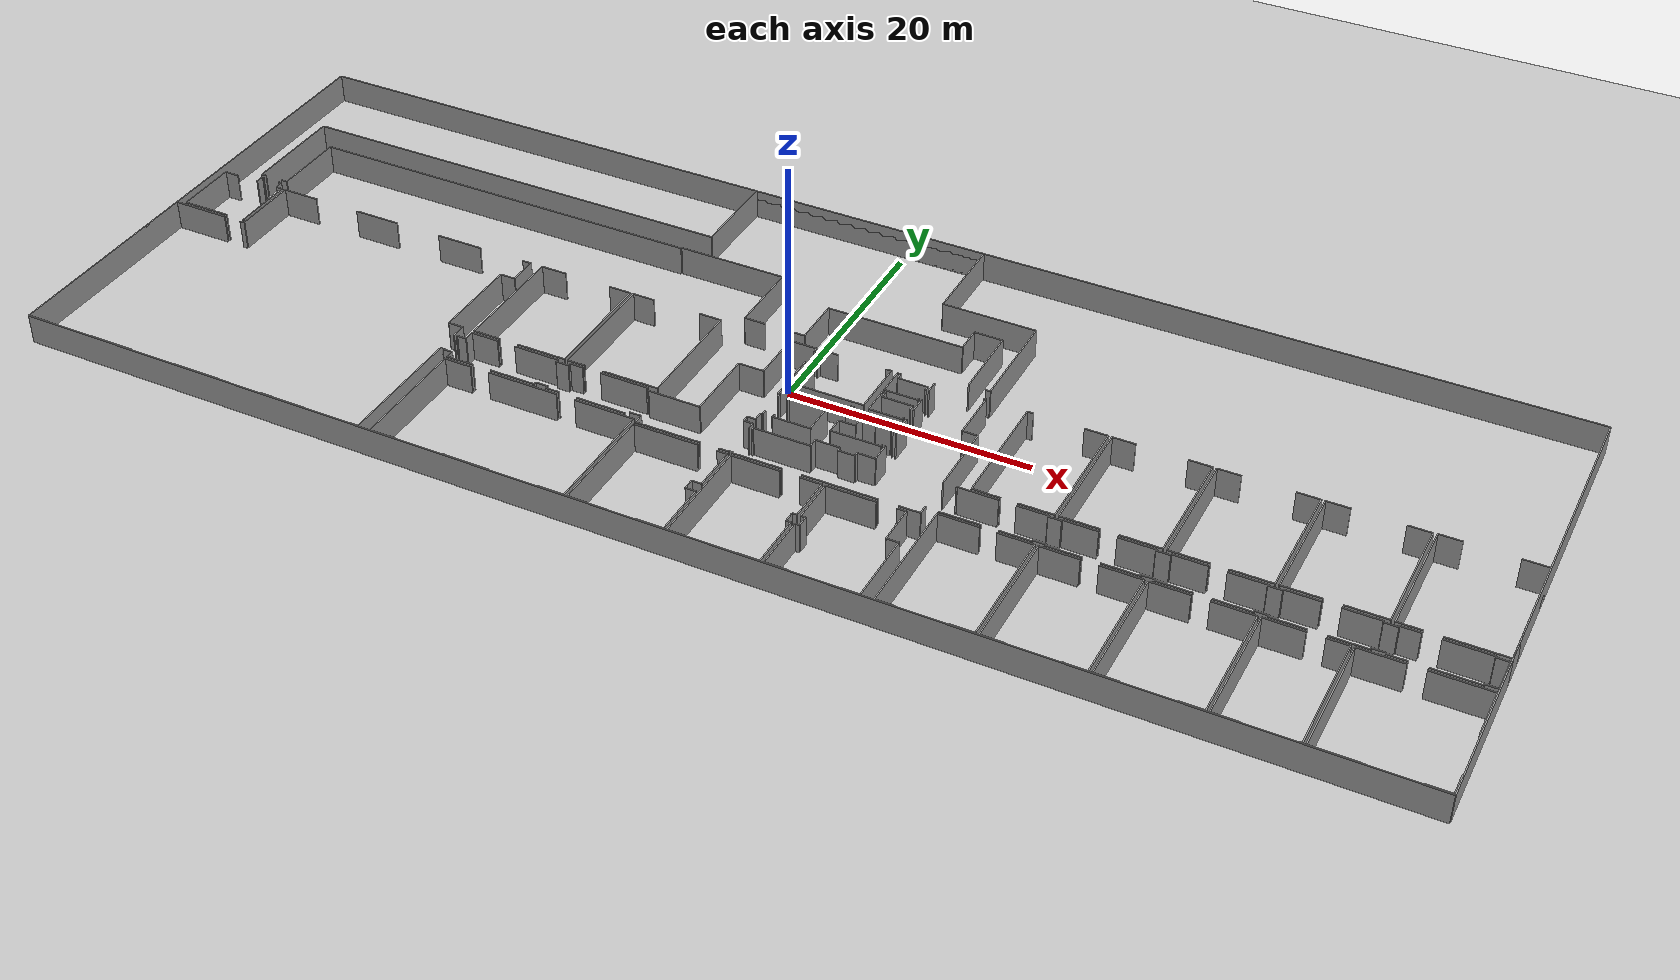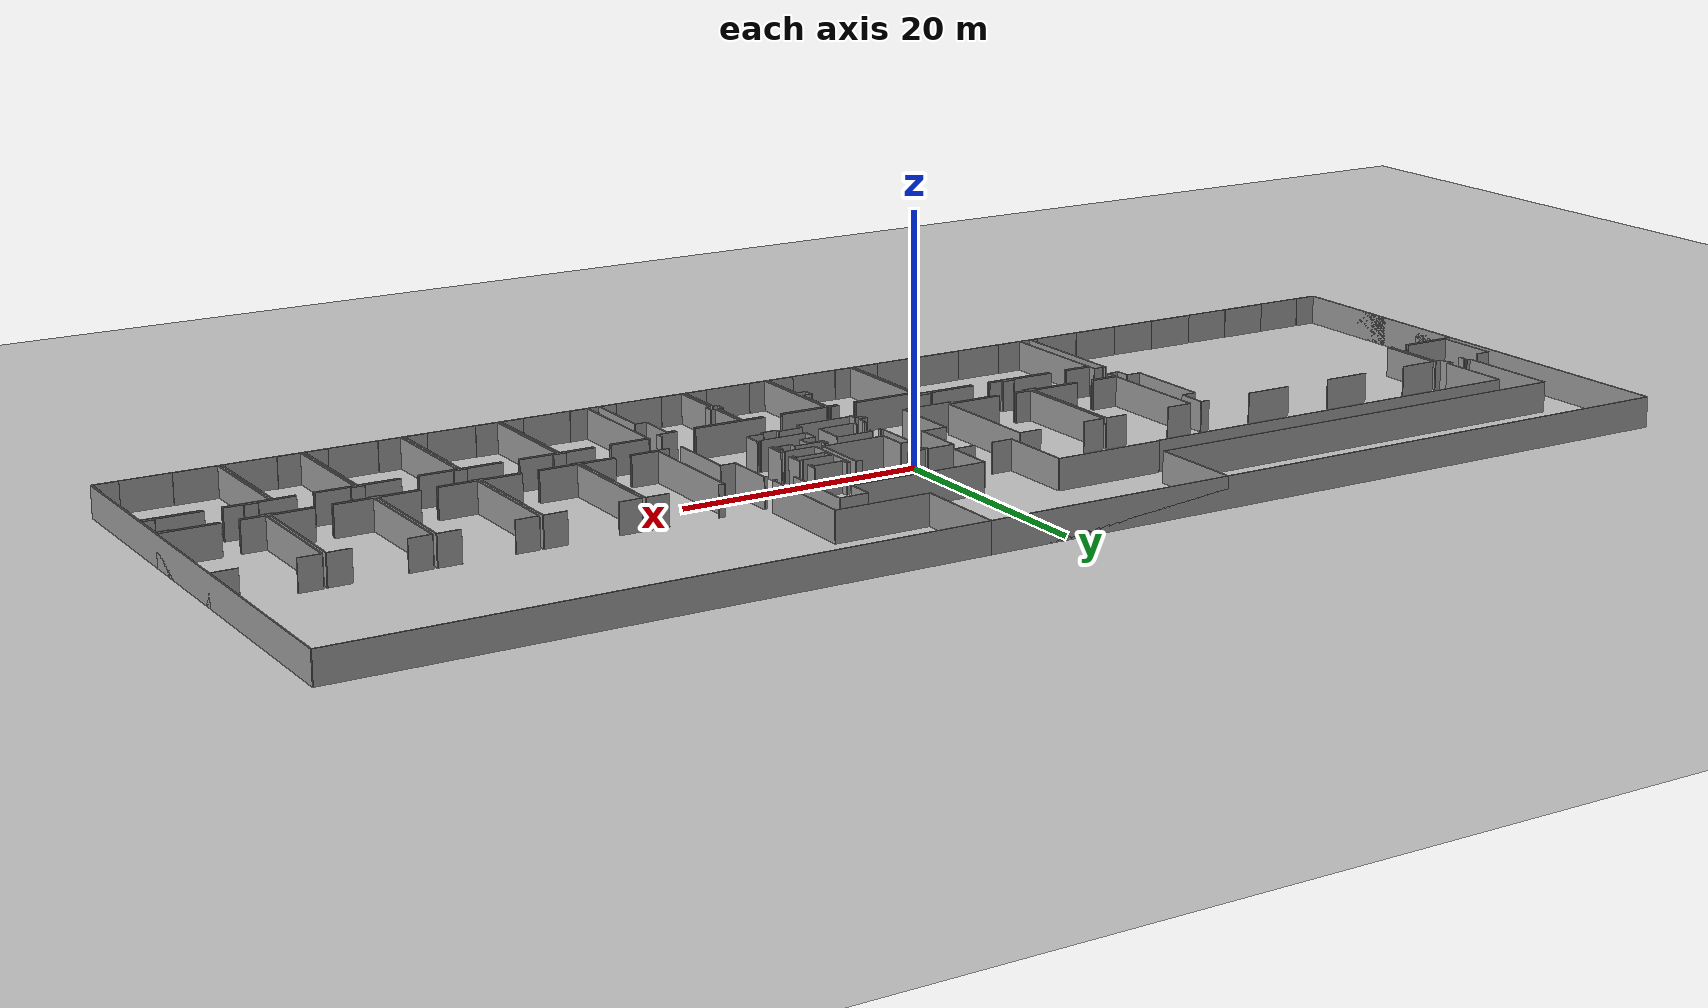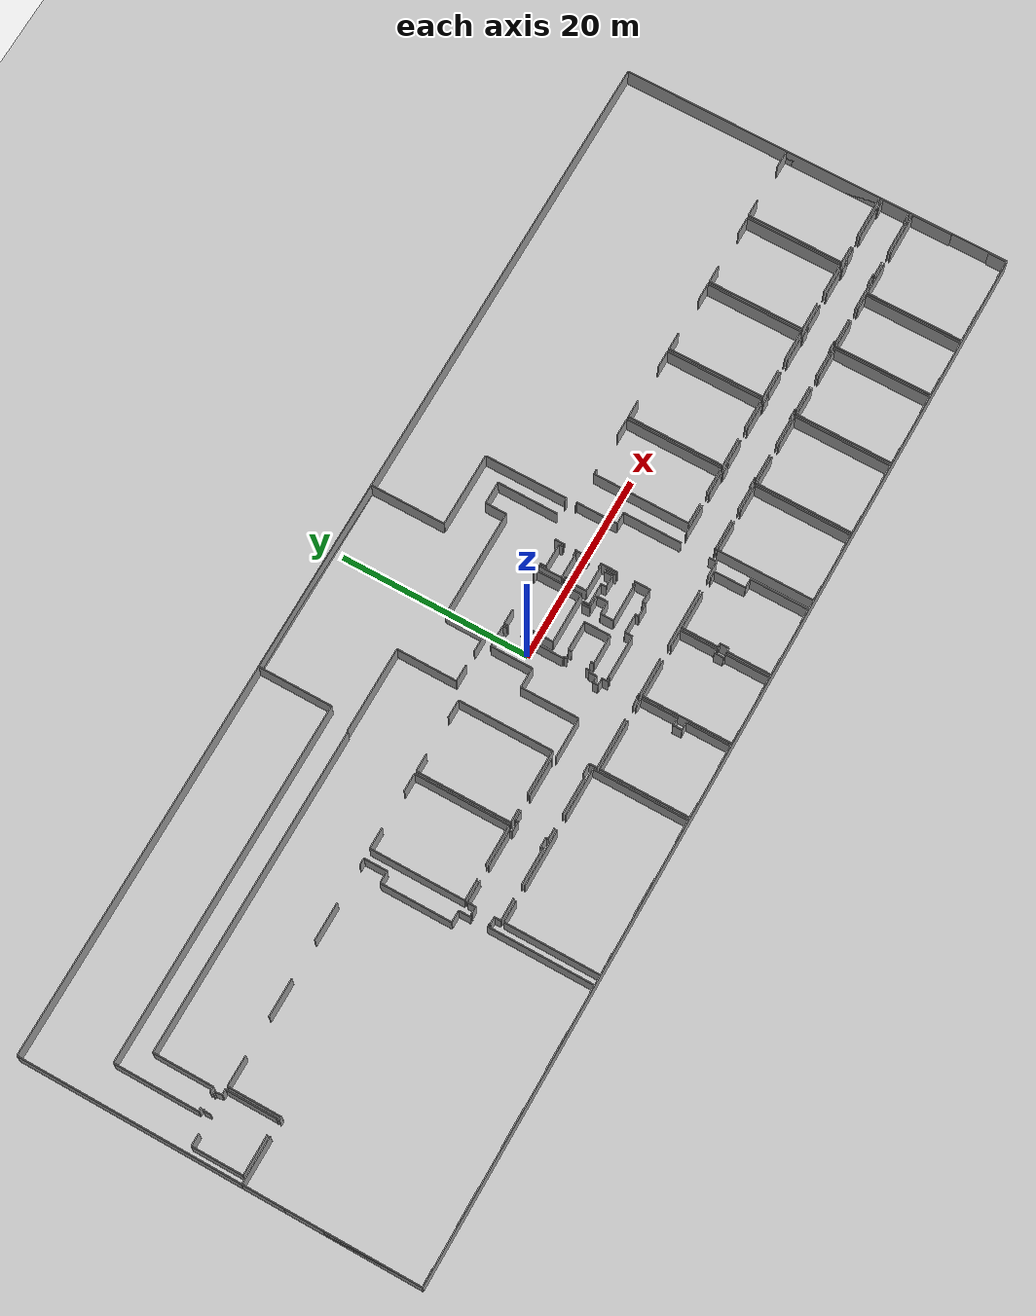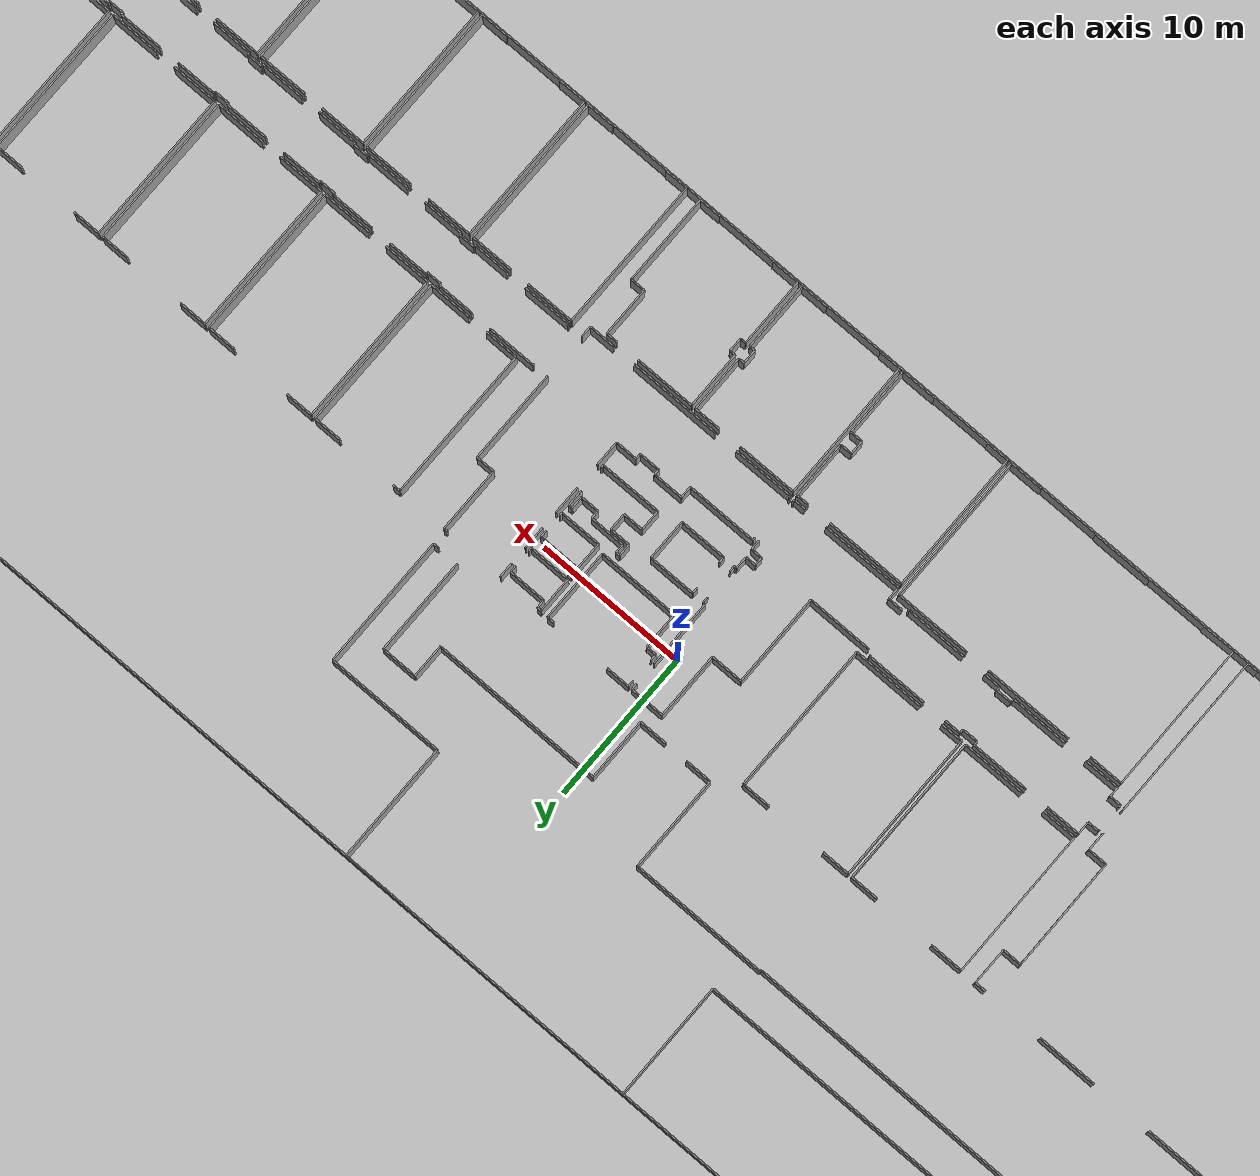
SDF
<sdf version="1.6">
  <world name="default">
    <light name="sun" type="directional">
      <cast_shadows>1</cast_shadows>
      <pose frame="">0 0 10 0 -0 0</pose>
      <diffuse>0.8 0.8 0.8 1</diffuse>
      <specular>0.1 0.1 0.1 1</specular>
      <attenuation>
        <range>1000</range>
        <constant>0.9</constant>
        <linear>0.01</linear>
        <quadratic>0.001</quadratic>
      </attenuation>
      <direction>-0.5 0.5 -1</direction>
    </light>
    <model name="ground_plane">
      <static>1</static>
      <link name="link">
        <collision name="collision">
          <geometry>
            <plane>
              <normal>0 0 1</normal>
              <size>100 100</size>
            </plane>
          </geometry>
          <surface>
            <friction>
              <ode>
                <mu>100</mu>
                <mu2>50</mu2>
              </ode>
              <torsional>
                <ode />
              </torsional>
            </friction>
            <contact>
              <ode />
            </contact>
            <bounce />
          </surface>
          <max_contacts>10</max_contacts>
        </collision>
        <visual name="visual">
          <cast_shadows>0</cast_shadows>
          <geometry>
            <plane>
              <normal>0 0 1</normal>
              <size>100 100</size>
            </plane>
          </geometry>
          <material>
            <script>
              <uri>file://media/materials/scripts/gazebo.material</uri>
              <name>Gazebo/Grey</name>
            </script>
          </material>
        </visual>
        <self_collide>0</self_collide>
        <kinematic>0</kinematic>
        <gravity>1</gravity>
      </link>
    </model>
    <gravity>0 0 -9.8</gravity>
    <magnetic_field>6e-06 2.3e-05 -4.2e-05</magnetic_field>
    <atmosphere type="adiabatic" />
    <physics default="0" name="default_physics" type="ode">
      <max_step_size>0.001</max_step_size>
      <real_time_factor>1</real_time_factor>
      <real_time_update_rate>1000</real_time_update_rate>
    </physics>
    <scene>
      <ambient>0.4 0.4 0.4 1</ambient>
      <background>0.7 0.7 0.7 1</background>
      <shadows>1</shadows>
    </scene>
    <spherical_coordinates>
      <surface_model>EARTH_WGS84</surface_model>
      <latitude_deg>0</latitude_deg>
      <longitude_deg>0</longitude_deg>
      <elevation>0</elevation>
      <heading_deg>0</heading_deg>
    </spherical_coordinates>
  <model name="50057025">
		<static>1</static>
		<link name="Wall_0">
			<collision name="Wall_0_Collision">
				<geometry>
					<box>
						<size>5.34124027728 0.1 2.5</size>
					</box>
				</geometry>
				<pose frame="">2.67062013864 0 1.25 0 0 0</pose>
			</collision>
			<visual name="Wall_0_Visual">
				<pose frame="">2.67062013864 0 1.25 0 0 0</pose>
				<geometry>
					<box>
						<size>5.34124027728 0.1 2.5</size>
					</box>
				</geometry>
				<material>
					<script>
						<uri>file://media/materials/scripts/gazebo.material</uri>
						<name>Gazebo/Grey</name>
					</script>
					<ambient>1 1 1 1</ambient>
				</material>
			</visual>
			<pose frame="">0.715880722011 -23.0882932223 0 0 0 1.57079632679</pose>
		</link>
		<link name="Wall_1">
			<collision name="Wall_1_Collision">
				<geometry>
					<box>
						<size>1.2621640826 0.1 2.5</size>
					</box>
				</geometry>
				<pose frame="">0.631082041299 0 1.25 0 0 0</pose>
			</collision>
			<visual name="Wall_1_Visual">
				<pose frame="">0.631082041299 0 1.25 0 0 0</pose>
				<geometry>
					<box>
						<size>1.2621640826 0.1 2.5</size>
					</box>
				</geometry>
				<material>
					<script>
						<uri>file://media/materials/scripts/gazebo.material</uri>
						<name>Gazebo/Grey</name>
					</script>
					<ambient>1 1 1 1</ambient>
				</material>
			</visual>
			<pose frame="">0.715880722011 -17.747052945 0 0 0 0.0</pose>
		</link>
		<link name="Wall_2">
			<collision name="Wall_2_Collision">
				<geometry>
					<box>
						<size>0.717400638618 0.1 2.5</size>
					</box>
				</geometry>
				<pose frame="">0.358700319309 0 1.25 0 0 0</pose>
			</collision>
			<visual name="Wall_2_Visual">
				<pose frame="">0.358700319309 0 1.25 0 0 0</pose>
				<geometry>
					<box>
						<size>0.717400638618 0.1 2.5</size>
					</box>
				</geometry>
				<material>
					<script>
						<uri>file://media/materials/scripts/gazebo.material</uri>
						<name>Gazebo/Grey</name>
					</script>
					<ambient>1 1 1 1</ambient>
				</material>
			</visual>
			<pose frame="">3.95976274102 -17.747052945 0 0 0 1.57079632679</pose>
		</link>
		<link name="Wall_3">
			<collision name="Wall_3_Collision">
				<geometry>
					<box>
						<size>0.124506502077 0.1 2.5</size>
					</box>
				</geometry>
				<pose frame="">0.0622532510383 0 1.25 0 0 0</pose>
			</collision>
			<visual name="Wall_3_Visual">
				<pose frame="">0.0622532510383 0 1.25 0 0 0</pose>
				<geometry>
					<box>
						<size>0.124506502077 0.1 2.5</size>
					</box>
				</geometry>
				<material>
					<script>
						<uri>file://media/materials/scripts/gazebo.material</uri>
						<name>Gazebo/Grey</name>
					</script>
					<ambient>1 1 1 1</ambient>
				</material>
			</visual>
			<pose frame="">3.95976274102 -17.0296523064 0 0 0 0.0</pose>
		</link>
		<link name="Wall_4">
			<collision name="Wall_4_Collision">
				<geometry>
					<box>
						<size>0.242046719703 0.1 2.5</size>
					</box>
				</geometry>
				<pose frame="">0.121023359852 0 1.25 0 0 0</pose>
			</collision>
			<visual name="Wall_4_Visual">
				<pose frame="">0.121023359852 0 1.25 0 0 0</pose>
				<geometry>
					<box>
						<size>0.242046719703 0.1 2.5</size>
					</box>
				</geometry>
				<material>
					<script>
						<uri>file://media/materials/scripts/gazebo.material</uri>
						<name>Gazebo/Grey</name>
					</script>
					<ambient>1 1 1 1</ambient>
				</material>
			</visual>
			<pose frame="">5.63331758531 -17.0296523064 0 0 0 0.0</pose>
		</link>
		<link name="Wall_5">
			<collision name="Wall_5_Collision">
				<geometry>
					<box>
						<size>0.727010503161 0.1 2.5</size>
					</box>
				</geometry>
				<pose frame="">0.36350525158 0 1.25 0 0 0</pose>
			</collision>
			<visual name="Wall_5_Visual">
				<pose frame="">0.36350525158 0 1.25 0 0 0</pose>
				<geometry>
					<box>
						<size>0.727010503161 0.1 2.5</size>
					</box>
				</geometry>
				<material>
					<script>
						<uri>file://media/materials/scripts/gazebo.material</uri>
						<name>Gazebo/Grey</name>
					</script>
					<ambient>1 1 1 1</ambient>
				</material>
			</visual>
			<pose frame="">5.87536430501 -17.0296523064 0 0 0 -1.42990944752</pose>
		</link>
		<link name="Wall_6">
			<collision name="Wall_6_Collision">
				<geometry>
					<box>
						<size>0.560469248921 0.1 2.5</size>
					</box>
				</geometry>
				<pose frame="">0.28023462446 0 1.25 0 0 0</pose>
			</collision>
			<visual name="Wall_6_Visual">
				<pose frame="">0.28023462446 0 1.25 0 0 0</pose>
				<geometry>
					<box>
						<size>0.560469248921 0.1 2.5</size>
					</box>
				</geometry>
				<material>
					<script>
						<uri>file://media/materials/scripts/gazebo.material</uri>
						<name>Gazebo/Grey</name>
					</script>
					<ambient>1 1 1 1</ambient>
				</material>
			</visual>
			<pose frame="">5.97745203713 -17.7494594797 0 0 0 0.0</pose>
		</link>
		<link name="Wall_7">
			<collision name="Wall_7_Collision">
				<geometry>
					<box>
						<size>5.34098695785 0.1 2.5</size>
					</box>
				</geometry>
				<pose frame="">2.67049347892 0 1.25 0 0 0</pose>
			</collision>
			<visual name="Wall_7_Visual">
				<pose frame="">2.67049347892 0 1.25 0 0 0</pose>
				<geometry>
					<box>
						<size>5.34098695785 0.1 2.5</size>
					</box>
				</geometry>
				<material>
					<script>
						<uri>file://media/materials/scripts/gazebo.material</uri>
						<name>Gazebo/Grey</name>
					</script>
					<ambient>1 1 1 1</ambient>
				</material>
			</visual>
			<pose frame="">6.53792128605 -17.7494594797 0 0 0 -1.57079632679</pose>
		</link>
		<link name="Wall_8">
			<collision name="Wall_8_Collision">
				<geometry>
					<box>
						<size>0.0718160596922 0.1 2.5</size>
					</box>
				</geometry>
				<pose frame="">0.0359080298461 0 1.25 0 0 0</pose>
			</collision>
			<visual name="Wall_8_Visual">
				<pose frame="">0.0359080298461 0 1.25 0 0 0</pose>
				<geometry>
					<box>
						<size>0.0718160596922 0.1 2.5</size>
					</box>
				</geometry>
				<material>
					<script>
						<uri>file://media/materials/scripts/gazebo.material</uri>
						<name>Gazebo/Grey</name>
					</script>
					<ambient>1 1 1 1</ambient>
				</material>
			</visual>
			<pose frame="">6.53792128605 -23.0904464375 0 0 0 3.14159265359</pose>
		</link>
		<link name="Wall_9">
			<collision name="Wall_9_Collision">
				<geometry>
					<box>
						<size>4.15950567247 0.1 2.5</size>
					</box>
				</geometry>
				<pose frame="">2.07975283624 0 1.25 0 0 0</pose>
			</collision>
			<visual name="Wall_9_Visual">
				<pose frame="">2.07975283624 0 1.25 0 0 0</pose>
				<geometry>
					<box>
						<size>4.15950567247 0.1 2.5</size>
					</box>
				</geometry>
				<material>
					<script>
						<uri>file://media/materials/scripts/gazebo.material</uri>
						<name>Gazebo/Grey</name>
					</script>
					<ambient>1 1 1 1</ambient>
				</material>
			</visual>
			<pose frame="">4.87538583716 -23.0904464375 0 0 0 3.14107499225</pose>
		</link>
		<link name="Wall_10">
			<collision name="Wall_10_Collision">
				<geometry>
					<box>
						<size>9.96697981171 0.1 2.5</size>
					</box>
				</geometry>
				<pose frame="">4.98348990585 0 1.25 0 0 0</pose>
			</collision>
			<visual name="Wall_10_Visual">
				<pose frame="">4.98348990585 0 1.25 0 0 0</pose>
				<geometry>
					<box>
						<size>9.96697981171 0.1 2.5</size>
					</box>
				</geometry>
				<material>
					<script>
						<uri>file://media/materials/scripts/gazebo.material</uri>
						<name>Gazebo/Grey</name>
					</script>
					<ambient>1 1 1 1</ambient>
				</material>
			</visual>
			<pose frame="">0.0 -41.7237374243 0 0 0 1.57079632679</pose>
		</link>
		<link name="Wall_11">
			<collision name="Wall_11_Collision">
				<geometry>
					<box>
						<size>4.31339667164 0.1 2.5</size>
					</box>
				</geometry>
				<pose frame="">2.15669833582 0 1.25 0 0 0</pose>
			</collision>
			<visual name="Wall_11_Visual">
				<pose frame="">2.15669833582 0 1.25 0 0 0</pose>
				<geometry>
					<box>
						<size>4.31339667164 0.1 2.5</size>
					</box>
				</geometry>
				<material>
					<script>
						<uri>file://media/materials/scripts/gazebo.material</uri>
						<name>Gazebo/Grey</name>
					</script>
					<ambient>1 1 1 1</ambient>
				</material>
			</visual>
			<pose frame="">0.0 -27.6909806882 0 0 0 1.57079632679</pose>
		</link>
		<link name="Wall_12">
			<collision name="Wall_12_Collision">
				<geometry>
					<box>
						<size>4.8690528513 0.1 2.5</size>
					</box>
				</geometry>
				<pose frame="">2.43452642565 0 1.25 0 0 0</pose>
			</collision>
			<visual name="Wall_12_Visual">
				<pose frame="">2.43452642565 0 1.25 0 0 0</pose>
				<geometry>
					<box>
						<size>4.8690528513 0.1 2.5</size>
					</box>
				</geometry>
				<material>
					<script>
						<uri>file://media/materials/scripts/gazebo.material</uri>
						<name>Gazebo/Grey</name>
					</script>
					<ambient>1 1 1 1</ambient>
				</material>
			</visual>
			<pose frame="">0.0 -23.3775840166 0 0 0 0.0</pose>
		</link>
		<link name="Wall_13">
			<collision name="Wall_13_Collision">
				<geometry>
					<box>
						<size>0.409364206217 0.1 2.5</size>
					</box>
				</geometry>
				<pose frame="">0.204682103109 0 1.25 0 0 0</pose>
			</collision>
			<visual name="Wall_13_Visual">
				<pose frame="">0.204682103109 0 1.25 0 0 0</pose>
				<geometry>
					<box>
						<size>0.409364206217 0.1 2.5</size>
					</box>
				</geometry>
				<material>
					<script>
						<uri>file://media/materials/scripts/gazebo.material</uri>
						<name>Gazebo/Grey</name>
					</script>
					<ambient>1 1 1 1</ambient>
				</material>
			</visual>
			<pose frame="">6.44343313697 -23.3775840166 0 0 0 0.0</pose>
		</link>
		<link name="Wall_14">
			<collision name="Wall_14_Collision">
				<geometry>
					<box>
						<size>5.620018315 0.1 2.5</size>
					</box>
				</geometry>
				<pose frame="">2.8100091575 0 1.25 0 0 0</pose>
			</collision>
			<visual name="Wall_14_Visual">
				<pose frame="">2.8100091575 0 1.25 0 0 0</pose>
				<geometry>
					<box>
						<size>5.620018315 0.1 2.5</size>
					</box>
				</geometry>
				<material>
					<script>
						<uri>file://media/materials/scripts/gazebo.material</uri>
						<name>Gazebo/Grey</name>
					</script>
					<ambient>1 1 1 1</ambient>
				</material>
			</visual>
			<pose frame="">6.85279734319 -23.3775840166 0 0 0 1.57079632679</pose>
		</link>
		<link name="Wall_15">
			<collision name="Wall_15_Collision">
				<geometry>
					<box>
						<size>3.17890558405 0.1 2.5</size>
					</box>
				</geometry>
				<pose frame="">1.58945279202 0 1.25 0 0 0</pose>
			</collision>
			<visual name="Wall_15_Visual">
				<pose frame="">1.58945279202 0 1.25 0 0 0</pose>
				<geometry>
					<box>
						<size>3.17890558405 0.1 2.5</size>
					</box>
				</geometry>
				<material>
					<script>
						<uri>file://media/materials/scripts/gazebo.material</uri>
						<name>Gazebo/Grey</name>
					</script>
					<ambient>1 1 1 1</ambient>
				</material>
			</visual>
			<pose frame="">6.85279734319 -17.7575657016 0 0 0 0.0</pose>
		</link>
		<link name="Wall_16">
			<collision name="Wall_16_Collision">
				<geometry>
					<box>
						<size>3.99370754525 0.1 2.5</size>
					</box>
				</geometry>
				<pose frame="">1.99685377262 0 1.25 0 0 0</pose>
			</collision>
			<visual name="Wall_16_Visual">
				<pose frame="">1.99685377262 0 1.25 0 0 0</pose>
				<geometry>
					<box>
						<size>3.99370754525 0.1 2.5</size>
					</box>
				</geometry>
				<material>
					<script>
						<uri>file://media/materials/scripts/gazebo.material</uri>
						<name>Gazebo/Grey</name>
					</script>
					<ambient>1 1 1 1</ambient>
				</material>
			</visual>
			<pose frame="">14.0734145053 -17.7575657016 0 0 0 0.0</pose>
		</link>
		<link name="Wall_17">
			<collision name="Wall_17_Collision">
				<geometry>
					<box>
						<size>4.01283316255 0.1 2.5</size>
					</box>
				</geometry>
				<pose frame="">2.00641658128 0 1.25 0 0 0</pose>
			</collision>
			<visual name="Wall_17_Visual">
				<pose frame="">2.00641658128 0 1.25 0 0 0</pose>
				<geometry>
					<box>
						<size>4.01283316255 0.1 2.5</size>
					</box>
				</geometry>
				<material>
					<script>
						<uri>file://media/materials/scripts/gazebo.material</uri>
						<name>Gazebo/Grey</name>
					</script>
					<ambient>1 1 1 1</ambient>
				</material>
			</visual>
			<pose frame="">22.1183331075 -17.7575657016 0 0 0 0.0</pose>
		</link>
		<link name="Wall_18">
			<collision name="Wall_18_Collision">
				<geometry>
					<box>
						<size>0.756665150972 0.1 2.5</size>
					</box>
				</geometry>
				<pose frame="">0.378332575486 0 1.25 0 0 0</pose>
			</collision>
			<visual name="Wall_18_Visual">
				<pose frame="">0.378332575486 0 1.25 0 0 0</pose>
				<geometry>
					<box>
						<size>0.756665150972 0.1 2.5</size>
					</box>
				</geometry>
				<material>
					<script>
						<uri>file://media/materials/scripts/gazebo.material</uri>
						<name>Gazebo/Grey</name>
					</script>
					<ambient>1 1 1 1</ambient>
				</material>
			</visual>
			<pose frame="">30.1536255711 -17.7575657016 0 0 0 0.0</pose>
		</link>
		<link name="Wall_19">
			<collision name="Wall_19_Collision">
				<geometry>
					<box>
						<size>2.44503918218 0.1 2.5</size>
					</box>
				</geometry>
				<pose frame="">1.22251959109 0 1.25 0 0 0</pose>
			</collision>
			<visual name="Wall_19_Visual">
				<pose frame="">1.22251959109 0 1.25 0 0 0</pose>
				<geometry>
					<box>
						<size>2.44503918218 0.1 2.5</size>
					</box>
				</geometry>
				<material>
					<script>
						<uri>file://media/materials/scripts/gazebo.material</uri>
						<name>Gazebo/Grey</name>
					</script>
					<ambient>1 1 1 1</ambient>
				</material>
			</visual>
			<pose frame="">30.910290722 -17.7575657016 0 0 0 -1.57079632679</pose>
		</link>
		<link name="Wall_20">
			<collision name="Wall_20_Collision">
				<geometry>
					<box>
						<size>1.27191688083 0.1 2.5</size>
					</box>
				</geometry>
				<pose frame="">0.635958440414 0 1.25 0 0 0</pose>
			</collision>
			<visual name="Wall_20_Visual">
				<pose frame="">0.635958440414 0 1.25 0 0 0</pose>
				<geometry>
					<box>
						<size>1.27191688083 0.1 2.5</size>
					</box>
				</geometry>
				<material>
					<script>
						<uri>file://media/materials/scripts/gazebo.material</uri>
						<name>Gazebo/Grey</name>
					</script>
					<ambient>1 1 1 1</ambient>
				</material>
			</visual>
			<pose frame="">30.910290722 -20.2026048837 0 0 0 3.14159265359</pose>
		</link>
		<link name="Wall_21">
			<collision name="Wall_21_Collision">
				<geometry>
					<box>
						<size>7.4895157419 0.1 2.5</size>
					</box>
				</geometry>
				<pose frame="">3.74475787095 0 1.25 0 0 0</pose>
			</collision>
			<visual name="Wall_21_Visual">
				<pose frame="">3.74475787095 0 1.25 0 0 0</pose>
				<geometry>
					<box>
						<size>7.4895157419 0.1 2.5</size>
					</box>
				</geometry>
				<material>
					<script>
						<uri>file://media/materials/scripts/gazebo.material</uri>
						<name>Gazebo/Grey</name>
					</script>
					<ambient>1 1 1 1</ambient>
				</material>
			</visual>
			<pose frame="">29.6383738412 -20.2026048837 0 0 0 -1.57079632679</pose>
		</link>
		<link name="Wall_22">
			<collision name="Wall_22_Collision">
				<geometry>
					<box>
						<size>1.2665971727 0.1 2.5</size>
					</box>
				</geometry>
				<pose frame="">0.633298586351 0 1.25 0 0 0</pose>
			</collision>
			<visual name="Wall_22_Visual">
				<pose frame="">0.633298586351 0 1.25 0 0 0</pose>
				<geometry>
					<box>
						<size>1.2665971727 0.1 2.5</size>
					</box>
				</geometry>
				<material>
					<script>
						<uri>file://media/materials/scripts/gazebo.material</uri>
						<name>Gazebo/Grey</name>
					</script>
					<ambient>1 1 1 1</ambient>
				</material>
			</visual>
			<pose frame="">29.6383738412 -27.6921206256 0 0 0 0.0</pose>
		</link>
		<link name="Wall_23">
			<collision name="Wall_23_Collision">
				<geometry>
					<box>
						<size>1.24797819426 0.1 2.5</size>
					</box>
				</geometry>
				<pose frame="">0.623989097132 0 1.25 0 0 0</pose>
			</collision>
			<visual name="Wall_23_Visual">
				<pose frame="">0.623989097132 0 1.25 0 0 0</pose>
				<geometry>
					<box>
						<size>1.24797819426 0.1 2.5</size>
					</box>
				</geometry>
				<material>
					<script>
						<uri>file://media/materials/scripts/gazebo.material</uri>
						<name>Gazebo/Grey</name>
					</script>
					<ambient>1 1 1 1</ambient>
				</material>
			</visual>
			<pose frame="">30.9049710139 -27.6921206256 0 0 0 -1.57079632679</pose>
		</link>
		<link name="Wall_24">
			<collision name="Wall_24_Collision">
				<geometry>
					<box>
						<size>11.0739857406 0.1 2.5</size>
					</box>
				</geometry>
				<pose frame="">5.53699287032 0 1.25 0 0 0</pose>
			</collision>
			<visual name="Wall_24_Visual">
				<pose frame="">5.53699287032 0 1.25 0 0 0</pose>
				<geometry>
					<box>
						<size>11.0739857406 0.1 2.5</size>
					</box>
				</geometry>
				<material>
					<script>
						<uri>file://media/materials/scripts/gazebo.material</uri>
						<name>Gazebo/Grey</name>
					</script>
					<ambient>1 1 1 1</ambient>
				</material>
			</visual>
			<pose frame="">30.9049710139 -30.6380989896 0 0 0 -1.57079632679</pose>
		</link>
		<link name="Wall_25">
			<collision name="Wall_25_Collision">
				<geometry>
					<box>
						<size>0.745519095852 0.1 2.5</size>
					</box>
				</geometry>
				<pose frame="">0.372759547926 0 1.25 0 0 0</pose>
			</collision>
			<visual name="Wall_25_Visual">
				<pose frame="">0.372759547926 0 1.25 0 0 0</pose>
				<geometry>
					<box>
						<size>0.745519095852 0.1 2.5</size>
					</box>
				</geometry>
				<material>
					<script>
						<uri>file://media/materials/scripts/gazebo.material</uri>
						<name>Gazebo/Grey</name>
					</script>
					<ambient>1 1 1 1</ambient>
				</material>
			</visual>
			<pose frame="">30.9049710139 -41.7120847303 0 0 0 3.14159265359</pose>
		</link>
		<link name="Wall_26">
			<collision name="Wall_26_Collision">
				<geometry>
					<box>
						<size>4.03677184912 0.1 2.5</size>
					</box>
				</geometry>
				<pose frame="">2.01838592456 0 1.25 0 0 0</pose>
			</collision>
			<visual name="Wall_26_Visual">
				<pose frame="">2.01838592456 0 1.25 0 0 0</pose>
				<geometry>
					<box>
						<size>4.03677184912 0.1 2.5</size>
					</box>
				</geometry>
				<material>
					<script>
						<uri>file://media/materials/scripts/gazebo.material</uri>
						<name>Gazebo/Grey</name>
					</script>
					<ambient>1 1 1 1</ambient>
				</material>
			</visual>
			<pose frame="">26.1453521583 -41.7120847303 0 0 0 3.14159265359</pose>
		</link>
		<link name="Wall_27">
			<collision name="Wall_27_Collision">
				<geometry>
					<box>
						<size>4.043991453 0.1 2.5</size>
					</box>
				</geometry>
				<pose frame="">2.0219957265 0 1.25 0 0 0</pose>
			</collision>
			<visual name="Wall_27_Visual">
				<pose frame="">2.0219957265 0 1.25 0 0 0</pose>
				<geometry>
					<box>
						<size>4.043991453 0.1 2.5</size>
					</box>
				</geometry>
				<material>
					<script>
						<uri>file://media/materials/scripts/gazebo.material</uri>
						<name>Gazebo/Grey</name>
					</script>
					<ambient>1 1 1 1</ambient>
				</material>
			</visual>
			<pose frame="">18.0944805495 -41.7120847303 0 0 0 3.14159265359</pose>
		</link>
		<link name="Wall_28">
			<collision name="Wall_28_Collision">
				<geometry>
					<box>
						<size>4.04918450141 0.1 2.5</size>
					</box>
				</geometry>
				<pose frame="">2.02459225071 0 1.25 0 0 0</pose>
			</collision>
			<visual name="Wall_28_Visual">
				<pose frame="">2.02459225071 0 1.25 0 0 0</pose>
				<geometry>
					<box>
						<size>4.04918450141 0.1 2.5</size>
					</box>
				</geometry>
				<material>
					<script>
						<uri>file://media/materials/scripts/gazebo.material</uri>
						<name>Gazebo/Grey</name>
					</script>
					<ambient>1 1 1 1</ambient>
				</material>
			</visual>
			<pose frame="">10.0391758506 -41.7120847303 0 0 0 3.14159265359</pose>
		</link>
		<link name="Wall_29">
			<collision name="Wall_29_Collision">
				<geometry>
					<box>
						<size>1.94096848651 0.1 2.5</size>
					</box>
				</geometry>
				<pose frame="">0.970484243253 0 1.25 0 0 0</pose>
			</collision>
			<visual name="Wall_29_Visual">
				<pose frame="">0.970484243253 0 1.25 0 0 0</pose>
				<geometry>
					<box>
						<size>1.94096848651 0.1 2.5</size>
					</box>
				</geometry>
				<material>
					<script>
						<uri>file://media/materials/scripts/gazebo.material</uri>
						<name>Gazebo/Grey</name>
					</script>
					<ambient>1 1 1 1</ambient>
				</material>
			</visual>
			<pose frame="">1.94093350745 -41.7120847303 0 0 0 -3.13558907132</pose>
		</link>
		<link name="Wall_30">
			<collision name="Wall_30_Collision">
				<geometry>
					<box>
						<size>9.95798697178 0.1 2.5</size>
					</box>
				</geometry>
				<pose frame="">4.97899348589 0 1.25 0 0 0</pose>
			</collision>
			<visual name="Wall_30_Visual">
				<pose frame="">4.97899348589 0 1.25 0 0 0</pose>
				<geometry>
					<box>
						<size>9.95798697178 0.1 2.5</size>
					</box>
				</geometry>
				<material>
					<script>
						<uri>file://media/materials/scripts/gazebo.material</uri>
						<name>Gazebo/Grey</name>
					</script>
					<ambient>1 1 1 1</ambient>
				</material>
			</visual>
			<pose frame="">31.9786654372 -27.7137794373 0 0 0 1.57079632679</pose>
		</link>
		<link name="Wall_31">
			<collision name="Wall_31_Collision">
				<geometry>
					<box>
						<size>2.20894546919 0.1 2.5</size>
					</box>
				</geometry>
				<pose frame="">1.1044727346 0 1.25 0 0 0</pose>
			</collision>
			<visual name="Wall_31_Visual">
				<pose frame="">1.1044727346 0 1.25 0 0 0</pose>
				<geometry>
					<box>
						<size>2.20894546919 0.1 2.5</size>
					</box>
				</geometry>
				<material>
					<script>
						<uri>file://media/materials/scripts/gazebo.material</uri>
						<name>Gazebo/Grey</name>
					</script>
					<ambient>1 1 1 1</ambient>
				</material>
			</visual>
			<pose frame="">31.9786654372 -17.7557924655 0 0 0 0.0</pose>
		</link>
		<link name="Wall_32">
			<collision name="Wall_32_Collision">
				<geometry>
					<box>
						<size>1.89444939121 0.1 2.5</size>
					</box>
				</geometry>
				<pose frame="">0.947224695605 0 1.25 0 0 0</pose>
			</collision>
			<visual name="Wall_32_Visual">
				<pose frame="">0.947224695605 0 1.25 0 0 0</pose>
				<geometry>
					<box>
						<size>1.89444939121 0.1 2.5</size>
					</box>
				</geometry>
				<material>
					<script>
						<uri>file://media/materials/scripts/gazebo.material</uri>
						<name>Gazebo/Grey</name>
					</script>
					<ambient>1 1 1 1</ambient>
				</material>
			</visual>
			<pose frame="">38.207157034 -17.7557924655 0 0 0 0.0</pose>
		</link>
		<link name="Wall_33">
			<collision name="Wall_33_Collision">
				<geometry>
					<box>
						<size>9.94734755553 0.1 2.5</size>
					</box>
				</geometry>
				<pose frame="">4.97367377777 0 1.25 0 0 0</pose>
			</collision>
			<visual name="Wall_33_Visual">
				<pose frame="">4.97367377777 0 1.25 0 0 0</pose>
				<geometry>
					<box>
						<size>9.94734755553 0.1 2.5</size>
					</box>
				</geometry>
				<material>
					<script>
						<uri>file://media/materials/scripts/gazebo.material</uri>
						<name>Gazebo/Grey</name>
					</script>
					<ambient>1 1 1 1</ambient>
				</material>
			</visual>
			<pose frame="">40.1016064252 -17.7557924655 0 0 0 -1.57079632679</pose>
		</link>
		<link name="Wall_34">
			<collision name="Wall_34_Collision">
				<geometry>
					<box>
						<size>4.21865520312 0.1 2.5</size>
					</box>
				</geometry>
				<pose frame="">2.10932760156 0 1.25 0 0 0</pose>
			</collision>
			<visual name="Wall_34_Visual">
				<pose frame="">2.10932760156 0 1.25 0 0 0</pose>
				<geometry>
					<box>
						<size>4.21865520312 0.1 2.5</size>
					</box>
				</geometry>
				<material>
					<script>
						<uri>file://media/materials/scripts/gazebo.material</uri>
						<name>Gazebo/Grey</name>
					</script>
					<ambient>1 1 1 1</ambient>
				</material>
			</visual>
			<pose frame="">40.1016064252 -27.7031400211 0 0 0 3.14159265359</pose>
		</link>
		<link name="Wall_35">
			<collision name="Wall_35_Collision">
				<geometry>
					<box>
						<size>2.30485143158 0.1 2.5</size>
					</box>
				</geometry>
				<pose frame="">1.15242571579 0 1.25 0 0 0</pose>
			</collision>
			<visual name="Wall_35_Visual">
				<pose frame="">1.15242571579 0 1.25 0 0 0</pose>
				<geometry>
					<box>
						<size>2.30485143158 0.1 2.5</size>
					</box>
				</geometry>
				<material>
					<script>
						<uri>file://media/materials/scripts/gazebo.material</uri>
						<name>Gazebo/Grey</name>
					</script>
					<ambient>1 1 1 1</ambient>
				</material>
			</visual>
			<pose frame="">34.2834923124 -27.7031400211 0 0 0 -3.13697654086</pose>
		</link>
		<link name="Wall_36">
			<collision name="Wall_36_Collision">
				<geometry>
					<box>
						<size>9.96039350641 0.1 2.5</size>
					</box>
				</geometry>
				<pose frame="">4.9801967532 0 1.25 0 0 0</pose>
			</collision>
			<visual name="Wall_36_Visual">
				<pose frame="">4.9801967532 0 1.25 0 0 0</pose>
				<geometry>
					<box>
						<size>9.96039350641 0.1 2.5</size>
					</box>
				</geometry>
				<material>
					<script>
						<uri>file://media/materials/scripts/gazebo.material</uri>
						<name>Gazebo/Grey</name>
					</script>
					<ambient>1 1 1 1</ambient>
				</material>
			</visual>
			<pose frame="">40.3863374696 -27.7208723815 0 0 0 1.57079632679</pose>
		</link>
		<link name="Wall_37">
			<collision name="Wall_37_Collision">
				<geometry>
					<box>
						<size>1.85721143433 0.1 2.5</size>
					</box>
				</geometry>
				<pose frame="">0.928605717166 0 1.25 0 0 0</pose>
			</collision>
			<visual name="Wall_37_Visual">
				<pose frame="">0.928605717166 0 1.25 0 0 0</pose>
				<geometry>
					<box>
						<size>1.85721143433 0.1 2.5</size>
					</box>
				</geometry>
				<material>
					<script>
						<uri>file://media/materials/scripts/gazebo.material</uri>
						<name>Gazebo/Grey</name>
					</script>
					<ambient>1 1 1 1</ambient>
				</material>
			</visual>
			<pose frame="">40.3863374696 -17.7604788751 0 0 0 0.0</pose>
		</link>
		<link name="Wall_38">
			<collision name="Wall_38_Collision">
				<geometry>
					<box>
						<size>1.92383444562 0.1 2.5</size>
					</box>
				</geometry>
				<pose frame="">0.961917222808 0 1.25 0 0 0</pose>
			</collision>
			<visual name="Wall_38_Visual">
				<pose frame="">0.961917222808 0 1.25 0 0 0</pose>
				<geometry>
					<box>
						<size>1.92383444562 0.1 2.5</size>
					</box>
				</geometry>
				<material>
					<script>
						<uri>file://media/materials/scripts/gazebo.material</uri>
						<name>Gazebo/Grey</name>
					</script>
					<ambient>1 1 1 1</ambient>
				</material>
			</visual>
			<pose frame="">46.2909601693 -17.7604788751 0 0 0 0.0</pose>
		</link>
		<link name="Wall_39">
			<collision name="Wall_39_Collision">
				<geometry>
					<box>
						<size>9.94367442373 0.1 2.5</size>
					</box>
				</geometry>
				<pose frame="">4.97183721186 0 1.25 0 0 0</pose>
			</collision>
			<visual name="Wall_39_Visual">
				<pose frame="">4.97183721186 0 1.25 0 0 0</pose>
				<geometry>
					<box>
						<size>9.94367442373 0.1 2.5</size>
					</box>
				</geometry>
				<material>
					<script>
						<uri>file://media/materials/scripts/gazebo.material</uri>
						<name>Gazebo/Grey</name>
					</script>
					<ambient>1 1 1 1</ambient>
				</material>
			</visual>
			<pose frame="">48.2147946149 -17.7604788751 0 0 0 -1.57079632679</pose>
		</link>
		<link name="Wall_40">
			<collision name="Wall_40_Collision">
				<geometry>
					<box>
						<size>4.73872000223 0.1 2.5</size>
					</box>
				</geometry>
				<pose frame="">2.36936000111 0 1.25 0 0 0</pose>
			</collision>
			<visual name="Wall_40_Visual">
				<pose frame="">2.36936000111 0 1.25 0 0 0</pose>
				<geometry>
					<box>
						<size>4.73872000223 0.1 2.5</size>
					</box>
				</geometry>
				<material>
					<script>
						<uri>file://media/materials/scripts/gazebo.material</uri>
						<name>Gazebo/Grey</name>
					</script>
					<ambient>1 1 1 1</ambient>
				</material>
			</visual>
			<pose frame="">48.2147946149 -27.7041532988 0 0 0 3.14159265359</pose>
		</link>
		<link name="Wall_41">
			<collision name="Wall_41_Collision">
				<geometry>
					<box>
						<size>1.47314738923 0.1 2.5</size>
					</box>
				</geometry>
				<pose frame="">0.736573694616 0 1.25 0 0 0</pose>
			</collision>
			<visual name="Wall_41_Visual">
				<pose frame="">0.736573694616 0 1.25 0 0 0</pose>
				<geometry>
					<box>
						<size>1.47314738923 0.1 2.5</size>
					</box>
				</geometry>
				<material>
					<script>
						<uri>file://media/materials/scripts/gazebo.material</uri>
						<name>Gazebo/Grey</name>
					</script>
					<ambient>1 1 1 1</ambient>
				</material>
			</visual>
			<pose frame="">41.8593899815 -27.7041532988 0 0 0 -3.13024318392</pose>
		</link>
		<link name="Wall_42">
			<collision name="Wall_42_Collision">
				<geometry>
					<box>
						<size>0.674589654181 0.1 2.5</size>
					</box>
				</geometry>
				<pose frame="">0.33729482709 0 1.25 0 0 0</pose>
			</collision>
			<visual name="Wall_42_Visual">
				<pose frame="">0.33729482709 0 1.25 0 0 0</pose>
				<geometry>
					<box>
						<size>0.674589654181 0.1 2.5</size>
					</box>
				</geometry>
				<material>
					<script>
						<uri>file://media/materials/scripts/gazebo.material</uri>
						<name>Gazebo/Grey</name>
					</script>
					<ambient>1 1 1 1</ambient>
				</material>
			</visual>
			<pose frame="">31.9582732227 -31.4768396374 0 0 0 1.57079632679</pose>
		</link>
		<link name="Wall_43">
			<collision name="Wall_43_Collision">
				<geometry>
					<box>
						<size>0.78275705273 0.1 2.5</size>
					</box>
				</geometry>
				<pose frame="">0.391378526365 0 1.25 0 0 0</pose>
			</collision>
			<visual name="Wall_43_Visual">
				<pose frame="">0.391378526365 0 1.25 0 0 0</pose>
				<geometry>
					<box>
						<size>0.78275705273 0.1 2.5</size>
					</box>
				</geometry>
				<material>
					<script>
						<uri>file://media/materials/scripts/gazebo.material</uri>
						<name>Gazebo/Grey</name>
					</script>
					<ambient>1 1 1 1</ambient>
				</material>
			</visual>
			<pose frame="">31.9582732227 -30.8022499832 0 0 0 3.14159265359</pose>
		</link>
		<link name="Wall_44">
			<collision name="Wall_44_Collision">
				<geometry>
					<box>
						<size>0.141605563908 0.1 2.5</size>
					</box>
				</geometry>
				<pose frame="">0.070802781954 0 1.25 0 0 0</pose>
			</collision>
			<visual name="Wall_44_Visual">
				<pose frame="">0.070802781954 0 1.25 0 0 0</pose>
				<geometry>
					<box>
						<size>0.141605563908 0.1 2.5</size>
					</box>
				</geometry>
				<material>
					<script>
						<uri>file://media/materials/scripts/gazebo.material</uri>
						<name>Gazebo/Grey</name>
					</script>
					<ambient>1 1 1 1</ambient>
				</material>
			</visual>
			<pose frame="">31.17551617 -30.8022499832 0 0 0 1.57079632679</pose>
		</link>
		<link name="Wall_45">
			<collision name="Wall_45_Collision">
				<geometry>
					<box>
						<size>0.101327773816 0.1 2.5</size>
					</box>
				</geometry>
				<pose frame="">0.0506638869081 0 1.25 0 0 0</pose>
			</collision>
			<visual name="Wall_45_Visual">
				<pose frame="">0.0506638869081 0 1.25 0 0 0</pose>
				<geometry>
					<box>
						<size>0.101327773816 0.1 2.5</size>
					</box>
				</geometry>
				<material>
					<script>
						<uri>file://media/materials/scripts/gazebo.material</uri>
						<name>Gazebo/Grey</name>
					</script>
					<ambient>1 1 1 1</ambient>
				</material>
			</visual>
			<pose frame="">31.17551617 -28.9575778609 0 0 0 1.57079632679</pose>
		</link>
		<link name="Wall_46">
			<collision name="Wall_46_Collision">
				<geometry>
					<box>
						<size>0.779083920929 0.1 2.5</size>
					</box>
				</geometry>
				<pose frame="">0.389541960464 0 1.25 0 0 0</pose>
			</collision>
			<visual name="Wall_46_Visual">
				<pose frame="">0.389541960464 0 1.25 0 0 0</pose>
				<geometry>
					<box>
						<size>0.779083920929 0.1 2.5</size>
					</box>
				</geometry>
				<material>
					<script>
						<uri>file://media/materials/scripts/gazebo.material</uri>
						<name>Gazebo/Grey</name>
					</script>
					<ambient>1 1 1 1</ambient>
				</material>
			</visual>
			<pose frame="">31.17551617 -28.8562500871 0 0 0 0.0</pose>
		</link>
		<link name="Wall_47">
			<collision name="Wall_47_Collision">
				<geometry>
					<box>
						<size>0.861286077437 0.1 2.5</size>
					</box>
				</geometry>
				<pose frame="">0.430643038719 0 1.25 0 0 0</pose>
			</collision>
			<visual name="Wall_47_Visual">
				<pose frame="">0.430643038719 0 1.25 0 0 0</pose>
				<geometry>
					<box>
						<size>0.861286077437 0.1 2.5</size>
					</box>
				</geometry>
				<material>
					<script>
						<uri>file://media/materials/scripts/gazebo.material</uri>
						<name>Gazebo/Grey</name>
					</script>
					<ambient>1 1 1 1</ambient>
				</material>
			</visual>
			<pose frame="">31.9546000909 -28.8562500871 0 0 0 1.57079632679</pose>
		</link>
		<link name="Wall_48">
			<collision name="Wall_48_Collision">
				<geometry>
					<box>
						<size>2.3153396317 0.1 2.5</size>
					</box>
				</geometry>
				<pose frame="">1.15766981585 0 1.25 0 0 0</pose>
			</collision>
			<visual name="Wall_48_Visual">
				<pose frame="">1.15766981585 0 1.25 0 0 0</pose>
				<geometry>
					<box>
						<size>2.3153396317 0.1 2.5</size>
					</box>
				</geometry>
				<material>
					<script>
						<uri>file://media/materials/scripts/gazebo.material</uri>
						<name>Gazebo/Grey</name>
					</script>
					<ambient>1 1 1 1</ambient>
				</material>
			</visual>
			<pose frame="">31.9546000909 -27.9949640096 0 0 0 0.0</pose>
		</link>
		<link name="Wall_49">
			<collision name="Wall_49_Collision">
				<geometry>
					<box>
						<size>3.8642613142 0.1 2.5</size>
					</box>
				</geometry>
				<pose frame="">1.9321306571 0 1.25 0 0 0</pose>
			</collision>
			<visual name="Wall_49_Visual">
				<pose frame="">1.9321306571 0 1.25 0 0 0</pose>
				<geometry>
					<box>
						<size>3.8642613142 0.1 2.5</size>
					</box>
				</geometry>
				<material>
					<script>
						<uri>file://media/materials/scripts/gazebo.material</uri>
						<name>Gazebo/Grey</name>
					</script>
					<ambient>1 1 1 1</ambient>
				</material>
			</visual>
			<pose frame="">35.8308940783 -27.9949640096 0 0 0 0.0</pose>
		</link>
		<link name="Wall_50">
			<collision name="Wall_50_Collision">
				<geometry>
					<box>
						<size>0.26725200344 0.1 2.5</size>
					</box>
				</geometry>
				<pose frame="">0.13362600172 0 1.25 0 0 0</pose>
			</collision>
			<visual name="Wall_50_Visual">
				<pose frame="">0.13362600172 0 1.25 0 0 0</pose>
				<geometry>
					<box>
						<size>0.26725200344 0.1 2.5</size>
					</box>
				</geometry>
				<material>
					<script>
						<uri>file://media/materials/scripts/gazebo.material</uri>
						<name>Gazebo/Grey</name>
					</script>
					<ambient>1 1 1 1</ambient>
				</material>
			</visual>
			<pose frame="">39.6951553925 -27.9949640096 0 0 0 -1.57079632679</pose>
		</link>
		<link name="Wall_51">
			<collision name="Wall_51_Collision">
				<geometry>
					<box>
						<size>1.06596818055 0.1 2.5</size>
					</box>
				</geometry>
				<pose frame="">0.532984090273 0 1.25 0 0 0</pose>
			</collision>
			<visual name="Wall_51_Visual">
				<pose frame="">0.532984090273 0 1.25 0 0 0</pose>
				<geometry>
					<box>
						<size>1.06596818055 0.1 2.5</size>
					</box>
				</geometry>
				<material>
					<script>
						<uri>file://media/materials/scripts/gazebo.material</uri>
						<name>Gazebo/Grey</name>
					</script>
					<ambient>1 1 1 1</ambient>
				</material>
			</visual>
			<pose frame="">39.6951553925 -28.2622160131 0 0 0 0.0</pose>
		</link>
		<link name="Wall_52">
			<collision name="Wall_52_Collision">
				<geometry>
					<box>
						<size>0.274851586476 0.1 2.5</size>
					</box>
				</geometry>
				<pose frame="">0.137425793238 0 1.25 0 0 0</pose>
			</collision>
			<visual name="Wall_52_Visual">
				<pose frame="">0.137425793238 0 1.25 0 0 0</pose>
				<geometry>
					<box>
						<size>0.274851586476 0.1 2.5</size>
					</box>
				</geometry>
				<material>
					<script>
						<uri>file://media/materials/scripts/gazebo.material</uri>
						<name>Gazebo/Grey</name>
					</script>
					<ambient>1 1 1 1</ambient>
				</material>
			</visual>
			<pose frame="">40.761123573 -28.2622160131 0 0 0 1.57079632679</pose>
		</link>
		<link name="Wall_53">
			<collision name="Wall_53_Collision">
				<geometry>
					<box>
						<size>1.09927968619 0.1 2.5</size>
					</box>
				</geometry>
				<pose frame="">0.549639843094 0 1.25 0 0 0</pose>
			</collision>
			<visual name="Wall_53_Visual">
				<pose frame="">0.549639843094 0 1.25 0 0 0</pose>
				<geometry>
					<box>
						<size>1.09927968619 0.1 2.5</size>
					</box>
				</geometry>
				<material>
					<script>
						<uri>file://media/materials/scripts/gazebo.material</uri>
						<name>Gazebo/Grey</name>
					</script>
					<ambient>1 1 1 1</ambient>
				</material>
			</visual>
			<pose frame="">40.761123573 -27.9873644266 0 0 0 0.0</pose>
		</link>
		<link name="Wall_54">
			<collision name="Wall_54_Collision">
				<geometry>
					<box>
						<size>4.06793013957 0.1 2.5</size>
					</box>
				</geometry>
				<pose frame="">2.03396506978 0 1.25 0 0 0</pose>
			</collision>
			<visual name="Wall_54_Visual">
				<pose frame="">2.03396506978 0 1.25 0 0 0</pose>
				<geometry>
					<box>
						<size>4.06793013957 0.1 2.5</size>
					</box>
				</geometry>
				<material>
					<script>
						<uri>file://media/materials/scripts/gazebo.material</uri>
						<name>Gazebo/Grey</name>
					</script>
					<ambient>1 1 1 1</ambient>
				</material>
			</visual>
			<pose frame="">43.433390288 -27.9873644266 0 0 0 0.0</pose>
		</link>
		<link name="Wall_55">
			<collision name="Wall_55_Collision">
				<geometry>
					<box>
						<size>0.08954842011 0.1 2.5</size>
					</box>
				</geometry>
				<pose frame="">0.044774210055 0 1.25 0 0 0</pose>
			</collision>
			<visual name="Wall_55_Visual">
				<pose frame="">0.044774210055 0 1.25 0 0 0</pose>
				<geometry>
					<box>
						<size>0.08954842011 0.1 2.5</size>
					</box>
				</geometry>
				<material>
					<script>
						<uri>file://media/materials/scripts/gazebo.material</uri>
						<name>Gazebo/Grey</name>
					</script>
					<ambient>1 1 1 1</ambient>
				</material>
			</visual>
			<pose frame="">47.5013204276 -27.9873644266 0 0 0 -1.57079632679</pose>
		</link>
		<link name="Wall_56">
			<collision name="Wall_56_Collision">
				<geometry>
					<box>
						<size>0.0818221773565 0.1 2.5</size>
					</box>
				</geometry>
				<pose frame="">0.0409110886783 0 1.25 0 0 0</pose>
			</collision>
			<visual name="Wall_56_Visual">
				<pose frame="">0.0409110886783 0 1.25 0 0 0</pose>
				<geometry>
					<box>
						<size>0.0818221773565 0.1 2.5</size>
					</box>
				</geometry>
				<material>
					<script>
						<uri>file://media/materials/scripts/gazebo.material</uri>
						<name>Gazebo/Grey</name>
					</script>
					<ambient>1 1 1 1</ambient>
				</material>
			</visual>
			<pose frame="">47.5013204276 -31.3829847869 0 0 0 -1.57079632679</pose>
		</link>
		<link name="Wall_57">
			<collision name="Wall_57_Collision">
				<geometry>
					<box>
						<size>4.05539082756 0.1 2.5</size>
					</box>
				</geometry>
				<pose frame="">2.02769541378 0 1.25 0 0 0</pose>
			</collision>
			<visual name="Wall_57_Visual">
				<pose frame="">2.02769541378 0 1.25 0 0 0</pose>
				<geometry>
					<box>
						<size>4.05539082756 0.1 2.5</size>
					</box>
				</geometry>
				<material>
					<script>
						<uri>file://media/materials/scripts/gazebo.material</uri>
						<name>Gazebo/Grey</name>
					</script>
					<ambient>1 1 1 1</ambient>
				</material>
			</visual>
			<pose frame="">47.5013204276 -31.4648069643 0 0 0 3.14159265359</pose>
		</link>
		<link name="Wall_58">
			<collision name="Wall_58_Collision">
				<geometry>
					<box>
						<size>1.13005799748 0.1 2.5</size>
					</box>
				</geometry>
				<pose frame="">0.565028998742 0 1.25 0 0 0</pose>
			</collision>
			<visual name="Wall_58_Visual">
				<pose frame="">0.565028998742 0 1.25 0 0 0</pose>
				<geometry>
					<box>
						<size>1.13005799748 0.1 2.5</size>
					</box>
				</geometry>
				<material>
					<script>
						<uri>file://media/materials/scripts/gazebo.material</uri>
						<name>Gazebo/Grey</name>
					</script>
					<ambient>1 1 1 1</ambient>
				</material>
			</visual>
			<pose frame="">41.8762357239 -31.4648069643 0 0 0 3.14159265359</pose>
		</link>
		<link name="Wall_59">
			<collision name="Wall_59_Collision">
				<geometry>
					<box>
						<size>0.241540080834 0.1 2.5</size>
					</box>
				</geometry>
				<pose frame="">0.120770040417 0 1.25 0 0 0</pose>
			</collision>
			<visual name="Wall_59_Visual">
				<pose frame="">0.120770040417 0 1.25 0 0 0</pose>
				<geometry>
					<box>
						<size>0.241540080834 0.1 2.5</size>
					</box>
				</geometry>
				<material>
					<script>
						<uri>file://media/materials/scripts/gazebo.material</uri>
						<name>Gazebo/Grey</name>
					</script>
					<ambient>1 1 1 1</ambient>
				</material>
			</visual>
			<pose frame="">40.7461777264 -31.4648069643 0 0 0 1.57079632679</pose>
		</link>
		<link name="Wall_60">
			<collision name="Wall_60_Collision">
				<geometry>
					<box>
						<size>1.04392938974 0.1 2.5</size>
					</box>
				</geometry>
				<pose frame="">0.52196469487 0 1.25 0 0 0</pose>
			</collision>
			<visual name="Wall_60_Visual">
				<pose frame="">0.52196469487 0 1.25 0 0 0</pose>
				<geometry>
					<box>
						<size>1.04392938974 0.1 2.5</size>
					</box>
				</geometry>
				<material>
					<script>
						<uri>file://media/materials/scripts/gazebo.material</uri>
						<name>Gazebo/Grey</name>
					</script>
					<ambient>1 1 1 1</ambient>
				</material>
			</visual>
			<pose frame="">40.7461777264 -31.2232668834 0 0 0 3.14159265359</pose>
		</link>
		<link name="Wall_61">
			<collision name="Wall_61_Collision">
				<geometry>
					<box>
						<size>0.239386865641 0.1 2.5</size>
					</box>
				</geometry>
				<pose frame="">0.11969343282 0 1.25 0 0 0</pose>
			</collision>
			<visual name="Wall_61_Visual">
				<pose frame="">0.11969343282 0 1.25 0 0 0</pose>
				<geometry>
					<box>
						<size>0.239386865641 0.1 2.5</size>
					</box>
				</geometry>
				<material>
					<script>
						<uri>file://media/materials/scripts/gazebo.material</uri>
						<name>Gazebo/Grey</name>
					</script>
					<ambient>1 1 1 1</ambient>
				</material>
			</visual>
			<pose frame="">39.7022483366 -31.2232668834 0 0 0 -1.57079632679</pose>
		</link>
		<link name="Wall_62">
			<collision name="Wall_62_Collision">
				<geometry>
					<box>
						<size>3.85007542586 0.1 2.5</size>
					</box>
				</geometry>
				<pose frame="">1.92503771293 0 1.25 0 0 0</pose>
			</collision>
			<visual name="Wall_62_Visual">
				<pose frame="">1.92503771293 0 1.25 0 0 0</pose>
				<geometry>
					<box>
						<size>3.85007542586 0.1 2.5</size>
					</box>
				</geometry>
				<material>
					<script>
						<uri>file://media/materials/scripts/gazebo.material</uri>
						<name>Gazebo/Grey</name>
					</script>
					<ambient>1 1 1 1</ambient>
				</material>
			</visual>
			<pose frame="">39.7022483366 -31.4626537491 0 0 0 3.14159265359</pose>
		</link>
		<link name="Wall_63">
			<collision name="Wall_63_Collision">
				<geometry>
					<box>
						<size>2.34236110841 0.1 2.5</size>
					</box>
				</geometry>
				<pose frame="">1.1711805542 0 1.25 0 0 0</pose>
			</collision>
			<visual name="Wall_63_Visual">
				<pose frame="">1.1711805542 0 1.25 0 0 0</pose>
				<geometry>
					<box>
						<size>2.34236110841 0.1 2.5</size>
					</box>
				</geometry>
				<material>
					<script>
						<uri>file://media/materials/scripts/gazebo.material</uri>
						<name>Gazebo/Grey</name>
					</script>
					<ambient>1 1 1 1</ambient>
				</material>
			</visual>
			<pose frame="">34.3005913742 -31.4626537491 0 0 0 -3.13553638199</pose>
		</link>
		<link name="Wall_64">
			<collision name="Wall_64_Collision">
				<geometry>
					<box>
						<size>9.98838530393 0.1 2.5</size>
					</box>
				</geometry>
				<pose frame="">4.99419265196 0 1.25 0 0 0</pose>
			</collision>
			<visual name="Wall_64_Visual">
				<pose frame="">4.99419265196 0 1.25 0 0 0</pose>
				<geometry>
					<box>
						<size>9.98838530393 0.1 2.5</size>
					</box>
				</geometry>
				<material>
					<script>
						<uri>file://media/materials/scripts/gazebo.material</uri>
						<name>Gazebo/Grey</name>
					</script>
					<ambient>1 1 1 1</ambient>
				</material>
			</visual>
			<pose frame="">31.9703058959 -41.7575555688 0 0 0 1.57079632679</pose>
		</link>
		<link name="Wall_65">
			<collision name="Wall_65_Collision">
				<geometry>
					<box>
						<size>2.28240810521 0.1 2.5</size>
					</box>
				</geometry>
				<pose frame="">1.1412040526 0 1.25 0 0 0</pose>
			</collision>
			<visual name="Wall_65_Visual">
				<pose frame="">1.1412040526 0 1.25 0 0 0</pose>
				<geometry>
					<box>
						<size>2.28240810521 0.1 2.5</size>
					</box>
				</geometry>
				<material>
					<script>
						<uri>file://media/materials/scripts/gazebo.material</uri>
						<name>Gazebo/Grey</name>
					</script>
					<ambient>1 1 1 1</ambient>
				</material>
			</visual>
			<pose frame="">31.9703058959 -31.7691702649 0 0 0 0.0</pose>
		</link>
		<link name="Wall_66">
			<collision name="Wall_66_Collision">
				<geometry>
					<box>
						<size>5.98581157847 0.1 2.5</size>
					</box>
				</geometry>
				<pose frame="">2.99290578924 0 1.25 0 0 0</pose>
			</collision>
			<visual name="Wall_66_Visual">
				<pose frame="">2.99290578924 0 1.25 0 0 0</pose>
				<geometry>
					<box>
						<size>5.98581157847 0.1 2.5</size>
					</box>
				</geometry>
				<material>
					<script>
						<uri>file://media/materials/scripts/gazebo.material</uri>
						<name>Gazebo/Grey</name>
					</script>
					<ambient>1 1 1 1</ambient>
				</material>
			</visual>
			<pose frame="">35.8521729108 -31.7691702649 0 0 0 0.0</pose>
		</link>
		<link name="Wall_67">
			<collision name="Wall_67_Collision">
				<geometry>
					<box>
						<size>5.07892800282 0.1 2.5</size>
					</box>
				</geometry>
				<pose frame="">2.53946400141 0 1.25 0 0 0</pose>
			</collision>
			<visual name="Wall_67_Visual">
				<pose frame="">2.53946400141 0 1.25 0 0 0</pose>
				<geometry>
					<box>
						<size>5.07892800282 0.1 2.5</size>
					</box>
				</geometry>
				<material>
					<script>
						<uri>file://media/materials/scripts/gazebo.material</uri>
						<name>Gazebo/Grey</name>
					</script>
					<ambient>1 1 1 1</ambient>
				</material>
			</visual>
			<pose frame="">43.4427631071 -31.7691702649 0 0 0 0.0</pose>
		</link>
		<link name="Wall_68">
			<collision name="Wall_68_Collision">
				<geometry>
					<box>
						<size>9.93252836861 0.1 2.5</size>
					</box>
				</geometry>
				<pose frame="">4.96626418431 0 1.25 0 0 0</pose>
			</collision>
			<visual name="Wall_68_Visual">
				<pose frame="">4.96626418431 0 1.25 0 0 0</pose>
				<geometry>
					<box>
						<size>9.93252836861 0.1 2.5</size>
					</box>
				</geometry>
				<material>
					<script>
						<uri>file://media/materials/scripts/gazebo.material</uri>
						<name>Gazebo/Grey</name>
					</script>
					<ambient>1 1 1 1</ambient>
				</material>
			</visual>
			<pose frame="">48.5216911099 -31.7691702649 0 0 0 -1.57079632679</pose>
		</link>
		<link name="Wall_69">
			<collision name="Wall_69_Collision">
				<geometry>
					<box>
						<size>2.24137035681 0.1 2.5</size>
					</box>
				</geometry>
				<pose frame="">1.12068517841 0 1.25 0 0 0</pose>
			</collision>
			<visual name="Wall_69_Visual">
				<pose frame="">1.12068517841 0 1.25 0 0 0</pose>
				<geometry>
					<box>
						<size>2.24137035681 0.1 2.5</size>
					</box>
				</geometry>
				<material>
					<script>
						<uri>file://media/materials/scripts/gazebo.material</uri>
						<name>Gazebo/Grey</name>
					</script>
					<ambient>1 1 1 1</ambient>
				</material>
			</visual>
			<pose frame="">48.5216911099 -41.7016986335 0 0 0 3.14159265359</pose>
		</link>
		<link name="Wall_70">
			<collision name="Wall_70_Collision">
				<geometry>
					<box>
						<size>4.04209155724 0.1 2.5</size>
					</box>
				</geometry>
				<pose frame="">2.02104577862 0 1.25 0 0 0</pose>
			</collision>
			<visual name="Wall_70_Visual">
				<pose frame="">2.02104577862 0 1.25 0 0 0</pose>
				<geometry>
					<box>
						<size>4.04209155724 0.1 2.5</size>
					</box>
				</geometry>
				<material>
					<script>
						<uri>file://media/materials/scripts/gazebo.material</uri>
						<name>Gazebo/Grey</name>
					</script>
					<ambient>1 1 1 1</ambient>
				</material>
			</visual>
			<pose frame="">42.2602679866 -41.7016986335 0 0 0 3.14159265359</pose>
		</link>
		<link name="Wall_71">
			<collision name="Wall_71_Collision">
				<geometry>
					<box>
						<size>2.20648609543 0.1 2.5</size>
					</box>
				</geometry>
				<pose frame="">1.10324304772 0 1.25 0 0 0</pose>
			</collision>
			<visual name="Wall_71_Visual">
				<pose frame="">1.10324304772 0 1.25 0 0 0</pose>
				<geometry>
					<box>
						<size>2.20648609543 0.1 2.5</size>
					</box>
				</geometry>
				<material>
					<script>
						<uri>file://media/materials/scripts/gazebo.material</uri>
						<name>Gazebo/Grey</name>
					</script>
					<ambient>1 1 1 1</ambient>
				</material>
			</visual>
			<pose frame="">34.1760848721 -41.7016986335 0 0 0 -3.11627506692</pose>
		</link>
		<link name="Wall_72">
			<collision name="Wall_72_Collision">
				<geometry>
					<box>
						<size>9.38041866103 0.1 2.5</size>
					</box>
				</geometry>
				<pose frame="">4.69020933051 0 1.25 0 0 0</pose>
			</collision>
			<visual name="Wall_72_Visual">
				<pose frame="">4.69020933051 0 1.25 0 0 0</pose>
				<geometry>
					<box>
						<size>9.38041866103 0.1 2.5</size>
					</box>
				</geometry>
				<material>
					<script>
						<uri>file://media/materials/scripts/gazebo.material</uri>
						<name>Gazebo/Grey</name>
					</script>
					<ambient>1 1 1 1</ambient>
				</material>
			</visual>
			<pose frame="">48.8117418624 -41.7020786126 0 0 0 1.57079632679</pose>
		</link>
		<link name="Wall_73">
			<collision name="Wall_73_Collision">
				<geometry>
					<box>
						<size>5.36023923487 0.1 2.5</size>
					</box>
				</geometry>
				<pose frame="">2.68011961744 0 1.25 0 0 0</pose>
			</collision>
			<visual name="Wall_73_Visual">
				<pose frame="">2.68011961744 0 1.25 0 0 0</pose>
				<geometry>
					<box>
						<size>5.36023923487 0.1 2.5</size>
					</box>
				</geometry>
				<material>
					<script>
						<uri>file://media/materials/scripts/gazebo.material</uri>
						<name>Gazebo/Grey</name>
					</script>
					<ambient>1 1 1 1</ambient>
				</material>
			</visual>
			<pose frame="">48.8117418624 -32.3216599516 0 0 0 0.0</pose>
		</link>
		<link name="Wall_74">
			<collision name="Wall_74_Collision">
				<geometry>
					<box>
						<size>0.851913258359 0.1 2.5</size>
					</box>
				</geometry>
				<pose frame="">0.42595662918 0 1.25 0 0 0</pose>
			</collision>
			<visual name="Wall_74_Visual">
				<pose frame="">0.42595662918 0 1.25 0 0 0</pose>
				<geometry>
					<box>
						<size>0.851913258359 0.1 2.5</size>
					</box>
				</geometry>
				<material>
					<script>
						<uri>file://media/materials/scripts/gazebo.material</uri>
						<name>Gazebo/Grey</name>
					</script>
					<ambient>1 1 1 1</ambient>
				</material>
			</visual>
			<pose frame="">55.7814461247 -32.3216599516 0 0 0 0.0</pose>
		</link>
		<link name="Wall_75">
			<collision name="Wall_75_Collision">
				<geometry>
					<box>
						<size>3.84348912056 0.1 2.5</size>
					</box>
				</geometry>
				<pose frame="">1.92174456028 0 1.25 0 0 0</pose>
			</collision>
			<visual name="Wall_75_Visual">
				<pose frame="">1.92174456028 0 1.25 0 0 0</pose>
				<geometry>
					<box>
						<size>3.84348912056 0.1 2.5</size>
					</box>
				</geometry>
				<material>
					<script>
						<uri>file://media/materials/scripts/gazebo.material</uri>
						<name>Gazebo/Grey</name>
					</script>
					<ambient>1 1 1 1</ambient>
				</material>
			</visual>
			<pose frame="">56.633359383 -32.3216599516 0 0 0 -1.57079632679</pose>
		</link>
		<link name="Wall_76">
			<collision name="Wall_76_Collision">
				<geometry>
					<box>
						<size>0.812522086288 0.1 2.5</size>
					</box>
				</geometry>
				<pose frame="">0.406261043144 0 1.25 0 0 0</pose>
			</collision>
			<visual name="Wall_76_Visual">
				<pose frame="">0.406261043144 0 1.25 0 0 0</pose>
				<geometry>
					<box>
						<size>0.812522086288 0.1 2.5</size>
					</box>
				</geometry>
				<material>
					<script>
						<uri>file://media/materials/scripts/gazebo.material</uri>
						<name>Gazebo/Grey</name>
					</script>
					<ambient>1 1 1 1</ambient>
				</material>
			</visual>
			<pose frame="">56.633359383 -36.1651490722 0 0 0 3.14159265359</pose>
		</link>
		<link name="Wall_77">
			<collision name="Wall_77_Collision">
				<geometry>
					<box>
						<size>0.928922366459 0.1 2.5</size>
					</box>
				</geometry>
				<pose frame="">0.46446118323 0 1.25 0 0 0</pose>
			</collision>
			<visual name="Wall_77_Visual">
				<pose frame="">0.46446118323 0 1.25 0 0 0</pose>
				<geometry>
					<box>
						<size>0.928922366459 0.1 2.5</size>
					</box>
				</geometry>
				<material>
					<script>
						<uri>file://media/materials/scripts/gazebo.material</uri>
						<name>Gazebo/Grey</name>
					</script>
					<ambient>1 1 1 1</ambient>
				</material>
			</visual>
			<pose frame="">55.8208372967 -36.1651490722 0 0 0 -1.57079632679</pose>
		</link>
		<link name="Wall_78">
			<collision name="Wall_78_Collision">
				<geometry>
					<box>
						<size>0.833167620203 0.1 2.5</size>
					</box>
				</geometry>
				<pose frame="">0.416583810102 0 1.25 0 0 0</pose>
			</collision>
			<visual name="Wall_78_Visual">
				<pose frame="">0.416583810102 0 1.25 0 0 0</pose>
				<geometry>
					<box>
						<size>0.833167620203 0.1 2.5</size>
					</box>
				</geometry>
				<material>
					<script>
						<uri>file://media/materials/scripts/gazebo.material</uri>
						<name>Gazebo/Grey</name>
					</script>
					<ambient>1 1 1 1</ambient>
				</material>
			</visual>
			<pose frame="">55.8208372967 -37.0940714386 0 0 0 0.0</pose>
		</link>
		<link name="Wall_79">
			<collision name="Wall_79_Collision">
				<geometry>
					<box>
						<size>4.61801329167 0.1 2.5</size>
					</box>
				</geometry>
				<pose frame="">2.30900664584 0 1.25 0 0 0</pose>
			</collision>
			<visual name="Wall_79_Visual">
				<pose frame="">2.30900664584 0 1.25 0 0 0</pose>
				<geometry>
					<box>
						<size>4.61801329167 0.1 2.5</size>
					</box>
				</geometry>
				<material>
					<script>
						<uri>file://media/materials/scripts/gazebo.material</uri>
						<name>Gazebo/Grey</name>
					</script>
					<ambient>1 1 1 1</ambient>
				</material>
			</visual>
			<pose frame="">56.6540049169 -37.0940714386 0 0 0 -1.57079632679</pose>
		</link>
		<link name="Wall_80">
			<collision name="Wall_80_Collision">
				<geometry>
					<box>
						<size>2.32648568682 0.1 2.5</size>
					</box>
				</geometry>
				<pose frame="">1.16324284341 0 1.25 0 0 0</pose>
			</collision>
			<visual name="Wall_80_Visual">
				<pose frame="">1.16324284341 0 1.25 0 0 0</pose>
				<geometry>
					<box>
						<size>2.32648568682 0.1 2.5</size>
					</box>
				</geometry>
				<material>
					<script>
						<uri>file://media/materials/scripts/gazebo.material</uri>
						<name>Gazebo/Grey</name>
					</script>
					<ambient>1 1 1 1</ambient>
				</material>
			</visual>
			<pose frame="">56.6540049169 -41.7120847303 0 0 0 3.14159265359</pose>
		</link>
		<link name="Wall_81">
			<collision name="Wall_81_Collision">
				<geometry>
					<box>
						<size>1.51007030123 0.1 2.5</size>
					</box>
				</geometry>
				<pose frame="">0.755035150613 0 1.25 0 0 0</pose>
			</collision>
			<visual name="Wall_81_Visual">
				<pose frame="">0.755035150613 0 1.25 0 0 0</pose>
				<geometry>
					<box>
						<size>1.51007030123 0.1 2.5</size>
					</box>
				</geometry>
				<material>
					<script>
						<uri>file://media/materials/scripts/gazebo.material</uri>
						<name>Gazebo/Grey</name>
					</script>
					<ambient>1 1 1 1</ambient>
				</material>
			</visual>
			<pose frame="">50.3217790117 -41.7120847303 0 0 0 3.13496634561</pose>
		</link>
		<link name="Wall_82">
			<collision name="Wall_82_Collision">
				<geometry>
					<box>
						<size>9.40030423664 0.1 2.5</size>
					</box>
				</geometry>
				<pose frame="">4.70015211832 0 1.25 0 0 0</pose>
			</collision>
			<visual name="Wall_82_Visual">
				<pose frame="">4.70015211832 0 1.25 0 0 0</pose>
				<geometry>
					<box>
						<size>9.40030423664 0.1 2.5</size>
					</box>
				</geometry>
				<material>
					<script>
						<uri>file://media/materials/scripts/gazebo.material</uri>
						<name>Gazebo/Grey</name>
					</script>
					<ambient>1 1 1 1</ambient>
				</material>
			</visual>
			<pose frame="">56.9192303649 -41.7248773617 0 0 0 1.57079632679</pose>
		</link>
		<link name="Wall_83">
			<collision name="Wall_83_Collision">
				<geometry>
					<box>
						<size>3.97749510144 0.1 2.5</size>
					</box>
				</geometry>
				<pose frame="">1.98874755072 0 1.25 0 0 0</pose>
			</collision>
			<visual name="Wall_83_Visual">
				<pose frame="">1.98874755072 0 1.25 0 0 0</pose>
				<geometry>
					<box>
						<size>3.97749510144 0.1 2.5</size>
					</box>
				</geometry>
				<material>
					<script>
						<uri>file://media/materials/scripts/gazebo.material</uri>
						<name>Gazebo/Grey</name>
					</script>
					<ambient>1 1 1 1</ambient>
				</material>
			</visual>
			<pose frame="">56.9192303649 -32.3245731251 0 0 0 0.0</pose>
		</link>
		<link name="Wall_84">
			<collision name="Wall_84_Collision">
				<geometry>
					<box>
						<size>1.79058842305 0.1 2.5</size>
					</box>
				</geometry>
				<pose frame="">0.895294211524 0 1.25 0 0 0</pose>
			</collision>
			<visual name="Wall_84_Visual">
				<pose frame="">0.895294211524 0 1.25 0 0 0</pose>
				<geometry>
					<box>
						<size>1.79058842305 0.1 2.5</size>
					</box>
				</geometry>
				<material>
					<script>
						<uri>file://media/materials/scripts/gazebo.material</uri>
						<name>Gazebo/Grey</name>
					</script>
					<ambient>1 1 1 1</ambient>
				</material>
			</visual>
			<pose frame="">62.4723723492 -32.3245731251 0 0 0 0.0</pose>
		</link>
		<link name="Wall_85">
			<collision name="Wall_85_Collision">
				<geometry>
					<box>
						<size>3.8203103923 0.1 2.5</size>
					</box>
				</geometry>
				<pose frame="">1.91015519615 0 1.25 0 0 0</pose>
			</collision>
			<visual name="Wall_85_Visual">
				<pose frame="">1.91015519615 0 1.25 0 0 0</pose>
				<geometry>
					<box>
						<size>3.8203103923 0.1 2.5</size>
					</box>
				</geometry>
				<material>
					<script>
						<uri>file://media/materials/scripts/gazebo.material</uri>
						<name>Gazebo/Grey</name>
					</script>
					<ambient>1 1 1 1</ambient>
				</material>
			</visual>
			<pose frame="">64.2629607722 -32.3245731251 0 0 0 -1.57079632679</pose>
		</link>
		<link name="Wall_86">
			<collision name="Wall_86_Collision">
				<geometry>
					<box>
						<size>0.395811616469 0.1 2.5</size>
					</box>
				</geometry>
				<pose frame="">0.197905808235 0 1.25 0 0 0</pose>
			</collision>
			<visual name="Wall_86_Visual">
				<pose frame="">0.197905808235 0 1.25 0 0 0</pose>
				<geometry>
					<box>
						<size>0.395811616469 0.1 2.5</size>
					</box>
				</geometry>
				<material>
					<script>
						<uri>file://media/materials/scripts/gazebo.material</uri>
						<name>Gazebo/Grey</name>
					</script>
					<ambient>1 1 1 1</ambient>
				</material>
			</visual>
			<pose frame="">64.2629607722 -36.1448835174 0 0 0 3.14159265359</pose>
		</link>
		<link name="Wall_87">
			<collision name="Wall_87_Collision">
				<geometry>
					<box>
						<size>0.941461678469 0.1 2.5</size>
					</box>
				</geometry>
				<pose frame="">0.470730839235 0 1.25 0 0 0</pose>
			</collision>
			<visual name="Wall_87_Visual">
				<pose frame="">0.470730839235 0 1.25 0 0 0</pose>
				<geometry>
					<box>
						<size>0.941461678469 0.1 2.5</size>
					</box>
				</geometry>
				<material>
					<script>
						<uri>file://media/materials/scripts/gazebo.material</uri>
						<name>Gazebo/Grey</name>
					</script>
					<ambient>1 1 1 1</ambient>
				</material>
			</visual>
			<pose frame="">63.8671491557 -36.1448835174 0 0 0 -1.57079632679</pose>
		</link>
		<link name="Wall_88">
			<collision name="Wall_88_Collision">
				<geometry>
					<box>
						<size>0.376685999162 0.1 2.5</size>
					</box>
				</geometry>
				<pose frame="">0.188342999581 0 1.25 0 0 0</pose>
			</collision>
			<visual name="Wall_88_Visual">
				<pose frame="">0.188342999581 0 1.25 0 0 0</pose>
				<geometry>
					<box>
						<size>0.376685999162 0.1 2.5</size>
					</box>
				</geometry>
				<material>
					<script>
						<uri>file://media/materials/scripts/gazebo.material</uri>
						<name>Gazebo/Grey</name>
					</script>
					<ambient>1 1 1 1</ambient>
				</material>
			</visual>
			<pose frame="">63.8671491557 -37.0863451959 0 0 0 0.0</pose>
		</link>
		<link name="Wall_89">
			<collision name="Wall_89_Collision">
				<geometry>
					<box>
						<size>4.62029316658 0.1 2.5</size>
					</box>
				</geometry>
				<pose frame="">2.31014658329 0 1.25 0 0 0</pose>
			</collision>
			<visual name="Wall_89_Visual">
				<pose frame="">2.31014658329 0 1.25 0 0 0</pose>
				<geometry>
					<box>
						<size>4.62029316658 0.1 2.5</size>
					</box>
				</geometry>
				<material>
					<script>
						<uri>file://media/materials/scripts/gazebo.material</uri>
						<name>Gazebo/Grey</name>
					</script>
					<ambient>1 1 1 1</ambient>
				</material>
			</visual>
			<pose frame="">64.2438351549 -37.0863451959 0 0 0 -1.57079632679</pose>
		</link>
		<link name="Wall_90">
			<collision name="Wall_90_Collision">
				<geometry>
					<box>
						<size>1.85391828168 0.1 2.5</size>
					</box>
				</geometry>
				<pose frame="">0.926959140842 0 1.25 0 0 0</pose>
			</collision>
			<visual name="Wall_90_Visual">
				<pose frame="">0.926959140842 0 1.25 0 0 0</pose>
				<geometry>
					<box>
						<size>1.85391828168 0.1 2.5</size>
					</box>
				</geometry>
				<material>
					<script>
						<uri>file://media/materials/scripts/gazebo.material</uri>
						<name>Gazebo/Grey</name>
					</script>
					<ambient>1 1 1 1</ambient>
				</material>
			</visual>
			<pose frame="">64.2438351549 -41.7066383624 0 0 0 3.14159265359</pose>
		</link>
		<link name="Wall_91">
			<collision name="Wall_91_Collision">
				<geometry>
					<box>
						<size>1.46189357891 0.1 2.5</size>
					</box>
				</geometry>
				<pose frame="">0.730946789455 0 1.25 0 0 0</pose>
			</collision>
			<visual name="Wall_91_Visual">
				<pose frame="">0.730946789455 0 1.25 0 0 0</pose>
				<geometry>
					<box>
						<size>1.46189357891 0.1 2.5</size>
					</box>
				</geometry>
				<material>
					<script>
						<uri>file://media/materials/scripts/gazebo.material</uri>
						<name>Gazebo/Grey</name>
					</script>
					<ambient>1 1 1 1</ambient>
				</material>
			</visual>
			<pose frame="">58.3810101619 -41.7066383624 0 0 0 -3.12911604602</pose>
		</link>
		<link name="Wall_92">
			<collision name="Wall_92_Collision">
				<geometry>
					<box>
						<size>4.62573953442 0.1 2.5</size>
					</box>
				</geometry>
				<pose frame="">2.31286976721 0 1.25 0 0 0</pose>
			</collision>
			<visual name="Wall_92_Visual">
				<pose frame="">2.31286976721 0 1.25 0 0 0</pose>
				<geometry>
					<box>
						<size>4.62573953442 0.1 2.5</size>
					</box>
				</geometry>
				<material>
					<script>
						<uri>file://media/materials/scripts/gazebo.material</uri>
						<name>Gazebo/Grey</name>
					</script>
					<ambient>1 1 1 1</ambient>
				</material>
			</visual>
			<pose frame="">64.5552913997 -41.7103114942 0 0 0 1.57079632679</pose>
		</link>
		<link name="Wall_93">
			<collision name="Wall_93_Collision">
				<geometry>
					<box>
						<size>0.37351950623 0.1 2.5</size>
					</box>
				</geometry>
				<pose frame="">0.186759753115 0 1.25 0 0 0</pose>
			</collision>
			<visual name="Wall_93_Visual">
				<pose frame="">0.186759753115 0 1.25 0 0 0</pose>
				<geometry>
					<box>
						<size>0.37351950623 0.1 2.5</size>
					</box>
				</geometry>
				<material>
					<script>
						<uri>file://media/materials/scripts/gazebo.material</uri>
						<name>Gazebo/Grey</name>
					</script>
					<ambient>1 1 1 1</ambient>
				</material>
			</visual>
			<pose frame="">64.5552913997 -37.0845719598 0 0 0 0.0</pose>
		</link>
		<link name="Wall_94">
			<collision name="Wall_94_Collision">
				<geometry>
					<box>
						<size>0.929049026177 0.1 2.5</size>
					</box>
				</geometry>
				<pose frame="">0.464524513088 0 1.25 0 0 0</pose>
			</collision>
			<visual name="Wall_94_Visual">
				<pose frame="">0.464524513088 0 1.25 0 0 0</pose>
				<geometry>
					<box>
						<size>0.929049026177 0.1 2.5</size>
					</box>
				</geometry>
				<material>
					<script>
						<uri>file://media/materials/scripts/gazebo.material</uri>
						<name>Gazebo/Grey</name>
					</script>
					<ambient>1 1 1 1</ambient>
				</material>
			</visual>
			<pose frame="">64.9288109059 -37.0845719598 0 0 0 1.57079632679</pose>
		</link>
		<link name="Wall_95">
			<collision name="Wall_95_Collision">
				<geometry>
					<box>
						<size>0.383145644742 0.1 2.5</size>
					</box>
				</geometry>
				<pose frame="">0.191572822371 0 1.25 0 0 0</pose>
			</collision>
			<visual name="Wall_95_Visual">
				<pose frame="">0.191572822371 0 1.25 0 0 0</pose>
				<geometry>
					<box>
						<size>0.383145644742 0.1 2.5</size>
					</box>
				</geometry>
				<material>
					<script>
						<uri>file://media/materials/scripts/gazebo.material</uri>
						<name>Gazebo/Grey</name>
					</script>
					<ambient>1 1 1 1</ambient>
				</material>
			</visual>
			<pose frame="">64.9288109059 -36.1555229336 0 0 0 3.14159265359</pose>
		</link>
		<link name="Wall_96">
			<collision name="Wall_96_Collision">
				<geometry>
					<box>
						<size>3.83094980855 0.1 2.5</size>
					</box>
				</geometry>
				<pose frame="">1.91547490428 0 1.25 0 0 0</pose>
			</collision>
			<visual name="Wall_96_Visual">
				<pose frame="">1.91547490428 0 1.25 0 0 0</pose>
				<geometry>
					<box>
						<size>3.83094980855 0.1 2.5</size>
					</box>
				</geometry>
				<material>
					<script>
						<uri>file://media/materials/scripts/gazebo.material</uri>
						<name>Gazebo/Grey</name>
					</script>
					<ambient>1 1 1 1</ambient>
				</material>
			</visual>
			<pose frame="">64.5456652612 -36.1555229336 0 0 0 1.57079632679</pose>
		</link>
		<link name="Wall_97">
			<collision name="Wall_97_Collision">
				<geometry>
					<box>
						<size>4.03208543958 0.1 2.5</size>
					</box>
				</geometry>
				<pose frame="">2.01604271979 0 1.25 0 0 0</pose>
			</collision>
			<visual name="Wall_97_Visual">
				<pose frame="">2.01604271979 0 1.25 0 0 0</pose>
				<geometry>
					<box>
						<size>4.03208543958 0.1 2.5</size>
					</box>
				</geometry>
				<material>
					<script>
						<uri>file://media/materials/scripts/gazebo.material</uri>
						<name>Gazebo/Grey</name>
					</script>
					<ambient>1 1 1 1</ambient>
				</material>
			</visual>
			<pose frame="">64.5456652612 -32.3245731251 0 0 0 0.0</pose>
		</link>
		<link name="Wall_98">
			<collision name="Wall_98_Collision">
				<geometry>
					<box>
						<size>0.759958303621 0.1 2.5</size>
					</box>
				</geometry>
				<pose frame="">0.379979151811 0 1.25 0 0 0</pose>
			</collision>
			<visual name="Wall_98_Visual">
				<pose frame="">0.379979151811 0 1.25 0 0 0</pose>
				<geometry>
					<box>
						<size>0.759958303621 0.1 2.5</size>
					</box>
				</geometry>
				<material>
					<script>
						<uri>file://media/materials/scripts/gazebo.material</uri>
						<name>Gazebo/Grey</name>
					</script>
					<ambient>1 1 1 1</ambient>
				</material>
			</visual>
			<pose frame="">70.1694833677 -32.3245731251 0 0 0 0.0</pose>
		</link>
		<link name="Wall_99">
			<collision name="Wall_99_Collision">
				<geometry>
					<box>
						<size>3.28504642712 0.1 2.5</size>
					</box>
				</geometry>
				<pose frame="">1.64252321356 0 1.25 0 0 0</pose>
			</collision>
			<visual name="Wall_99_Visual">
				<pose frame="">1.64252321356 0 1.25 0 0 0</pose>
				<geometry>
					<box>
						<size>3.28504642712 0.1 2.5</size>
					</box>
				</geometry>
				<material>
					<script>
						<uri>file://media/materials/scripts/gazebo.material</uri>
						<name>Gazebo/Grey</name>
					</script>
					<ambient>1 1 1 1</ambient>
				</material>
			</visual>
			<pose frame="">70.9294416713 -32.3245731251 0 0 0 -1.57079632679</pose>
		</link>
		<link name="Wall_100">
			<collision name="Wall_100_Collision">
				<geometry>
					<box>
						<size>0.97160669118 0.1 2.5</size>
					</box>
				</geometry>
				<pose frame="">0.48580334559 0 1.25 0 0 0</pose>
			</collision>
			<visual name="Wall_100_Visual">
				<pose frame="">0.48580334559 0 1.25 0 0 0</pose>
				<geometry>
					<box>
						<size>0.97160669118 0.1 2.5</size>
					</box>
				</geometry>
				<material>
					<script>
						<uri>file://media/materials/scripts/gazebo.material</uri>
						<name>Gazebo/Grey</name>
					</script>
					<ambient>1 1 1 1</ambient>
				</material>
			</visual>
			<pose frame="">70.9294416713 -35.6096195522 0 0 0 0.0</pose>
		</link>
		<link name="Wall_101">
			<collision name="Wall_101_Collision">
				<geometry>
					<box>
						<size>6.09119246324 0.1 2.5</size>
					</box>
				</geometry>
				<pose frame="">3.04559623162 0 1.25 0 0 0</pose>
			</collision>
			<visual name="Wall_101_Visual">
				<pose frame="">3.04559623162 0 1.25 0 0 0</pose>
				<geometry>
					<box>
						<size>6.09119246324 0.1 2.5</size>
					</box>
				</geometry>
				<material>
					<script>
						<uri>file://media/materials/scripts/gazebo.material</uri>
						<name>Gazebo/Grey</name>
					</script>
					<ambient>1 1 1 1</ambient>
				</material>
			</visual>
			<pose frame="">71.9010483625 -35.6096195522 0 0 0 -1.57079632679</pose>
		</link>
		<link name="Wall_102">
			<collision name="Wall_102_Collision">
				<geometry>
					<box>
						<size>1.44620065179 0.1 2.5</size>
					</box>
				</geometry>
				<pose frame="">0.723100325895 0 1.25 0 0 0</pose>
			</collision>
			<visual name="Wall_102_Visual">
				<pose frame="">0.723100325895 0 1.25 0 0 0</pose>
				<geometry>
					<box>
						<size>1.44620065179 0.1 2.5</size>
					</box>
				</geometry>
				<material>
					<script>
						<uri>file://media/materials/scripts/gazebo.material</uri>
						<name>Gazebo/Grey</name>
					</script>
					<ambient>1 1 1 1</ambient>
				</material>
			</visual>
			<pose frame="">71.9010483625 -41.7008120154 0 0 0 3.14159265359</pose>
		</link>
		<link name="Wall_103">
			<collision name="Wall_103_Collision">
				<geometry>
					<box>
						<size>1.86483521272 0.1 2.5</size>
					</box>
				</geometry>
				<pose frame="">0.93241760636 0 1.25 0 0 0</pose>
			</collision>
			<visual name="Wall_103_Visual">
				<pose frame="">0.93241760636 0 1.25 0 0 0</pose>
				<geometry>
					<box>
						<size>1.86483521272 0.1 2.5</size>
					</box>
				</geometry>
				<material>
					<script>
						<uri>file://media/materials/scripts/gazebo.material</uri>
						<name>Gazebo/Grey</name>
					</script>
					<ambient>1 1 1 1</ambient>
				</material>
			</visual>
			<pose frame="">66.420102417 -41.7008120154 0 0 0 -3.13649862715</pose>
		</link>
		<link name="Wall_104">
			<collision name="Wall_104_Collision">
				<geometry>
					<box>
						<size>10.1669755053 0.1 2.5</size>
					</box>
				</geometry>
				<pose frame="">5.08348775264 0 1.25 0 0 0</pose>
			</collision>
			<visual name="Wall_104_Visual">
				<pose frame="">5.08348775264 0 1.25 0 0 0</pose>
				<geometry>
					<box>
						<size>10.1669755053 0.1 2.5</size>
					</box>
				</geometry>
				<material>
					<script>
						<uri>file://media/materials/scripts/gazebo.material</uri>
						<name>Gazebo/Grey</name>
					</script>
					<ambient>1 1 1 1</ambient>
				</material>
			</visual>
			<pose frame="">72.9473842868 -41.7166444801 0 0 0 1.57079632679</pose>
		</link>
		<link name="Wall_105">
			<collision name="Wall_105_Collision">
				<geometry>
					<box>
						<size>3.26212101829 0.1 2.5</size>
					</box>
				</geometry>
				<pose frame="">1.63106050915 0 1.25 0 0 0</pose>
			</collision>
			<visual name="Wall_105_Visual">
				<pose frame="">1.63106050915 0 1.25 0 0 0</pose>
				<geometry>
					<box>
						<size>3.26212101829 0.1 2.5</size>
					</box>
				</geometry>
				<material>
					<script>
						<uri>file://media/materials/scripts/gazebo.material</uri>
						<name>Gazebo/Grey</name>
					</script>
					<ambient>1 1 1 1</ambient>
				</material>
			</visual>
			<pose frame="">72.9473842868 -31.5496689748 0 0 0 0.0</pose>
		</link>
		<link name="Wall_106">
			<collision name="Wall_106_Collision">
				<geometry>
					<box>
						<size>2.85491002727 0.1 2.5</size>
					</box>
				</geometry>
				<pose frame="">1.42745501363 0 1.25 0 0 0</pose>
			</collision>
			<visual name="Wall_106_Visual">
				<pose frame="">1.42745501363 0 1.25 0 0 0</pose>
				<geometry>
					<box>
						<size>2.85491002727 0.1 2.5</size>
					</box>
				</geometry>
				<material>
					<script>
						<uri>file://media/materials/scripts/gazebo.material</uri>
						<name>Gazebo/Grey</name>
					</script>
					<ambient>1 1 1 1</ambient>
				</material>
			</visual>
			<pose frame="">77.5210666775 -31.5496689748 0 0 0 0.0</pose>
		</link>
		<link name="Wall_107">
			<collision name="Wall_107_Collision">
				<geometry>
					<box>
						<size>10.1501297629 0.1 2.5</size>
					</box>
				</geometry>
				<pose frame="">5.07506488144 0 1.25 0 0 0</pose>
			</collision>
			<visual name="Wall_107_Visual">
				<pose frame="">5.07506488144 0 1.25 0 0 0</pose>
				<geometry>
					<box>
						<size>10.1501297629 0.1 2.5</size>
					</box>
				</geometry>
				<material>
					<script>
						<uri>file://media/materials/scripts/gazebo.material</uri>
						<name>Gazebo/Grey</name>
					</script>
					<ambient>1 1 1 1</ambient>
				</material>
			</visual>
			<pose frame="">80.3759767047 -31.5496689748 0 0 0 -1.57079632679</pose>
		</link>
		<link name="Wall_108">
			<collision name="Wall_108_Collision">
				<geometry>
					<box>
						<size>1.88469659298 0.1 2.5</size>
					</box>
				</geometry>
				<pose frame="">0.94234829649 0 1.25 0 0 0</pose>
			</collision>
			<visual name="Wall_108_Visual">
				<pose frame="">0.94234829649 0 1.25 0 0 0</pose>
				<geometry>
					<box>
						<size>1.88469659298 0.1 2.5</size>
					</box>
				</geometry>
				<material>
					<script>
						<uri>file://media/materials/scripts/gazebo.material</uri>
						<name>Gazebo/Grey</name>
					</script>
					<ambient>1 1 1 1</ambient>
				</material>
			</visual>
			<pose frame="">80.3759767047 -41.6997987377 0 0 0 3.14159265359</pose>
		</link>
		<link name="Wall_109">
			<collision name="Wall_109_Collision">
				<geometry>
					<box>
						<size>1.53964102371 0.1 2.5</size>
					</box>
				</geometry>
				<pose frame="">0.769820511855 0 1.25 0 0 0</pose>
			</collision>
			<visual name="Wall_109_Visual">
				<pose frame="">0.769820511855 0 1.25 0 0 0</pose>
				<geometry>
					<box>
						<size>1.53964102371 0.1 2.5</size>
					</box>
				</geometry>
				<material>
					<script>
						<uri>file://media/materials/scripts/gazebo.material</uri>
						<name>Gazebo/Grey</name>
					</script>
					<ambient>1 1 1 1</ambient>
				</material>
			</visual>
			<pose frame="">74.4869331503 -41.6997987377 0 0 0 -3.13065109107</pose>
		</link>
		<link name="Wall_110">
			<collision name="Wall_110_Collision">
				<geometry>
					<box>
						<size>10.1669755053 0.1 2.5</size>
					</box>
				</geometry>
				<pose frame="">5.08348775264 0 1.25 0 0 0</pose>
			</collision>
			<visual name="Wall_110_Visual">
				<pose frame="">5.08348775264 0 1.25 0 0 0</pose>
				<geometry>
					<box>
						<size>10.1669755053 0.1 2.5</size>
					</box>
				</geometry>
				<material>
					<script>
						<uri>file://media/materials/scripts/gazebo.material</uri>
						<name>Gazebo/Grey</name>
					</script>
					<ambient>1 1 1 1</ambient>
				</material>
			</visual>
			<pose frame="">80.6552613813 -41.7248773617 0 0 0 1.57079632679</pose>
		</link>
		<link name="Wall_111">
			<collision name="Wall_111_Collision">
				<geometry>
					<box>
						<size>3.09429689291 0.1 2.5</size>
					</box>
				</geometry>
				<pose frame="">1.54714844646 0 1.25 0 0 0</pose>
			</collision>
			<visual name="Wall_111_Visual">
				<pose frame="">1.54714844646 0 1.25 0 0 0</pose>
				<geometry>
					<box>
						<size>3.09429689291 0.1 2.5</size>
					</box>
				</geometry>
				<material>
					<script>
						<uri>file://media/materials/scripts/gazebo.material</uri>
						<name>Gazebo/Grey</name>
					</script>
					<ambient>1 1 1 1</ambient>
				</material>
			</visual>
			<pose frame="">80.6552613813 -31.5579018565 0 0 0 0.0</pose>
		</link>
		<link name="Wall_112">
			<collision name="Wall_112_Collision">
				<geometry>
					<box>
						<size>3.30417204443 0.1 2.5</size>
					</box>
				</geometry>
				<pose frame="">1.65208602221 0 1.25 0 0 0</pose>
			</collision>
			<visual name="Wall_112_Visual">
				<pose frame="">1.65208602221 0 1.25 0 0 0</pose>
				<geometry>
					<box>
						<size>3.30417204443 0.1 2.5</size>
					</box>
				</geometry>
				<material>
					<script>
						<uri>file://media/materials/scripts/gazebo.material</uri>
						<name>Gazebo/Grey</name>
					</script>
					<ambient>1 1 1 1</ambient>
				</material>
			</visual>
			<pose frame="">85.1273626787 -31.5579018565 0 0 0 0.0</pose>
		</link>
		<link name="Wall_113">
			<collision name="Wall_113_Collision">
				<geometry>
					<box>
						<size>10.1524096378 0.1 2.5</size>
					</box>
				</geometry>
				<pose frame="">5.0762048189 0 1.25 0 0 0</pose>
			</collision>
			<visual name="Wall_113_Visual">
				<pose frame="">5.0762048189 0 1.25 0 0 0</pose>
				<geometry>
					<box>
						<size>10.1524096378 0.1 2.5</size>
					</box>
				</geometry>
				<material>
					<script>
						<uri>file://media/materials/scripts/gazebo.material</uri>
						<name>Gazebo/Grey</name>
					</script>
					<ambient>1 1 1 1</ambient>
				</material>
			</visual>
			<pose frame="">88.4315347231 -31.5579018565 0 0 0 -1.57079632679</pose>
		</link>
		<link name="Wall_114">
			<collision name="Wall_114_Collision">
				<geometry>
					<box>
						<size>1.86759753115 0.1 2.5</size>
					</box>
				</geometry>
				<pose frame="">0.933798765574 0 1.25 0 0 0</pose>
			</collision>
			<visual name="Wall_114_Visual">
				<pose frame="">0.933798765574 0 1.25 0 0 0</pose>
				<geometry>
					<box>
						<size>1.86759753115 0.1 2.5</size>
					</box>
				</geometry>
				<material>
					<script>
						<uri>file://media/materials/scripts/gazebo.material</uri>
						<name>Gazebo/Grey</name>
					</script>
					<ambient>1 1 1 1</ambient>
				</material>
			</visual>
			<pose frame="">88.4315347231 -41.7103114942 0 0 0 3.14159265359</pose>
		</link>
		<link name="Wall_115">
			<collision name="Wall_115_Collision">
				<geometry>
					<box>
						<size>1.88627274951 0.1 2.5</size>
					</box>
				</geometry>
				<pose frame="">0.943136374754 0 1.25 0 0 0</pose>
			</collision>
			<visual name="Wall_115_Visual">
				<pose frame="">0.943136374754 0 1.25 0 0 0</pose>
				<geometry>
					<box>
						<size>1.88627274951 0.1 2.5</size>
					</box>
				</geometry>
				<material>
					<script>
						<uri>file://media/materials/scripts/gazebo.material</uri>
						<name>Gazebo/Grey</name>
					</script>
					<ambient>1 1 1 1</ambient>
				</material>
			</visual>
			<pose frame="">82.5414778909 -41.7103114942 0 0 0 -3.1338705401</pose>
		</link>
		<link name="Wall_116">
			<collision name="Wall_116_Collision">
				<geometry>
					<box>
						<size>10.1530429364 0.1 2.5</size>
					</box>
				</geometry>
				<pose frame="">5.07652146819 0 1.25 0 0 0</pose>
			</collision>
			<visual name="Wall_116_Visual">
				<pose frame="">5.07652146819 0 1.25 0 0 0</pose>
				<geometry>
					<box>
						<size>10.1530429364 0.1 2.5</size>
					</box>
				</geometry>
				<material>
					<script>
						<uri>file://media/materials/scripts/gazebo.material</uri>
						<name>Gazebo/Grey</name>
					</script>
					<ambient>1 1 1 1</ambient>
				</material>
			</visual>
			<pose frame="">88.7222187743 -41.7312103476 0 0 0 1.57079632679</pose>
		</link>
		<link name="Wall_117">
			<collision name="Wall_117_Collision">
				<geometry>
					<box>
						<size>3.10531628831 0.1 2.5</size>
					</box>
				</geometry>
				<pose frame="">1.55265814416 0 1.25 0 0 0</pose>
			</collision>
			<visual name="Wall_117_Visual">
				<pose frame="">1.55265814416 0 1.25 0 0 0</pose>
				<geometry>
					<box>
						<size>3.10531628831 0.1 2.5</size>
					</box>
				</geometry>
				<material>
					<script>
						<uri>file://media/materials/scripts/gazebo.material</uri>
						<name>Gazebo/Grey</name>
					</script>
					<ambient>1 1 1 1</ambient>
				</material>
			</visual>
			<pose frame="">88.7222187743 -31.5781674112 0 0 0 0.0</pose>
		</link>
		<link name="Wall_118">
			<collision name="Wall_118_Collision">
				<geometry>
					<box>
						<size>3.32393096032 0.1 2.5</size>
					</box>
				</geometry>
				<pose frame="">1.66196548016 0 1.25 0 0 0</pose>
			</collision>
			<visual name="Wall_118_Visual">
				<pose frame="">1.66196548016 0 1.25 0 0 0</pose>
				<geometry>
					<box>
						<size>3.32393096032 0.1 2.5</size>
					</box>
				</geometry>
				<material>
					<script>
						<uri>file://media/materials/scripts/gazebo.material</uri>
						<name>Gazebo/Grey</name>
					</script>
					<ambient>1 1 1 1</ambient>
				</material>
			</visual>
			<pose frame="">93.1748144752 -31.5781674112 0 0 0 0.0</pose>
		</link>
		<link name="Wall_119">
			<collision name="Wall_119_Collision">
				<geometry>
					<box>
						<size>10.1226446042 0.1 2.5</size>
					</box>
				</geometry>
				<pose frame="">5.06132230212 0 1.25 0 0 0</pose>
			</collision>
			<visual name="Wall_119_Visual">
				<pose frame="">5.06132230212 0 1.25 0 0 0</pose>
				<geometry>
					<box>
						<size>10.1226446042 0.1 2.5</size>
					</box>
				</geometry>
				<material>
					<script>
						<uri>file://media/materials/scripts/gazebo.material</uri>
						<name>Gazebo/Grey</name>
					</script>
					<ambient>1 1 1 1</ambient>
				</material>
			</visual>
			<pose frame="">96.4987454355 -31.5781674112 0 0 0 -1.57079632679</pose>
		</link>
		<link name="Wall_120">
			<collision name="Wall_120_Collision">
				<geometry>
					<box>
						<size>1.87076402408 0.1 2.5</size>
					</box>
				</geometry>
				<pose frame="">0.93538201204 0 1.25 0 0 0</pose>
			</collision>
			<visual name="Wall_120_Visual">
				<pose frame="">0.93538201204 0 1.25 0 0 0</pose>
				<geometry>
					<box>
						<size>1.87076402408 0.1 2.5</size>
					</box>
				</geometry>
				<material>
					<script>
						<uri>file://media/materials/scripts/gazebo.material</uri>
						<name>Gazebo/Grey</name>
					</script>
					<ambient>1 1 1 1</ambient>
				</material>
			</visual>
			<pose frame="">96.4987454355 -41.7008120154 0 0 0 3.14159265359</pose>
		</link>
		<link name="Wall_121">
			<collision name="Wall_121_Collision">
				<geometry>
					<box>
						<size>1.88354864931 0.1 2.5</size>
					</box>
				</geometry>
				<pose frame="">0.941774324656 0 1.25 0 0 0</pose>
			</collision>
			<visual name="Wall_121_Visual">
				<pose frame="">0.941774324656 0 1.25 0 0 0</pose>
				<geometry>
					<box>
						<size>1.88354864931 0.1 2.5</size>
					</box>
				</geometry>
				<material>
					<script>
						<uri>file://media/materials/scripts/gazebo.material</uri>
						<name>Gazebo/Grey</name>
					</script>
					<ambient>1 1 1 1</ambient>
				</material>
			</visual>
			<pose frame="">90.6055221104 -41.7008120154 0 0 0 -3.12545309069</pose>
		</link>
		<link name="Wall_122">
			<collision name="Wall_122_Collision">
				<geometry>
					<box>
						<size>10.1510163809 0.1 2.5</size>
					</box>
				</geometry>
				<pose frame="">5.07550819045 0 1.25 0 0 0</pose>
			</collision>
			<visual name="Wall_122_Visual">
				<pose frame="">5.07550819045 0 1.25 0 0 0</pose>
				<geometry>
					<box>
						<size>10.1510163809 0.1 2.5</size>
					</box>
				</geometry>
				<material>
					<script>
						<uri>file://media/materials/scripts/gazebo.material</uri>
						<name>Gazebo/Grey</name>
					</script>
					<ambient>1 1 1 1</ambient>
				</material>
			</visual>
			<pose frame="">96.763717564 -41.7199376328 0 0 0 1.57079632679</pose>
		</link>
		<link name="Wall_123">
			<collision name="Wall_123_Collision">
				<geometry>
					<box>
						<size>3.12127541269 0.1 2.5</size>
					</box>
				</geometry>
				<pose frame="">1.56063770634 0 1.25 0 0 0</pose>
			</collision>
			<visual name="Wall_123_Visual">
				<pose frame="">1.56063770634 0 1.25 0 0 0</pose>
				<geometry>
					<box>
						<size>3.12127541269 0.1 2.5</size>
					</box>
				</geometry>
				<material>
					<script>
						<uri>file://media/materials/scripts/gazebo.material</uri>
						<name>Gazebo/Grey</name>
					</script>
					<ambient>1 1 1 1</ambient>
				</material>
			</visual>
			<pose frame="">96.763717564 -31.5689212519 0 0 0 0.0</pose>
		</link>
		<link name="Wall_124">
			<collision name="Wall_124_Collision">
				<geometry>
					<box>
						<size>1.69901344746 0.1 2.5</size>
					</box>
				</geometry>
				<pose frame="">0.849506723731 0 1.25 0 0 0</pose>
			</collision>
			<visual name="Wall_124_Visual">
				<pose frame="">0.849506723731 0 1.25 0 0 0</pose>
				<geometry>
					<box>
						<size>1.69901344746 0.1 2.5</size>
					</box>
				</geometry>
				<material>
					<script>
						<uri>file://media/materials/scripts/gazebo.material</uri>
						<name>Gazebo/Grey</name>
					</script>
					<ambient>1 1 1 1</ambient>
				</material>
			</visual>
			<pose frame="">101.231259112 -31.5689212519 0 0 0 0.0</pose>
		</link>
		<link name="Wall_125">
			<collision name="Wall_125_Collision">
				<geometry>
					<box>
						<size>10.1351839162 0.1 2.5</size>
					</box>
				</geometry>
				<pose frame="">5.06759195812 0 1.25 0 0 0</pose>
			</collision>
			<visual name="Wall_125_Visual">
				<pose frame="">5.06759195812 0 1.25 0 0 0</pose>
				<geometry>
					<box>
						<size>10.1351839162 0.1 2.5</size>
					</box>
				</geometry>
				<material>
					<script>
						<uri>file://media/materials/scripts/gazebo.material</uri>
						<name>Gazebo/Grey</name>
					</script>
					<ambient>1 1 1 1</ambient>
				</material>
			</visual>
			<pose frame="">102.930272559 -31.5689212519 0 0 0 -1.57079632679</pose>
		</link>
		<link name="Wall_126">
			<collision name="Wall_126_Collision">
				<geometry>
					<box>
						<size>0.265225447964 0.1 2.5</size>
					</box>
				</geometry>
				<pose frame="">0.132612723982 0 1.25 0 0 0</pose>
			</collision>
			<visual name="Wall_126_Visual">
				<pose frame="">0.132612723982 0 1.25 0 0 0</pose>
				<geometry>
					<box>
						<size>0.265225447964 0.1 2.5</size>
					</box>
				</geometry>
				<material>
					<script>
						<uri>file://media/materials/scripts/gazebo.material</uri>
						<name>Gazebo/Grey</name>
					</script>
					<ambient>1 1 1 1</ambient>
				</material>
			</visual>
			<pose frame="">102.930272559 -41.7041051681 0 0 0 3.14159265359</pose>
		</link>
		<link name="Wall_127">
			<collision name="Wall_127_Collision">
				<geometry>
					<box>
						<size>1.89008261337 0.1 2.5</size>
					</box>
				</geometry>
				<pose frame="">0.945041306687 0 1.25 0 0 0</pose>
			</collision>
			<visual name="Wall_127_Visual">
				<pose frame="">0.945041306687 0 1.25 0 0 0</pose>
				<geometry>
					<box>
						<size>1.89008261337 0.1 2.5</size>
					</box>
				</geometry>
				<material>
					<script>
						<uri>file://media/materials/scripts/gazebo.material</uri>
						<name>Gazebo/Grey</name>
					</script>
					<ambient>1 1 1 1</ambient>
				</material>
			</visual>
			<pose frame="">98.6537338651 -41.7041051681 0 0 0 -3.13321595635</pose>
		</link>
		<link name="Wall_128">
			<collision name="Wall_128_Collision">
				<geometry>
					<box>
						<size>10.1715352551 0.1 2.5</size>
					</box>
				</geometry>
				<pose frame="">5.08576762755 0 1.25 0 0 0</pose>
			</collision>
			<visual name="Wall_128_Visual">
				<pose frame="">5.08576762755 0 1.25 0 0 0</pose>
				<geometry>
					<box>
						<size>10.1715352551 0.1 2.5</size>
					</box>
				</geometry>
				<material>
					<script>
						<uri>file://media/materials/scripts/gazebo.material</uri>
						<name>Gazebo/Grey</name>
					</script>
					<ambient>1 1 1 1</ambient>
				</material>
			</visual>
			<pose frame="">103.196764604 -41.7370366946 0 0 0 1.57079632679</pose>
		</link>
		<link name="Wall_129">
			<collision name="Wall_129_Collision">
				<geometry>
					<box>
						<size>3.5364659659 0.1 2.5</size>
					</box>
				</geometry>
				<pose frame="">1.76823298295 0 1.25 0 0 0</pose>
			</collision>
			<visual name="Wall_129_Visual">
				<pose frame="">1.76823298295 0 1.25 0 0 0</pose>
				<geometry>
					<box>
						<size>3.5364659659 0.1 2.5</size>
					</box>
				</geometry>
				<material>
					<script>
						<uri>file://media/materials/scripts/gazebo.material</uri>
						<name>Gazebo/Grey</name>
					</script>
					<ambient>1 1 1 1</ambient>
				</material>
			</visual>
			<pose frame="">103.196764604 -31.5655014395 0 0 0 0.0</pose>
		</link>
		<link name="Wall_130">
			<collision name="Wall_130_Collision">
				<geometry>
					<box>
						<size>4.61041370863 0.1 2.5</size>
					</box>
				</geometry>
				<pose frame="">2.30520685432 0 1.25 0 0 0</pose>
			</collision>
			<visual name="Wall_130_Visual">
				<pose frame="">2.30520685432 0 1.25 0 0 0</pose>
				<geometry>
					<box>
						<size>4.61041370863 0.1 2.5</size>
					</box>
				</geometry>
				<material>
					<script>
						<uri>file://media/materials/scripts/gazebo.material</uri>
						<name>Gazebo/Grey</name>
					</script>
					<ambient>1 1 1 1</ambient>
				</material>
			</visual>
			<pose frame="">108.085956351 -31.5655014395 0 0 0 0.0</pose>
		</link>
		<link name="Wall_131">
			<collision name="Wall_131_Collision">
				<geometry>
					<box>
						<size>4.24386048685 0.1 2.5</size>
					</box>
				</geometry>
				<pose frame="">2.12193024343 0 1.25 0 0 0</pose>
			</collision>
			<visual name="Wall_131_Visual">
				<pose frame="">2.12193024343 0 1.25 0 0 0</pose>
				<geometry>
					<box>
						<size>4.24386048685 0.1 2.5</size>
					</box>
				</geometry>
				<material>
					<script>
						<uri>file://media/materials/scripts/gazebo.material</uri>
						<name>Gazebo/Grey</name>
					</script>
					<ambient>1 1 1 1</ambient>
				</material>
			</visual>
			<pose frame="">112.696370059 -31.5655014395 0 0 0 -1.57079632679</pose>
		</link>
		<link name="Wall_132">
			<collision name="Wall_132_Collision">
				<geometry>
					<box>
						<size>1.89634928697 0.1 2.5</size>
					</box>
				</geometry>
				<pose frame="">0.948174643485 0 1.25 0 0 0</pose>
			</collision>
			<visual name="Wall_132_Visual">
				<pose frame="">0.948174643485 0 1.25 0 0 0</pose>
				<geometry>
					<box>
						<size>1.89634928697 0.1 2.5</size>
					</box>
				</geometry>
				<material>
					<script>
						<uri>file://media/materials/scripts/gazebo.material</uri>
						<name>Gazebo/Grey</name>
					</script>
					<ambient>1 1 1 1</ambient>
				</material>
			</visual>
			<pose frame="">112.696370059 -39.807375902 0 0 0 -1.57079632679</pose>
		</link>
		<link name="Wall_133">
			<collision name="Wall_133_Collision">
				<geometry>
					<box>
						<size>1.97082520072 0.1 2.5</size>
					</box>
				</geometry>
				<pose frame="">0.985412600362 0 1.25 0 0 0</pose>
			</collision>
			<visual name="Wall_133_Visual">
				<pose frame="">0.985412600362 0 1.25 0 0 0</pose>
				<geometry>
					<box>
						<size>1.97082520072 0.1 2.5</size>
					</box>
				</geometry>
				<material>
					<script>
						<uri>file://media/materials/scripts/gazebo.material</uri>
						<name>Gazebo/Grey</name>
					</script>
					<ambient>1 1 1 1</ambient>
				</material>
			</visual>
			<pose frame="">112.696370059 -41.7037251889 0 0 0 3.14159265359</pose>
		</link>
		<link name="Wall_134">
			<collision name="Wall_134_Collision">
				<geometry>
					<box>
						<size>3.51129203855 0.1 2.5</size>
					</box>
				</geometry>
				<pose frame="">1.75564601928 0 1.25 0 0 0</pose>
			</collision>
			<visual name="Wall_134_Visual">
				<pose frame="">1.75564601928 0 1.25 0 0 0</pose>
				<geometry>
					<box>
						<size>3.51129203855 0.1 2.5</size>
					</box>
				</geometry>
				<material>
					<script>
						<uri>file://media/materials/scripts/gazebo.material</uri>
						<name>Gazebo/Grey</name>
					</script>
					<ambient>1 1 1 1</ambient>
				</material>
			</visual>
			<pose frame="">106.707898627 -41.7037251889 0 0 0 -3.132105546</pose>
		</link>
		<link name="Wall_135">
			<collision name="Wall_135_Collision">
				<geometry>
					<box>
						<size>10.1968671986 0.1 2.5</size>
					</box>
				</geometry>
				<pose frame="">5.09843359928 0 1.25 0 0 0</pose>
			</collision>
			<visual name="Wall_135_Visual">
				<pose frame="">5.09843359928 0 1.25 0 0 0</pose>
				<geometry>
					<box>
						<size>10.1968671986 0.1 2.5</size>
					</box>
				</geometry>
				<material>
					<script>
						<uri>file://media/materials/scripts/gazebo.material</uri>
						<name>Gazebo/Grey</name>
					</script>
					<ambient>1 1 1 1</ambient>
				</material>
			</visual>
			<pose frame="">104.84726738 -27.8936362358 0 0 0 1.57079632679</pose>
		</link>
		<link name="Wall_136">
			<collision name="Wall_136_Collision">
				<geometry>
					<box>
						<size>1.82263333152 0.1 2.5</size>
					</box>
				</geometry>
				<pose frame="">0.911316665759 0 1.25 0 0 0</pose>
			</collision>
			<visual name="Wall_136_Visual">
				<pose frame="">0.911316665759 0 1.25 0 0 0</pose>
				<geometry>
					<box>
						<size>1.82263333152 0.1 2.5</size>
					</box>
				</geometry>
				<material>
					<script>
						<uri>file://media/materials/scripts/gazebo.material</uri>
						<name>Gazebo/Grey</name>
					</script>
					<ambient>1 1 1 1</ambient>
				</material>
			</visual>
			<pose frame="">104.84726738 -17.6967690373 0 0 0 0.0</pose>
		</link>
		<link name="Wall_137">
			<collision name="Wall_137_Collision">
				<geometry>
					<box>
						<size>2.02655547632 0.1 2.5</size>
					</box>
				</geometry>
				<pose frame="">1.01327773816 0 1.25 0 0 0</pose>
			</collision>
			<visual name="Wall_137_Visual">
				<pose frame="">1.01327773816 0 1.25 0 0 0</pose>
				<geometry>
					<box>
						<size>2.02655547632 0.1 2.5</size>
					</box>
				</geometry>
				<material>
					<script>
						<uri>file://media/materials/scripts/gazebo.material</uri>
						<name>Gazebo/Grey</name>
					</script>
					<ambient>1 1 1 1</ambient>
				</material>
			</visual>
			<pose frame="">110.740744025 -17.6967690373 0 0 0 0.0</pose>
		</link>
		<link name="Wall_138">
			<collision name="Wall_138_Collision">
				<geometry>
					<box>
						<size>1.93802033395 0.1 2.5</size>
					</box>
				</geometry>
				<pose frame="">0.969010166976 0 1.25 0 0 0</pose>
			</collision>
			<visual name="Wall_138_Visual">
				<pose frame="">0.969010166976 0 1.25 0 0 0</pose>
				<geometry>
					<box>
						<size>1.93802033395 0.1 2.5</size>
					</box>
				</geometry>
				<material>
					<script>
						<uri>file://media/materials/scripts/gazebo.material</uri>
						<name>Gazebo/Grey</name>
					</script>
					<ambient>1 1 1 1</ambient>
				</material>
			</visual>
			<pose frame="">112.767299501 -17.6967690373 0 0 0 -1.57079632679</pose>
		</link>
		<link name="Wall_139">
			<collision name="Wall_139_Collision">
				<geometry>
					<box>
						<size>4.22612812644 0.1 2.5</size>
					</box>
				</geometry>
				<pose frame="">2.11306406322 0 1.25 0 0 0</pose>
			</collision>
			<visual name="Wall_139_Visual">
				<pose frame="">2.11306406322 0 1.25 0 0 0</pose>
				<geometry>
					<box>
						<size>4.22612812644 0.1 2.5</size>
					</box>
				</geometry>
				<material>
					<script>
						<uri>file://media/materials/scripts/gazebo.material</uri>
						<name>Gazebo/Grey</name>
					</script>
					<ambient>1 1 1 1</ambient>
				</material>
			</visual>
			<pose frame="">112.767299501 -23.6858737684 0 0 0 -1.57079632679</pose>
		</link>
		<link name="Wall_140">
			<collision name="Wall_140_Collision">
				<geometry>
					<box>
						<size>4.64587842947 0.1 2.5</size>
					</box>
				</geometry>
				<pose frame="">2.32293921474 0 1.25 0 0 0</pose>
			</collision>
			<visual name="Wall_140_Visual">
				<pose frame="">2.32293921474 0 1.25 0 0 0</pose>
				<geometry>
					<box>
						<size>4.64587842947 0.1 2.5</size>
					</box>
				</geometry>
				<material>
					<script>
						<uri>file://media/materials/scripts/gazebo.material</uri>
						<name>Gazebo/Grey</name>
					</script>
					<ambient>1 1 1 1</ambient>
				</material>
			</visual>
			<pose frame="">112.767299501 -27.9120018948 0 0 0 3.14159265359</pose>
		</link>
		<link name="Wall_141">
			<collision name="Wall_141_Collision">
				<geometry>
					<box>
						<size>1.91138336949 0.1 2.5</size>
					</box>
				</geometry>
				<pose frame="">0.955691684747 0 1.25 0 0 0</pose>
			</collision>
			<visual name="Wall_141_Visual">
				<pose frame="">0.955691684747 0 1.25 0 0 0</pose>
				<geometry>
					<box>
						<size>1.91138336949 0.1 2.5</size>
					</box>
				</geometry>
				<material>
					<script>
						<uri>file://media/materials/scripts/gazebo.material</uri>
						<name>Gazebo/Grey</name>
					</script>
					<ambient>1 1 1 1</ambient>
				</material>
			</visual>
			<pose frame="">106.758562514 -27.9120018948 0 0 0 3.13198393673</pose>
		</link>
		<link name="Wall_142">
			<collision name="Wall_142_Collision">
				<geometry>
					<box>
						<size>10.1345506177 0.1 2.5</size>
					</box>
				</geometry>
				<pose frame="">5.06727530883 0 1.25 0 0 0</pose>
			</collision>
			<visual name="Wall_142_Visual">
				<pose frame="">5.06727530883 0 1.25 0 0 0</pose>
				<geometry>
					<box>
						<size>10.1345506177 0.1 2.5</size>
					</box>
				</geometry>
				<material>
					<script>
						<uri>file://media/materials/scripts/gazebo.material</uri>
						<name>Gazebo/Grey</name>
					</script>
					<ambient>1 1 1 1</ambient>
				</material>
			</visual>
			<pose frame="">96.7900627852 -27.8903430832 0 0 0 1.57079632679</pose>
		</link>
		<link name="Wall_143">
			<collision name="Wall_143_Collision">
				<geometry>
					<box>
						<size>1.85151174706 0.1 2.5</size>
					</box>
				</geometry>
				<pose frame="">0.925755873528 0 1.25 0 0 0</pose>
			</collision>
			<visual name="Wall_143_Visual">
				<pose frame="">0.925755873528 0 1.25 0 0 0</pose>
				<geometry>
					<box>
						<size>1.85151174706 0.1 2.5</size>
					</box>
				</geometry>
				<material>
					<script>
						<uri>file://media/materials/scripts/gazebo.material</uri>
						<name>Gazebo/Grey</name>
					</script>
					<ambient>1 1 1 1</ambient>
				</material>
			</visual>
			<pose frame="">96.7900627852 -17.7557924655 0 0 0 0.0</pose>
		</link>
		<link name="Wall_144">
			<collision name="Wall_144_Collision">
				<geometry>
					<box>
						<size>1.84986517073 0.1 2.5</size>
					</box>
				</geometry>
				<pose frame="">0.924932585365 0 1.25 0 0 0</pose>
			</collision>
			<visual name="Wall_144_Visual">
				<pose frame="">0.924932585365 0 1.25 0 0 0</pose>
				<geometry>
					<box>
						<size>1.84986517073 0.1 2.5</size>
					</box>
				</geometry>
				<material>
					<script>
						<uri>file://media/materials/scripts/gazebo.material</uri>
						<name>Gazebo/Grey</name>
					</script>
					<ambient>1 1 1 1</ambient>
				</material>
			</visual>
			<pose frame="">102.690885693 -17.7557924655 0 0 0 0.0</pose>
		</link>
		<link name="Wall_145">
			<collision name="Wall_145_Collision">
				<geometry>
					<box>
						<size>10.1232779028 0.1 2.5</size>
					</box>
				</geometry>
				<pose frame="">5.06163895141 0 1.25 0 0 0</pose>
			</collision>
			<visual name="Wall_145_Visual">
				<pose frame="">5.06163895141 0 1.25 0 0 0</pose>
				<geometry>
					<box>
						<size>10.1232779028 0.1 2.5</size>
					</box>
				</geometry>
				<material>
					<script>
						<uri>file://media/materials/scripts/gazebo.material</uri>
						<name>Gazebo/Grey</name>
					</script>
					<ambient>1 1 1 1</ambient>
				</material>
			</visual>
			<pose frame="">104.540750864 -17.7557924655 0 0 0 -1.57079632679</pose>
		</link>
		<link name="Wall_146">
			<collision name="Wall_146_Collision">
				<geometry>
					<box>
						<size>3.29188605185 0.1 2.5</size>
					</box>
				</geometry>
				<pose frame="">1.64594302593 0 1.25 0 0 0</pose>
			</collision>
			<visual name="Wall_146_Visual">
				<pose frame="">1.64594302593 0 1.25 0 0 0</pose>
				<geometry>
					<box>
						<size>3.29188605185 0.1 2.5</size>
					</box>
				</geometry>
				<material>
					<script>
						<uri>file://media/materials/scripts/gazebo.material</uri>
						<name>Gazebo/Grey</name>
					</script>
					<ambient>1 1 1 1</ambient>
				</material>
			</visual>
			<pose frame="">104.540750864 -27.8790703683 0 0 0 3.14159265359</pose>
		</link>
		<link name="Wall_147">
			<collision name="Wall_147_Collision">
				<geometry>
					<box>
						<size>3.08342476329 0.1 2.5</size>
					</box>
				</geometry>
				<pose frame="">1.54171238165 0 1.25 0 0 0</pose>
			</collision>
			<visual name="Wall_147_Visual">
				<pose frame="">1.54171238165 0 1.25 0 0 0</pose>
				<geometry>
					<box>
						<size>3.08342476329 0.1 2.5</size>
					</box>
				</geometry>
				<material>
					<script>
						<uri>file://media/materials/scripts/gazebo.material</uri>
						<name>Gazebo/Grey</name>
					</script>
					<ambient>1 1 1 1</ambient>
				</material>
			</visual>
			<pose frame="">99.8734669424 -27.8790703683 0 0 0 -3.13793673823</pose>
		</link>
		<link name="Wall_148">
			<collision name="Wall_148_Collision">
				<geometry>
					<box>
						<size>10.1606425194 0.1 2.5</size>
					</box>
				</geometry>
				<pose frame="">5.08032125971 0 1.25 0 0 0</pose>
			</collision>
			<visual name="Wall_148_Visual">
				<pose frame="">5.08032125971 0 1.25 0 0 0</pose>
				<geometry>
					<box>
						<size>10.1606425194 0.1 2.5</size>
					</box>
				</geometry>
				<material>
					<script>
						<uri>file://media/materials/scripts/gazebo.material</uri>
						<name>Gazebo/Grey</name>
					</script>
					<ambient>1 1 1 1</ambient>
				</material>
			</visual>
			<pose frame="">88.7138592329 -27.918208221 0 0 0 1.57079632679</pose>
		</link>
		<link name="Wall_149">
			<collision name="Wall_149_Collision">
				<geometry>
					<box>
						<size>1.8643043785 0.1 2.5</size>
					</box>
				</geometry>
				<pose frame="">0.93215218925 0 1.25 0 0 0</pose>
			</collision>
			<visual name="Wall_149_Visual">
				<pose frame="">0.93215218925 0 1.25 0 0 0</pose>
				<geometry>
					<box>
						<size>1.8643043785 0.1 2.5</size>
					</box>
				</geometry>
				<material>
					<script>
						<uri>file://media/materials/scripts/gazebo.material</uri>
						<name>Gazebo/Grey</name>
					</script>
					<ambient>1 1 1 1</ambient>
				</material>
			</visual>
			<pose frame="">88.7138592329 -17.7575657016 0 0 0 0.0</pose>
		</link>
		<link name="Wall_150">
			<collision name="Wall_150_Collision">
				<geometry>
					<box>
						<size>1.85075178875 0.1 2.5</size>
					</box>
				</geometry>
				<pose frame="">0.925375894376 0 1.25 0 0 0</pose>
			</collision>
			<visual name="Wall_150_Visual">
				<pose frame="">0.925375894376 0 1.25 0 0 0</pose>
				<geometry>
					<box>
						<size>1.85075178875 0.1 2.5</size>
					</box>
				</geometry>
				<material>
					<script>
						<uri>file://media/materials/scripts/gazebo.material</uri>
						<name>Gazebo/Grey</name>
					</script>
					<ambient>1 1 1 1</ambient>
				</material>
			</visual>
			<pose frame="">94.6312745641 -17.7575657016 0 0 0 0.0</pose>
		</link>
		<link name="Wall_151">
			<collision name="Wall_151_Collision">
				<geometry>
					<box>
						<size>10.1382237495 0.1 2.5</size>
					</box>
				</geometry>
				<pose frame="">5.06911187473 0 1.25 0 0 0</pose>
			</collision>
			<visual name="Wall_151_Visual">
				<pose frame="">5.06911187473 0 1.25 0 0 0</pose>
				<geometry>
					<box>
						<size>10.1382237495 0.1 2.5</size>
					</box>
				</geometry>
				<material>
					<script>
						<uri>file://media/materials/scripts/gazebo.material</uri>
						<name>Gazebo/Grey</name>
					</script>
					<ambient>1 1 1 1</ambient>
				</material>
			</visual>
			<pose frame="">96.4820263528 -17.7575657016 0 0 0 -1.57079632679</pose>
		</link>
		<link name="Wall_152">
			<collision name="Wall_152_Collision">
				<geometry>
					<box>
						<size>3.30391872499 0.1 2.5</size>
					</box>
				</geometry>
				<pose frame="">1.6519593625 0 1.25 0 0 0</pose>
			</collision>
			<visual name="Wall_152_Visual">
				<pose frame="">1.6519593625 0 1.25 0 0 0</pose>
				<geometry>
					<box>
						<size>3.30391872499 0.1 2.5</size>
					</box>
				</geometry>
				<material>
					<script>
						<uri>file://media/materials/scripts/gazebo.material</uri>
						<name>Gazebo/Grey</name>
					</script>
					<ambient>1 1 1 1</ambient>
				</material>
			</visual>
			<pose frame="">96.4820263528 -27.895789451 0 0 0 3.14159265359</pose>
		</link>
		<link name="Wall_153">
			<collision name="Wall_153_Collision">
				<geometry>
					<box>
						<size>3.14010108133 0.1 2.5</size>
					</box>
				</geometry>
				<pose frame="">1.57005054067 0 1.25 0 0 0</pose>
			</collision>
			<visual name="Wall_153_Visual">
				<pose frame="">1.57005054067 0 1.25 0 0 0</pose>
				<geometry>
					<box>
						<size>3.14010108133 0.1 2.5</size>
					</box>
				</geometry>
				<material>
					<script>
						<uri>file://media/materials/scripts/gazebo.material</uri>
						<name>Gazebo/Grey</name>
					</script>
					<ambient>1 1 1 1</ambient>
				</material>
			</visual>
			<pose frame="">91.8538802838 -27.895789451 0 0 0 -3.13445308711</pose>
		</link>
		<link name="Wall_154">
			<collision name="Wall_154_Collision">
				<geometry>
					<box>
						<size>10.1631757138 0.1 2.5</size>
					</box>
				</geometry>
				<pose frame="">5.08158785688 0 1.25 0 0 0</pose>
			</collision>
			<visual name="Wall_154_Visual">
				<pose frame="">5.08158785688 0 1.25 0 0 0</pose>
				<geometry>
					<box>
						<size>10.1631757138 0.1 2.5</size>
					</box>
				</geometry>
				<material>
					<script>
						<uri>file://media/materials/scripts/gazebo.material</uri>
						<name>Gazebo/Grey</name>
					</script>
					<ambient>1 1 1 1</ambient>
				</material>
			</visual>
			<pose frame="">80.6609610686 -27.9207414153 0 0 0 1.57079632679</pose>
		</link>
		<link name="Wall_155">
			<collision name="Wall_155_Collision">
				<geometry>
					<box>
						<size>1.85176506649 0.1 2.5</size>
					</box>
				</geometry>
				<pose frame="">0.925882533245 0 1.25 0 0 0</pose>
			</collision>
			<visual name="Wall_155_Visual">
				<pose frame="">0.925882533245 0 1.25 0 0 0</pose>
				<geometry>
					<box>
						<size>1.85176506649 0.1 2.5</size>
					</box>
				</geometry>
				<material>
					<script>
						<uri>file://media/materials/scripts/gazebo.material</uri>
						<name>Gazebo/Grey</name>
					</script>
					<ambient>1 1 1 1</ambient>
				</material>
			</visual>
			<pose frame="">80.6609610686 -17.7575657016 0 0 0 0.0</pose>
		</link>
		<link name="Wall_156">
			<collision name="Wall_156_Collision">
				<geometry>
					<box>
						<size>1.87709700994 0.1 2.5</size>
					</box>
				</geometry>
				<pose frame="">0.938548504972 0 1.25 0 0 0</pose>
			</collision>
			<visual name="Wall_156_Visual">
				<pose frame="">0.938548504972 0 1.25 0 0 0</pose>
				<geometry>
					<box>
						<size>1.87709700994 0.1 2.5</size>
					</box>
				</geometry>
				<material>
					<script>
						<uri>file://media/materials/scripts/gazebo.material</uri>
						<name>Gazebo/Grey</name>
					</script>
					<ambient>1 1 1 1</ambient>
				</material>
			</visual>
			<pose frame="">86.5351854362 -17.7575657016 0 0 0 0.0</pose>
		</link>
		<link name="Wall_157">
			<collision name="Wall_157_Collision">
				<geometry>
					<box>
						<size>10.1548161724 0.1 2.5</size>
					</box>
				</geometry>
				<pose frame="">5.07740808621 0 1.25 0 0 0</pose>
			</collision>
			<visual name="Wall_157_Visual">
				<pose frame="">5.07740808621 0 1.25 0 0 0</pose>
				<geometry>
					<box>
						<size>10.1548161724 0.1 2.5</size>
					</box>
				</geometry>
				<material>
					<script>
						<uri>file://media/materials/scripts/gazebo.material</uri>
						<name>Gazebo/Grey</name>
					</script>
					<ambient>1 1 1 1</ambient>
				</material>
			</visual>
			<pose frame="">88.4122824461 -17.7575657016 0 0 0 -1.57079632679</pose>
		</link>
		<link name="Wall_158">
			<collision name="Wall_158_Collision">
				<geometry>
					<box>
						<size>3.25414145611 0.1 2.5</size>
					</box>
				</geometry>
				<pose frame="">1.62707072805 0 1.25 0 0 0</pose>
			</collision>
			<visual name="Wall_158_Visual">
				<pose frame="">1.62707072805 0 1.25 0 0 0</pose>
				<geometry>
					<box>
						<size>3.25414145611 0.1 2.5</size>
					</box>
				</geometry>
				<material>
					<script>
						<uri>file://media/materials/scripts/gazebo.material</uri>
						<name>Gazebo/Grey</name>
					</script>
					<ambient>1 1 1 1</ambient>
				</material>
			</visual>
			<pose frame="">88.4122824461 -27.912381874 0 0 0 3.14159265359</pose>
		</link>
		<link name="Wall_159">
			<collision name="Wall_159_Collision">
				<geometry>
					<box>
						<size>3.13129268901 0.1 2.5</size>
					</box>
				</geometry>
				<pose frame="">1.56564634451 0 1.25 0 0 0</pose>
			</collision>
			<visual name="Wall_159_Visual">
				<pose frame="">1.56564634451 0 1.25 0 0 0</pose>
				<geometry>
					<box>
						<size>3.13129268901 0.1 2.5</size>
					</box>
				</geometry>
				<material>
					<script>
						<uri>file://media/materials/scripts/gazebo.material</uri>
						<name>Gazebo/Grey</name>
					</script>
					<ambient>1 1 1 1</ambient>
				</material>
			</visual>
			<pose frame="">83.792242599 -27.912381874 0 0 0 -3.13892297301</pose>
		</link>
		<link name="Wall_160">
			<collision name="Wall_160_Collision">
				<geometry>
					<box>
						<size>10.1615291374 0.1 2.5</size>
					</box>
				</geometry>
				<pose frame="">5.08076456872 0 1.25 0 0 0</pose>
			</collision>
			<visual name="Wall_160_Visual">
				<pose frame="">5.08076456872 0 1.25 0 0 0</pose>
				<geometry>
					<box>
						<size>10.1615291374 0.1 2.5</size>
					</box>
				</geometry>
				<material>
					<script>
						<uri>file://media/materials/scripts/gazebo.material</uri>
						<name>Gazebo/Grey</name>
					</script>
					<ambient>1 1 1 1</ambient>
				</material>
			</visual>
			<pose frame="">73.9697815247 -27.9094687005 0 0 0 1.57079632679</pose>
		</link>
		<link name="Wall_161">
			<collision name="Wall_161_Collision">
				<geometry>
					<box>
						<size>0.488399869794 0.1 2.5</size>
					</box>
				</geometry>
				<pose frame="">0.244199934897 0 1.25 0 0 0</pose>
			</collision>
			<visual name="Wall_161_Visual">
				<pose frame="">0.244199934897 0 1.25 0 0 0</pose>
				<geometry>
					<box>
						<size>0.488399869794 0.1 2.5</size>
					</box>
				</geometry>
				<material>
					<script>
						<uri>file://media/materials/scripts/gazebo.material</uri>
						<name>Gazebo/Grey</name>
					</script>
					<ambient>1 1 1 1</ambient>
				</material>
			</visual>
			<pose frame="">73.9697815247 -17.747939563 0 0 0 0.0</pose>
		</link>
		<link name="Wall_162">
			<collision name="Wall_162_Collision">
				<geometry>
					<box>
						<size>1.87709700994 0.1 2.5</size>
					</box>
				</geometry>
				<pose frame="">0.938548504972 0 1.25 0 0 0</pose>
			</collision>
			<visual name="Wall_162_Visual">
				<pose frame="">0.938548504972 0 1.25 0 0 0</pose>
				<geometry>
					<box>
						<size>1.87709700994 0.1 2.5</size>
					</box>
				</geometry>
				<material>
					<script>
						<uri>file://media/materials/scripts/gazebo.material</uri>
						<name>Gazebo/Grey</name>
					</script>
					<ambient>1 1 1 1</ambient>
				</material>
			</visual>
			<pose frame="">78.490266834 -17.747939563 0 0 0 0.0</pose>
		</link>
		<link name="Wall_163">
			<collision name="Wall_163_Collision">
				<geometry>
					<box>
						<size>10.1702686579 0.1 2.5</size>
					</box>
				</geometry>
				<pose frame="">5.08513432896 0 1.25 0 0 0</pose>
			</collision>
			<visual name="Wall_163_Visual">
				<pose frame="">5.08513432896 0 1.25 0 0 0</pose>
				<geometry>
					<box>
						<size>10.1702686579 0.1 2.5</size>
					</box>
				</geometry>
				<material>
					<script>
						<uri>file://media/materials/scripts/gazebo.material</uri>
						<name>Gazebo/Grey</name>
					</script>
					<ambient>1 1 1 1</ambient>
				</material>
			</visual>
			<pose frame="">80.367363844 -17.747939563 0 0 0 -1.57079632679</pose>
		</link>
		<link name="Wall_164">
			<collision name="Wall_164_Collision">
				<geometry>
					<box>
						<size>2.82767818806 0.1 2.5</size>
					</box>
				</geometry>
				<pose frame="">1.41383909403 0 1.25 0 0 0</pose>
			</collision>
			<visual name="Wall_164_Visual">
				<pose frame="">1.41383909403 0 1.25 0 0 0</pose>
				<geometry>
					<box>
						<size>2.82767818806 0.1 2.5</size>
					</box>
				</geometry>
				<material>
					<script>
						<uri>file://media/materials/scripts/gazebo.material</uri>
						<name>Gazebo/Grey</name>
					</script>
					<ambient>1 1 1 1</ambient>
				</material>
			</visual>
			<pose frame="">80.367363844 -27.918208221 0 0 0 3.14159265359</pose>
		</link>
		<link name="Wall_165">
			<collision name="Wall_165_Collision">
				<geometry>
					<box>
						<size>2.25228004854 0.1 2.5</size>
					</box>
				</geometry>
				<pose frame="">1.12614002427 0 1.25 0 0 0</pose>
			</collision>
			<visual name="Wall_165_Visual">
				<pose frame="">1.12614002427 0 1.25 0 0 0</pose>
				<geometry>
					<box>
						<size>2.25228004854 0.1 2.5</size>
					</box>
				</geometry>
				<material>
					<script>
						<uri>file://media/materials/scripts/gazebo.material</uri>
						<name>Gazebo/Grey</name>
					</script>
					<ambient>1 1 1 1</ambient>
				</material>
			</visual>
			<pose frame="">76.2220446172 -27.918208221 0 0 0 3.13771234464</pose>
		</link>
		<link name="Wall_166">
			<collision name="Wall_166_Collision">
				<geometry>
					<box>
						<size>0.086255267461 0.1 2.5</size>
					</box>
				</geometry>
				<pose frame="">0.0431276337305 0 1.25 0 0 0</pose>
			</collision>
			<visual name="Wall_166_Visual">
				<pose frame="">0.0431276337305 0 1.25 0 0 0</pose>
				<geometry>
					<box>
						<size>0.086255267461 0.1 2.5</size>
					</box>
				</geometry>
				<material>
					<script>
						<uri>file://media/materials/scripts/gazebo.material</uri>
						<name>Gazebo/Grey</name>
					</script>
					<ambient>1 1 1 1</ambient>
				</material>
			</visual>
			<pose frame="">72.9546038907 -31.3190216297 0 0 0 1.57079632679</pose>
		</link>
		<link name="Wall_167">
			<collision name="Wall_167_Collision">
				<geometry>
					<box>
						<size>0.08815516322 0.1 2.5</size>
					</box>
				</geometry>
				<pose frame="">0.04407758161 0 1.25 0 0 0</pose>
			</collision>
			<visual name="Wall_167_Visual">
				<pose frame="">0.04407758161 0 1.25 0 0 0</pose>
				<geometry>
					<box>
						<size>0.08815516322 0.1 2.5</size>
					</box>
				</geometry>
				<material>
					<script>
						<uri>file://media/materials/scripts/gazebo.material</uri>
						<name>Gazebo/Grey</name>
					</script>
					<ambient>1 1 1 1</ambient>
				</material>
			</visual>
			<pose frame="">72.9546038907 -28.272095471 0 0 0 1.57079632679</pose>
		</link>
		<link name="Wall_168">
			<collision name="Wall_168_Collision">
				<geometry>
					<box>
						<size>3.23387590134 0.1 2.5</size>
					</box>
				</geometry>
				<pose frame="">1.61693795067 0 1.25 0 0 0</pose>
			</collision>
			<visual name="Wall_168_Visual">
				<pose frame="">1.61693795067 0 1.25 0 0 0</pose>
				<geometry>
					<box>
						<size>3.23387590134 0.1 2.5</size>
					</box>
				</geometry>
				<material>
					<script>
						<uri>file://media/materials/scripts/gazebo.material</uri>
						<name>Gazebo/Grey</name>
					</script>
					<ambient>1 1 1 1</ambient>
				</material>
			</visual>
			<pose frame="">72.9546038907 -28.1839403078 0 0 0 0.0</pose>
		</link>
		<link name="Wall_169">
			<collision name="Wall_169_Collision">
				<geometry>
					<box>
						<size>2.47138440338 0.1 2.5</size>
					</box>
				</geometry>
				<pose frame="">1.23569220169 0 1.25 0 0 0</pose>
			</collision>
			<visual name="Wall_169_Visual">
				<pose frame="">1.23569220169 0 1.25 0 0 0</pose>
				<geometry>
					<box>
						<size>2.47138440338 0.1 2.5</size>
					</box>
				</geometry>
				<material>
					<script>
						<uri>file://media/materials/scripts/gazebo.material</uri>
						<name>Gazebo/Grey</name>
					</script>
					<ambient>1 1 1 1</ambient>
				</material>
			</visual>
			<pose frame="">77.5377857602 -28.1839403078 0 0 0 0.0</pose>
		</link>
		<link name="Wall_170">
			<collision name="Wall_170_Collision">
				<geometry>
					<box>
						<size>0.12526646038 0.1 2.5</size>
					</box>
				</geometry>
				<pose frame="">0.0626332301901 0 1.25 0 0 0</pose>
			</collision>
			<visual name="Wall_170_Visual">
				<pose frame="">0.0626332301901 0 1.25 0 0 0</pose>
				<geometry>
					<box>
						<size>0.12526646038 0.1 2.5</size>
					</box>
				</geometry>
				<material>
					<script>
						<uri>file://media/materials/scripts/gazebo.material</uri>
						<name>Gazebo/Grey</name>
					</script>
					<ambient>1 1 1 1</ambient>
				</material>
			</visual>
			<pose frame="">80.0091701635 -28.1839403078 0 0 0 -1.57079632679</pose>
		</link>
		<link name="Wall_171">
			<collision name="Wall_171_Collision">
				<geometry>
					<box>
						<size>1.02113064063 0.1 2.5</size>
					</box>
				</geometry>
				<pose frame="">0.510565320316 0 1.25 0 0 0</pose>
			</collision>
			<visual name="Wall_171_Visual">
				<pose frame="">0.510565320316 0 1.25 0 0 0</pose>
				<geometry>
					<box>
						<size>1.02113064063 0.1 2.5</size>
					</box>
				</geometry>
				<material>
					<script>
						<uri>file://media/materials/scripts/gazebo.material</uri>
						<name>Gazebo/Grey</name>
					</script>
					<ambient>1 1 1 1</ambient>
				</material>
			</visual>
			<pose frame="">80.0091701635 -28.3092067682 0 0 0 0.0</pose>
		</link>
		<link name="Wall_172">
			<collision name="Wall_172_Collision">
				<geometry>
					<box>
						<size>0.123113245187 0.1 2.5</size>
					</box>
				</geometry>
				<pose frame="">0.0615566225933 0 1.25 0 0 0</pose>
			</collision>
			<visual name="Wall_172_Visual">
				<pose frame="">0.0615566225933 0 1.25 0 0 0</pose>
				<geometry>
					<box>
						<size>0.123113245187 0.1 2.5</size>
					</box>
				</geometry>
				<material>
					<script>
						<uri>file://media/materials/scripts/gazebo.material</uri>
						<name>Gazebo/Grey</name>
					</script>
					<ambient>1 1 1 1</ambient>
				</material>
			</visual>
			<pose frame="">81.0303008042 -28.3092067682 0 0 0 1.57079632679</pose>
		</link>
		<link name="Wall_173">
			<collision name="Wall_173_Collision">
				<geometry>
					<box>
						<size>2.73673651106 0.1 2.5</size>
					</box>
				</geometry>
				<pose frame="">1.36836825553 0 1.25 0 0 0</pose>
			</collision>
			<visual name="Wall_173_Visual">
				<pose frame="">1.36836825553 0 1.25 0 0 0</pose>
				<geometry>
					<box>
						<size>2.73673651106 0.1 2.5</size>
					</box>
				</geometry>
				<material>
					<script>
						<uri>file://media/materials/scripts/gazebo.material</uri>
						<name>Gazebo/Grey</name>
					</script>
					<ambient>1 1 1 1</ambient>
				</material>
			</visual>
			<pose frame="">81.0303008042 -28.186093523 0 0 0 0.0</pose>
		</link>
		<link name="Wall_174">
			<collision name="Wall_174_Collision">
				<geometry>
					<box>
						<size>2.90190078238 0.1 2.5</size>
					</box>
				</geometry>
				<pose frame="">1.45095039119 0 1.25 0 0 0</pose>
			</collision>
			<visual name="Wall_174_Visual">
				<pose frame="">1.45095039119 0 1.25 0 0 0</pose>
				<geometry>
					<box>
						<size>2.90190078238 0.1 2.5</size>
					</box>
				</geometry>
				<material>
					<script>
						<uri>file://media/materials/scripts/gazebo.material</uri>
						<name>Gazebo/Grey</name>
					</script>
					<ambient>1 1 1 1</ambient>
				</material>
			</visual>
			<pose frame="">85.146488296 -28.186093523 0 0 0 0.0</pose>
		</link>
		<link name="Wall_175">
			<collision name="Wall_175_Collision">
				<geometry>
					<box>
						<size>0.125646439532 0.1 2.5</size>
					</box>
				</geometry>
				<pose frame="">0.062823219766 0 1.25 0 0 0</pose>
			</collision>
			<visual name="Wall_175_Visual">
				<pose frame="">0.062823219766 0 1.25 0 0 0</pose>
				<geometry>
					<box>
						<size>0.125646439532 0.1 2.5</size>
					</box>
				</geometry>
				<material>
					<script>
						<uri>file://media/materials/scripts/gazebo.material</uri>
						<name>Gazebo/Grey</name>
					</script>
					<ambient>1 1 1 1</ambient>
				</material>
			</visual>
			<pose frame="">88.0483890784 -28.186093523 0 0 0 -1.57079632679</pose>
		</link>
		<link name="Wall_176">
			<collision name="Wall_176_Collision">
				<geometry>
					<box>
						<size>1.08218062436 0.1 2.5</size>
					</box>
				</geometry>
				<pose frame="">0.541090312178 0 1.25 0 0 0</pose>
			</collision>
			<visual name="Wall_176_Visual">
				<pose frame="">0.541090312178 0 1.25 0 0 0</pose>
				<geometry>
					<box>
						<size>1.08218062436 0.1 2.5</size>
					</box>
				</geometry>
				<material>
					<script>
						<uri>file://media/materials/scripts/gazebo.material</uri>
						<name>Gazebo/Grey</name>
					</script>
					<ambient>1 1 1 1</ambient>
				</material>
			</visual>
			<pose frame="">88.0483890784 -28.3117399625 0 0 0 0.0</pose>
		</link>
		<link name="Wall_177">
			<collision name="Wall_177_Collision">
				<geometry>
					<box>
						<size>0.114880363564 0.1 2.5</size>
					</box>
				</geometry>
				<pose frame="">0.057440181782 0 1.25 0 0 0</pose>
			</collision>
			<visual name="Wall_177_Visual">
				<pose frame="">0.057440181782 0 1.25 0 0 0</pose>
				<geometry>
					<box>
						<size>0.114880363564 0.1 2.5</size>
					</box>
				</geometry>
				<material>
					<script>
						<uri>file://media/materials/scripts/gazebo.material</uri>
						<name>Gazebo/Grey</name>
					</script>
					<ambient>1 1 1 1</ambient>
				</material>
			</visual>
			<pose frame="">89.1305697027 -28.3117399625 0 0 0 1.57079632679</pose>
		</link>
		<link name="Wall_178">
			<collision name="Wall_178_Collision">
				<geometry>
					<box>
						<size>2.7032983457 0.1 2.5</size>
					</box>
				</geometry>
				<pose frame="">1.35164917285 0 1.25 0 0 0</pose>
			</collision>
			<visual name="Wall_178_Visual">
				<pose frame="">1.35164917285 0 1.25 0 0 0</pose>
				<geometry>
					<box>
						<size>2.7032983457 0.1 2.5</size>
					</box>
				</geometry>
				<material>
					<script>
						<uri>file://media/materials/scripts/gazebo.material</uri>
						<name>Gazebo/Grey</name>
					</script>
					<ambient>1 1 1 1</ambient>
				</material>
			</visual>
			<pose frame="">89.1305697027 -28.196859599 0 0 0 0.0</pose>
		</link>
		<link name="Wall_179">
			<collision name="Wall_179_Collision">
				<geometry>
					<box>
						<size>2.91697328873 0.1 2.5</size>
					</box>
				</geometry>
				<pose frame="">1.45848664437 0 1.25 0 0 0</pose>
			</collision>
			<visual name="Wall_179_Visual">
				<pose frame="">1.45848664437 0 1.25 0 0 0</pose>
				<geometry>
					<box>
						<size>2.91697328873 0.1 2.5</size>
					</box>
				</geometry>
				<material>
					<script>
						<uri>file://media/materials/scripts/gazebo.material</uri>
						<name>Gazebo/Grey</name>
					</script>
					<ambient>1 1 1 1</ambient>
				</material>
			</visual>
			<pose frame="">93.1863405095 -28.196859599 0 0 0 0.0</pose>
		</link>
		<link name="Wall_180">
			<collision name="Wall_180_Collision">
				<geometry>
					<box>
						<size>0.106774141659 0.1 2.5</size>
					</box>
				</geometry>
				<pose frame="">0.0533870708294 0 1.25 0 0 0</pose>
			</collision>
			<visual name="Wall_180_Visual">
				<pose frame="">0.0533870708294 0 1.25 0 0 0</pose>
				<geometry>
					<box>
						<size>0.106774141659 0.1 2.5</size>
					</box>
				</geometry>
				<material>
					<script>
						<uri>file://media/materials/scripts/gazebo.material</uri>
						<name>Gazebo/Grey</name>
					</script>
					<ambient>1 1 1 1</ambient>
				</material>
			</visual>
			<pose frame="">96.1033137982 -28.196859599 0 0 0 -1.57079632679</pose>
		</link>
		<link name="Wall_181">
			<collision name="Wall_181_Collision">
				<geometry>
					<box>
						<size>1.05165563249 0.1 2.5</size>
					</box>
				</geometry>
				<pose frame="">0.525827816247 0 1.25 0 0 0</pose>
			</collision>
			<visual name="Wall_181_Visual">
				<pose frame="">0.525827816247 0 1.25 0 0 0</pose>
				<geometry>
					<box>
						<size>1.05165563249 0.1 2.5</size>
					</box>
				</geometry>
				<material>
					<script>
						<uri>file://media/materials/scripts/gazebo.material</uri>
						<name>Gazebo/Grey</name>
					</script>
					<ambient>1 1 1 1</ambient>
				</material>
			</visual>
			<pose frame="">96.1033137982 -28.3036337406 0 0 0 0.0</pose>
		</link>
		<link name="Wall_182">
			<collision name="Wall_182_Collision">
				<geometry>
					<box>
						<size>0.113360446957 0.1 2.5</size>
					</box>
				</geometry>
				<pose frame="">0.0566802234784 0 1.25 0 0 0</pose>
			</collision>
			<visual name="Wall_182_Visual">
				<pose frame="">0.0566802234784 0 1.25 0 0 0</pose>
				<geometry>
					<box>
						<size>0.113360446957 0.1 2.5</size>
					</box>
				</geometry>
				<material>
					<script>
						<uri>file://media/materials/scripts/gazebo.material</uri>
						<name>Gazebo/Grey</name>
					</script>
					<ambient>1 1 1 1</ambient>
				</material>
			</visual>
			<pose frame="">97.1549694307 -28.3036337406 0 0 0 1.57079632679</pose>
		</link>
		<link name="Wall_183">
			<collision name="Wall_183_Collision">
				<geometry>
					<box>
						<size>2.69633206125 0.1 2.5</size>
					</box>
				</geometry>
				<pose frame="">1.34816603062 0 1.25 0 0 0</pose>
			</collision>
			<visual name="Wall_183_Visual">
				<pose frame="">1.34816603062 0 1.25 0 0 0</pose>
				<geometry>
					<box>
						<size>2.69633206125 0.1 2.5</size>
					</box>
				</geometry>
				<material>
					<script>
						<uri>file://media/materials/scripts/gazebo.material</uri>
						<name>Gazebo/Grey</name>
					</script>
					<ambient>1 1 1 1</ambient>
				</material>
			</visual>
			<pose frame="">97.1549694307 -28.1902732937 0 0 0 0.0</pose>
		</link>
		<link name="Wall_184">
			<collision name="Wall_184_Collision">
				<geometry>
					<box>
						<size>2.92317961488 0.1 2.5</size>
					</box>
				</geometry>
				<pose frame="">1.46158980744 0 1.25 0 0 0</pose>
			</collision>
			<visual name="Wall_184_Visual">
				<pose frame="">1.46158980744 0 1.25 0 0 0</pose>
				<geometry>
					<box>
						<size>2.92317961488 0.1 2.5</size>
					</box>
				</geometry>
				<material>
					<script>
						<uri>file://media/materials/scripts/gazebo.material</uri>
						<name>Gazebo/Grey</name>
					</script>
					<ambient>1 1 1 1</ambient>
				</material>
			</visual>
			<pose frame="">101.247978194 -28.1902732937 0 0 0 0.0</pose>
		</link>
		<link name="Wall_185">
			<collision name="Wall_185_Collision">
				<geometry>
					<box>
						<size>0.138565730694 0.1 2.5</size>
					</box>
				</geometry>
				<pose frame="">0.0692828653468 0 1.25 0 0 0</pose>
			</collision>
			<visual name="Wall_185_Visual">
				<pose frame="">0.0692828653468 0 1.25 0 0 0</pose>
				<geometry>
					<box>
						<size>0.138565730694 0.1 2.5</size>
					</box>
				</geometry>
				<material>
					<script>
						<uri>file://media/materials/scripts/gazebo.material</uri>
						<name>Gazebo/Grey</name>
					</script>
					<ambient>1 1 1 1</ambient>
				</material>
			</visual>
			<pose frame="">104.171157809 -28.1902732937 0 0 0 -1.57079632679</pose>
		</link>
		<link name="Wall_186">
			<collision name="Wall_186_Collision">
				<geometry>
					<box>
						<size>1.04975573674 0.1 2.5</size>
					</box>
				</geometry>
				<pose frame="">0.524877868368 0 1.25 0 0 0</pose>
			</collision>
			<visual name="Wall_186_Visual">
				<pose frame="">0.524877868368 0 1.25 0 0 0</pose>
				<geometry>
					<box>
						<size>1.04975573674 0.1 2.5</size>
					</box>
				</geometry>
				<material>
					<script>
						<uri>file://media/materials/scripts/gazebo.material</uri>
						<name>Gazebo/Grey</name>
					</script>
					<ambient>1 1 1 1</ambient>
				</material>
			</visual>
			<pose frame="">104.171157809 -28.3288390244 0 0 0 0.0</pose>
		</link>
		<link name="Wall_187">
			<collision name="Wall_187_Collision">
				<geometry>
					<box>
						<size>0.141605563908 0.1 2.5</size>
					</box>
				</geometry>
				<pose frame="">0.070802781954 0 1.25 0 0 0</pose>
			</collision>
			<visual name="Wall_187_Visual">
				<pose frame="">0.070802781954 0 1.25 0 0 0</pose>
				<geometry>
					<box>
						<size>0.141605563908 0.1 2.5</size>
					</box>
				</geometry>
				<material>
					<script>
						<uri>file://media/materials/scripts/gazebo.material</uri>
						<name>Gazebo/Grey</name>
					</script>
					<ambient>1 1 1 1</ambient>
				</material>
			</visual>
			<pose frame="">105.220913546 -28.3288390244 0 0 0 1.57079632679</pose>
		</link>
		<link name="Wall_188">
			<collision name="Wall_188_Collision">
				<geometry>
					<box>
						<size>1.51865001007 0.1 2.5</size>
					</box>
				</geometry>
				<pose frame="">0.759325005035 0 1.25 0 0 0</pose>
			</collision>
			<visual name="Wall_188_Visual">
				<pose frame="">0.759325005035 0 1.25 0 0 0</pose>
				<geometry>
					<box>
						<size>1.51865001007 0.1 2.5</size>
					</box>
				</geometry>
				<material>
					<script>
						<uri>file://media/materials/scripts/gazebo.material</uri>
						<name>Gazebo/Grey</name>
					</script>
					<ambient>1 1 1 1</ambient>
				</material>
			</visual>
			<pose frame="">105.220913546 -28.1872334605 0 0 0 0.0</pose>
		</link>
		<link name="Wall_189">
			<collision name="Wall_189_Collision">
				<geometry>
					<box>
						<size>3.61613492806 0.1 2.5</size>
					</box>
				</geometry>
				<pose frame="">1.80806746403 0 1.25 0 0 0</pose>
			</collision>
			<visual name="Wall_189_Visual">
				<pose frame="">1.80806746403 0 1.25 0 0 0</pose>
				<geometry>
					<box>
						<size>3.61613492806 0.1 2.5</size>
					</box>
				</geometry>
				<material>
					<script>
						<uri>file://media/materials/scripts/gazebo.material</uri>
						<name>Gazebo/Grey</name>
					</script>
					<ambient>1 1 1 1</ambient>
				</material>
			</visual>
			<pose frame="">108.112554891 -28.1872334605 0 0 0 0.0</pose>
		</link>
		<link name="Wall_190">
			<collision name="Wall_190_Collision">
				<geometry>
					<box>
						<size>0.121973307731 0.1 2.5</size>
					</box>
				</geometry>
				<pose frame="">0.0609866538656 0 1.25 0 0 0</pose>
			</collision>
			<visual name="Wall_190_Visual">
				<pose frame="">0.0609866538656 0 1.25 0 0 0</pose>
				<geometry>
					<box>
						<size>0.121973307731 0.1 2.5</size>
					</box>
				</geometry>
				<material>
					<script>
						<uri>file://media/materials/scripts/gazebo.material</uri>
						<name>Gazebo/Grey</name>
					</script>
					<ambient>1 1 1 1</ambient>
				</material>
			</visual>
			<pose frame="">111.728689819 -28.1872334605 0 0 0 -1.57079632679</pose>
		</link>
		<link name="Wall_191">
			<collision name="Wall_191_Collision">
				<geometry>
					<box>
						<size>0.984146003189 0.1 2.5</size>
					</box>
				</geometry>
				<pose frame="">0.492073001595 0 1.25 0 0 0</pose>
			</collision>
			<visual name="Wall_191_Visual">
				<pose frame="">0.492073001595 0 1.25 0 0 0</pose>
				<geometry>
					<box>
						<size>0.984146003189 0.1 2.5</size>
					</box>
				</geometry>
				<material>
					<script>
						<uri>file://media/materials/scripts/gazebo.material</uri>
						<name>Gazebo/Grey</name>
					</script>
					<ambient>1 1 1 1</ambient>
				</material>
			</visual>
			<pose frame="">111.728689819 -28.3092067682 0 0 0 0.0</pose>
		</link>
		<link name="Wall_192">
			<collision name="Wall_192_Collision">
				<geometry>
					<box>
						<size>2.85111023575 0.1 2.5</size>
					</box>
				</geometry>
				<pose frame="">1.42555511788 0 1.25 0 0 0</pose>
			</collision>
			<visual name="Wall_192_Visual">
				<pose frame="">1.42555511788 0 1.25 0 0 0</pose>
				<geometry>
					<box>
						<size>2.85111023575 0.1 2.5</size>
					</box>
				</geometry>
				<material>
					<script>
						<uri>file://media/materials/scripts/gazebo.material</uri>
						<name>Gazebo/Grey</name>
					</script>
					<ambient>1 1 1 1</ambient>
				</material>
			</visual>
			<pose frame="">112.712835822 -28.3092067682 0 0 0 -1.57079632679</pose>
		</link>
		<link name="Wall_193">
			<collision name="Wall_193_Collision">
				<geometry>
					<box>
						<size>0.971480031462 0.1 2.5</size>
					</box>
				</geometry>
				<pose frame="">0.485740015731 0 1.25 0 0 0</pose>
			</collision>
			<visual name="Wall_193_Visual">
				<pose frame="">0.485740015731 0 1.25 0 0 0</pose>
				<geometry>
					<box>
						<size>0.971480031462 0.1 2.5</size>
					</box>
				</geometry>
				<material>
					<script>
						<uri>file://media/materials/scripts/gazebo.material</uri>
						<name>Gazebo/Grey</name>
					</script>
					<ambient>1 1 1 1</ambient>
				</material>
			</visual>
			<pose frame="">112.712835822 -31.1603170039 0 0 0 3.14159265359</pose>
		</link>
		<link name="Wall_194">
			<collision name="Wall_194_Collision">
				<geometry>
					<box>
						<size>0.125013140946 0.1 2.5</size>
					</box>
				</geometry>
				<pose frame="">0.0625065704728 0 1.25 0 0 0</pose>
			</collision>
			<visual name="Wall_194_Visual">
				<pose frame="">0.0625065704728 0 1.25 0 0 0</pose>
				<geometry>
					<box>
						<size>0.125013140946 0.1 2.5</size>
					</box>
				</geometry>
				<material>
					<script>
						<uri>file://media/materials/scripts/gazebo.material</uri>
						<name>Gazebo/Grey</name>
					</script>
					<ambient>1 1 1 1</ambient>
				</material>
			</visual>
			<pose frame="">111.741355791 -31.1603170039 0 0 0 -1.57079632679</pose>
		</link>
		<link name="Wall_195">
			<collision name="Wall_195_Collision">
				<geometry>
					<box>
						<size>3.63893367717 0.1 2.5</size>
					</box>
				</geometry>
				<pose frame="">1.81946683859 0 1.25 0 0 0</pose>
			</collision>
			<visual name="Wall_195_Visual">
				<pose frame="">1.81946683859 0 1.25 0 0 0</pose>
				<geometry>
					<box>
						<size>3.63893367717 0.1 2.5</size>
					</box>
				</geometry>
				<material>
					<script>
						<uri>file://media/materials/scripts/gazebo.material</uri>
						<name>Gazebo/Grey</name>
					</script>
					<ambient>1 1 1 1</ambient>
				</material>
			</visual>
			<pose frame="">111.741355791 -31.2853301449 0 0 0 3.14159265359</pose>
		</link>
		<link name="Wall_196">
			<collision name="Wall_196_Collision">
				<geometry>
					<box>
						<size>1.51105042703 0.1 2.5</size>
					</box>
				</geometry>
				<pose frame="">0.755525213517 0 1.25 0 0 0</pose>
			</collision>
			<visual name="Wall_196_Visual">
				<pose frame="">0.755525213517 0 1.25 0 0 0</pose>
				<geometry>
					<box>
						<size>1.51105042703 0.1 2.5</size>
					</box>
				</geometry>
				<material>
					<script>
						<uri>file://media/materials/scripts/gazebo.material</uri>
						<name>Gazebo/Grey</name>
					</script>
					<ambient>1 1 1 1</ambient>
				</material>
			</visual>
			<pose frame="">106.726897584 -31.2853301449 0 0 0 3.14159265359</pose>
		</link>
		<link name="Wall_197">
			<collision name="Wall_197_Collision">
				<geometry>
					<box>
						<size>0.129066251898 0.1 2.5</size>
					</box>
				</geometry>
				<pose frame="">0.0645331259492 0 1.25 0 0 0</pose>
			</collision>
			<visual name="Wall_197_Visual">
				<pose frame="">0.0645331259492 0 1.25 0 0 0</pose>
				<geometry>
					<box>
						<size>0.129066251898 0.1 2.5</size>
					</box>
				</geometry>
				<material>
					<script>
						<uri>file://media/materials/scripts/gazebo.material</uri>
						<name>Gazebo/Grey</name>
					</script>
					<ambient>1 1 1 1</ambient>
				</material>
			</visual>
			<pose frame="">105.215847157 -31.2853301449 0 0 0 1.57079632679</pose>
		</link>
		<link name="Wall_198">
			<collision name="Wall_198_Collision">
				<geometry>
					<box>
						<size>1.02683032791 0.1 2.5</size>
					</box>
				</geometry>
				<pose frame="">0.513415163955 0 1.25 0 0 0</pose>
			</collision>
			<visual name="Wall_198_Visual">
				<pose frame="">0.513415163955 0 1.25 0 0 0</pose>
				<geometry>
					<box>
						<size>1.02683032791 0.1 2.5</size>
					</box>
				</geometry>
				<material>
					<script>
						<uri>file://media/materials/scripts/gazebo.material</uri>
						<name>Gazebo/Grey</name>
					</script>
					<ambient>1 1 1 1</ambient>
				</material>
			</visual>
			<pose frame="">105.215847157 -31.156263893 0 0 0 3.14159265359</pose>
		</link>
		<link name="Wall_199">
			<collision name="Wall_199_Collision">
				<geometry>
					<box>
						<size>0.157438028567 0.1 2.5</size>
					</box>
				</geometry>
				<pose frame="">0.0787190142834 0 1.25 0 0 0</pose>
			</collision>
			<visual name="Wall_199_Visual">
				<pose frame="">0.0787190142834 0 1.25 0 0 0</pose>
				<geometry>
					<box>
						<size>0.157438028567 0.1 2.5</size>
					</box>
				</geometry>
				<material>
					<script>
						<uri>file://media/materials/scripts/gazebo.material</uri>
						<name>Gazebo/Grey</name>
					</script>
					<ambient>1 1 1 1</ambient>
				</material>
			</visual>
			<pose frame="">104.189016829 -31.156263893 0 0 0 -1.57079632679</pose>
		</link>
		<link name="Wall_200">
			<collision name="Wall_200_Collision">
				<geometry>
					<box>
						<size>2.95345128731 0.1 2.5</size>
					</box>
				</geometry>
				<pose frame="">1.47672564365 0 1.25 0 0 0</pose>
			</collision>
			<visual name="Wall_200_Visual">
				<pose frame="">1.47672564365 0 1.25 0 0 0</pose>
				<geometry>
					<box>
						<size>2.95345128731 0.1 2.5</size>
					</box>
				</geometry>
				<material>
					<script>
						<uri>file://media/materials/scripts/gazebo.material</uri>
						<name>Gazebo/Grey</name>
					</script>
					<ambient>1 1 1 1</ambient>
				</material>
			</visual>
			<pose frame="">104.189016829 -31.3137019216 0 0 0 3.14159265359</pose>
		</link>
		<link name="Wall_201">
			<collision name="Wall_201_Collision">
				<geometry>
					<box>
						<size>2.72331058103 0.1 2.5</size>
					</box>
				</geometry>
				<pose frame="">1.36165529051 0 1.25 0 0 0</pose>
			</collision>
			<visual name="Wall_201_Visual">
				<pose frame="">1.36165529051 0 1.25 0 0 0</pose>
				<geometry>
					<box>
						<size>2.72331058103 0.1 2.5</size>
					</box>
				</geometry>
				<material>
					<script>
						<uri>file://media/materials/scripts/gazebo.material</uri>
						<name>Gazebo/Grey</name>
					</script>
					<ambient>1 1 1 1</ambient>
				</material>
			</visual>
			<pose frame="">99.8654873803 -31.3137019216 0 0 0 3.14159265359</pose>
		</link>
		<link name="Wall_202">
			<collision name="Wall_202_Collision">
				<geometry>
					<box>
						<size>0.153384917614 0.1 2.5</size>
					</box>
				</geometry>
				<pose frame="">0.0766924588071 0 1.25 0 0 0</pose>
			</collision>
			<visual name="Wall_202_Visual">
				<pose frame="">0.0766924588071 0 1.25 0 0 0</pose>
				<geometry>
					<box>
						<size>0.153384917614 0.1 2.5</size>
					</box>
				</geometry>
				<material>
					<script>
						<uri>file://media/materials/scripts/gazebo.material</uri>
						<name>Gazebo/Grey</name>
					</script>
					<ambient>1 1 1 1</ambient>
				</material>
			</visual>
			<pose frame="">97.1421767992 -31.3137019216 0 0 0 1.57079632679</pose>
		</link>
		<link name="Wall_203">
			<collision name="Wall_203_Collision">
				<geometry>
					<box>
						<size>1.0326566749 0.1 2.5</size>
					</box>
				</geometry>
				<pose frame="">0.516328337452 0 1.25 0 0 0</pose>
			</collision>
			<visual name="Wall_203_Visual">
				<pose frame="">0.516328337452 0 1.25 0 0 0</pose>
				<geometry>
					<box>
						<size>1.0326566749 0.1 2.5</size>
					</box>
				</geometry>
				<material>
					<script>
						<uri>file://media/materials/scripts/gazebo.material</uri>
						<name>Gazebo/Grey</name>
					</script>
					<ambient>1 1 1 1</ambient>
				</material>
			</visual>
			<pose frame="">97.1421767992 -31.1603170039 0 0 0 3.14159265359</pose>
		</link>
		<link name="Wall_204">
			<collision name="Wall_204_Collision">
				<geometry>
					<box>
						<size>0.149965105248 0.1 2.5</size>
					</box>
				</geometry>
				<pose frame="">0.074982552624 0 1.25 0 0 0</pose>
			</collision>
			<visual name="Wall_204_Visual">
				<pose frame="">0.074982552624 0 1.25 0 0 0</pose>
				<geometry>
					<box>
						<size>0.149965105248 0.1 2.5</size>
					</box>
				</geometry>
				<material>
					<script>
						<uri>file://media/materials/scripts/gazebo.material</uri>
						<name>Gazebo/Grey</name>
					</script>
					<ambient>1 1 1 1</ambient>
				</material>
			</visual>
			<pose frame="">96.1095201243 -31.1603170039 0 0 0 -1.57079632679</pose>
		</link>
		<link name="Wall_205">
			<collision name="Wall_205_Collision">
				<geometry>
					<box>
						<size>2.91849320534 0.1 2.5</size>
					</box>
				</geometry>
				<pose frame="">1.45924660267 0 1.25 0 0 0</pose>
			</collision>
			<visual name="Wall_205_Visual">
				<pose frame="">1.45924660267 0 1.25 0 0 0</pose>
				<geometry>
					<box>
						<size>2.91849320534 0.1 2.5</size>
					</box>
				</geometry>
				<material>
					<script>
						<uri>file://media/materials/scripts/gazebo.material</uri>
						<name>Gazebo/Grey</name>
					</script>
					<ambient>1 1 1 1</ambient>
				</material>
			</visual>
			<pose frame="">96.1095201243 -31.3102821092 0 0 0 3.14159265359</pose>
		</link>
		<link name="Wall_206">
			<collision name="Wall_206_Collision">
				<geometry>
					<box>
						<size>2.74458941353 0.1 2.5</size>
					</box>
				</geometry>
				<pose frame="">1.37229470676 0 1.25 0 0 0</pose>
			</collision>
			<visual name="Wall_206_Visual">
				<pose frame="">1.37229470676 0 1.25 0 0 0</pose>
				<geometry>
					<box>
						<size>2.74458941353 0.1 2.5</size>
					</box>
				</geometry>
				<material>
					<script>
						<uri>file://media/materials/scripts/gazebo.material</uri>
						<name>Gazebo/Grey</name>
					</script>
					<ambient>1 1 1 1</ambient>
				</material>
			</visual>
			<pose frame="">91.8350079859 -31.3102821092 0 0 0 3.14159265359</pose>
		</link>
		<link name="Wall_207">
			<collision name="Wall_207_Collision">
				<geometry>
					<box>
						<size>0.126026418684 0.1 2.5</size>
					</box>
				</geometry>
				<pose frame="">0.0630132093419 0 1.25 0 0 0</pose>
			</collision>
			<visual name="Wall_207_Visual">
				<pose frame="">0.0630132093419 0 1.25 0 0 0</pose>
				<geometry>
					<box>
						<size>0.126026418684 0.1 2.5</size>
					</box>
				</geometry>
				<material>
					<script>
						<uri>file://media/materials/scripts/gazebo.material</uri>
						<name>Gazebo/Grey</name>
					</script>
					<ambient>1 1 1 1</ambient>
				</material>
			</visual>
			<pose frame="">89.0904185724 -31.3102821092 0 0 0 1.57079632679</pose>
		</link>
		<link name="Wall_208">
			<collision name="Wall_208_Collision">
				<geometry>
					<box>
						<size>1.00656477315 0.1 2.5</size>
					</box>
				</geometry>
				<pose frame="">0.503282386573 0 1.25 0 0 0</pose>
			</collision>
			<visual name="Wall_208_Visual">
				<pose frame="">0.503282386573 0 1.25 0 0 0</pose>
				<geometry>
					<box>
						<size>1.00656477315 0.1 2.5</size>
					</box>
				</geometry>
				<material>
					<script>
						<uri>file://media/materials/scripts/gazebo.material</uri>
						<name>Gazebo/Grey</name>
					</script>
					<ambient>1 1 1 1</ambient>
				</material>
			</visual>
			<pose frame="">89.0904185724 -31.1842556905 0 0 0 3.14159265359</pose>
		</link>
		<link name="Wall_209">
			<collision name="Wall_209_Collision">
				<geometry>
					<box>
						<size>0.115893641302 0.1 2.5</size>
					</box>
				</geometry>
				<pose frame="">0.0579468206511 0 1.25 0 0 0</pose>
			</collision>
			<visual name="Wall_209_Visual">
				<pose frame="">0.0579468206511 0 1.25 0 0 0</pose>
				<geometry>
					<box>
						<size>0.115893641302 0.1 2.5</size>
					</box>
				</geometry>
				<material>
					<script>
						<uri>file://media/materials/scripts/gazebo.material</uri>
						<name>Gazebo/Grey</name>
					</script>
					<ambient>1 1 1 1</ambient>
				</material>
			</visual>
			<pose frame="">88.0838537992 -31.1842556905 0 0 0 -1.57079632679</pose>
		</link>
		<link name="Wall_210">
			<collision name="Wall_210_Collision">
				<geometry>
					<box>
						<size>2.94597836399 0.1 2.5</size>
					</box>
				</geometry>
				<pose frame="">1.47298918199 0 1.25 0 0 0</pose>
			</collision>
			<visual name="Wall_210_Visual">
				<pose frame="">1.47298918199 0 1.25 0 0 0</pose>
				<geometry>
					<box>
						<size>2.94597836399 0.1 2.5</size>
					</box>
				</geometry>
				<material>
					<script>
						<uri>file://media/materials/scripts/gazebo.material</uri>
						<name>Gazebo/Grey</name>
					</script>
					<ambient>1 1 1 1</ambient>
				</material>
			</visual>
			<pose frame="">88.0838537992 -31.3001493318 0 0 0 3.14159265359</pose>
		</link>
		<link name="Wall_211">
			<collision name="Wall_211_Collision">
				<geometry>
					<box>
						<size>2.72673039339 0.1 2.5</size>
					</box>
				</geometry>
				<pose frame="">1.3633651967 0 1.25 0 0 0</pose>
			</collision>
			<visual name="Wall_211_Visual">
				<pose frame="">1.3633651967 0 1.25 0 0 0</pose>
				<geometry>
					<box>
						<size>2.72673039339 0.1 2.5</size>
					</box>
				</geometry>
				<material>
					<script>
						<uri>file://media/materials/scripts/gazebo.material</uri>
						<name>Gazebo/Grey</name>
					</script>
					<ambient>1 1 1 1</ambient>
				</material>
			</visual>
			<pose frame="">83.7733703011 -31.3001493318 0 0 0 3.14159265359</pose>
		</link>
		<link name="Wall_212">
			<collision name="Wall_212_Collision">
				<geometry>
					<box>
						<size>0.131346126809 0.1 2.5</size>
					</box>
				</geometry>
				<pose frame="">0.0656730634046 0 1.25 0 0 0</pose>
			</collision>
			<visual name="Wall_212_Visual">
				<pose frame="">0.0656730634046 0 1.25 0 0 0</pose>
				<geometry>
					<box>
						<size>0.131346126809 0.1 2.5</size>
					</box>
				</geometry>
				<material>
					<script>
						<uri>file://media/materials/scripts/gazebo.material</uri>
						<name>Gazebo/Grey</name>
					</script>
					<ambient>1 1 1 1</ambient>
				</material>
			</visual>
			<pose frame="">81.0466399077 -31.3001493318 0 0 0 1.57079632679</pose>
		</link>
		<link name="Wall_213">
			<collision name="Wall_213_Collision">
				<geometry>
					<box>
						<size>1.03278333462 0.1 2.5</size>
					</box>
				</geometry>
				<pose frame="">0.516391667311 0 1.25 0 0 0</pose>
			</collision>
			<visual name="Wall_213_Visual">
				<pose frame="">0.516391667311 0 1.25 0 0 0</pose>
				<geometry>
					<box>
						<size>1.03278333462 0.1 2.5</size>
					</box>
				</geometry>
				<material>
					<script>
						<uri>file://media/materials/scripts/gazebo.material</uri>
						<name>Gazebo/Grey</name>
					</script>
					<ambient>1 1 1 1</ambient>
				</material>
			</visual>
			<pose frame="">81.0466399077 -31.168803205 0 0 0 3.14159265359</pose>
		</link>
		<link name="Wall_214">
			<collision name="Wall_214_Collision">
				<geometry>
					<box>
						<size>0.11969343282 0.1 2.5</size>
					</box>
				</geometry>
				<pose frame="">0.0598467164102 0 1.25 0 0 0</pose>
			</collision>
			<visual name="Wall_214_Visual">
				<pose frame="">0.0598467164102 0 1.25 0 0 0</pose>
				<geometry>
					<box>
						<size>0.11969343282 0.1 2.5</size>
					</box>
				</geometry>
				<material>
					<script>
						<uri>file://media/materials/scripts/gazebo.material</uri>
						<name>Gazebo/Grey</name>
					</script>
					<ambient>1 1 1 1</ambient>
				</material>
			</visual>
			<pose frame="">80.0138565731 -31.168803205 0 0 0 -1.57079632679</pose>
		</link>
		<link name="Wall_215">
			<collision name="Wall_215_Collision">
				<geometry>
					<box>
						<size>2.45947838995 0.1 2.5</size>
					</box>
				</geometry>
				<pose frame="">1.22973919498 0 1.25 0 0 0</pose>
			</collision>
			<visual name="Wall_215_Visual">
				<pose frame="">1.22973919498 0 1.25 0 0 0</pose>
				<geometry>
					<box>
						<size>2.45947838995 0.1 2.5</size>
					</box>
				</geometry>
				<material>
					<script>
						<uri>file://media/materials/scripts/gazebo.material</uri>
						<name>Gazebo/Grey</name>
					</script>
					<ambient>1 1 1 1</ambient>
				</material>
			</visual>
			<pose frame="">80.0138565731 -31.2884966378 0 0 0 3.14159265359</pose>
		</link>
		<link name="Wall_216">
			<collision name="Wall_216_Collision">
				<geometry>
					<box>
						<size>3.23072695709 0.1 2.5</size>
					</box>
				</geometry>
				<pose frame="">1.61536347855 0 1.25 0 0 0</pose>
			</collision>
			<visual name="Wall_216_Visual">
				<pose frame="">1.61536347855 0 1.25 0 0 0</pose>
				<geometry>
					<box>
						<size>3.23072695709 0.1 2.5</size>
					</box>
				</geometry>
				<material>
					<script>
						<uri>file://media/materials/scripts/gazebo.material</uri>
						<name>Gazebo/Grey</name>
					</script>
					<ambient>1 1 1 1</ambient>
				</material>
			</visual>
			<pose frame="">76.1851866394 -31.2884966378 0 0 0 -3.13214417761</pose>
		</link>
		<link name="Wall_217">
			<collision name="Wall_217_Collision">
				<geometry>
					<box>
						<size>0.143758779102 0.1 2.5</size>
					</box>
				</geometry>
				<pose frame="">0.0718793895508 0 1.25 0 0 0</pose>
			</collision>
			<visual name="Wall_217_Visual">
				<pose frame="">0.0718793895508 0 1.25 0 0 0</pose>
				<geometry>
					<box>
						<size>0.143758779102 0.1 2.5</size>
					</box>
				</geometry>
				<material>
					<script>
						<uri>file://media/materials/scripts/gazebo.material</uri>
						<name>Gazebo/Grey</name>
					</script>
					<ambient>1 1 1 1</ambient>
				</material>
			</visual>
			<pose frame="">56.855140548 -32.0469350248 0 0 0 1.57079632679</pose>
		</link>
		<link name="Wall_218">
			<collision name="Wall_218_Collision">
				<geometry>
					<box>
						<size>0.198222457528 0.1 2.5</size>
					</box>
				</geometry>
				<pose frame="">0.0991112287639 0 1.25 0 0 0</pose>
			</collision>
			<visual name="Wall_218_Visual">
				<pose frame="">0.0991112287639 0 1.25 0 0 0</pose>
				<geometry>
					<box>
						<size>0.198222457528 0.1 2.5</size>
					</box>
				</geometry>
				<material>
					<script>
						<uri>file://media/materials/scripts/gazebo.material</uri>
						<name>Gazebo/Grey</name>
					</script>
					<ambient>1 1 1 1</ambient>
				</material>
			</visual>
			<pose frame="">56.855140548 -28.9146402167 0 0 0 1.57079632679</pose>
		</link>
		<link name="Wall_219">
			<collision name="Wall_219_Collision">
				<geometry>
					<box>
						<size>4.69046264995 0.1 2.5</size>
					</box>
				</geometry>
				<pose frame="">2.34523132497 0 1.25 0 0 0</pose>
			</collision>
			<visual name="Wall_219_Visual">
				<pose frame="">2.34523132497 0 1.25 0 0 0</pose>
				<geometry>
					<box>
						<size>4.69046264995 0.1 2.5</size>
					</box>
				</geometry>
				<material>
					<script>
						<uri>file://media/materials/scripts/gazebo.material</uri>
						<name>Gazebo/Grey</name>
					</script>
					<ambient>1 1 1 1</ambient>
				</material>
			</visual>
			<pose frame="">56.855140548 -28.7164177592 0 0 0 0.0</pose>
		</link>
		<link name="Wall_220">
			<collision name="Wall_220_Collision">
				<geometry>
					<box>
						<size>0.787316802551 0.1 2.5</size>
					</box>
				</geometry>
				<pose frame="">0.393658401276 0 1.25 0 0 0</pose>
			</collision>
			<visual name="Wall_220_Visual">
				<pose frame="">0.393658401276 0 1.25 0 0 0</pose>
				<geometry>
					<box>
						<size>0.787316802551 0.1 2.5</size>
					</box>
				</geometry>
				<material>
					<script>
						<uri>file://media/materials/scripts/gazebo.material</uri>
						<name>Gazebo/Grey</name>
					</script>
					<ambient>1 1 1 1</ambient>
				</material>
			</visual>
			<pose frame="">61.5456031979 -28.7164177592 0 0 0 1.57079632679</pose>
		</link>
		<link name="Wall_221">
			<collision name="Wall_221_Collision">
				<geometry>
					<box>
						<size>2.01781595583 0.1 2.5</size>
					</box>
				</geometry>
				<pose frame="">1.00890797792 0 1.25 0 0 0</pose>
			</collision>
			<visual name="Wall_221_Visual">
				<pose frame="">1.00890797792 0 1.25 0 0 0</pose>
				<geometry>
					<box>
						<size>2.01781595583 0.1 2.5</size>
					</box>
				</geometry>
				<material>
					<script>
						<uri>file://media/materials/scripts/gazebo.material</uri>
						<name>Gazebo/Grey</name>
					</script>
					<ambient>1 1 1 1</ambient>
				</material>
			</visual>
			<pose frame="">61.5456031979 -27.9291009567 0 0 0 0.0</pose>
		</link>
		<link name="Wall_222">
			<collision name="Wall_222_Collision">
				<geometry>
					<box>
						<size>0.358067020723 0.1 2.5</size>
					</box>
				</geometry>
				<pose frame="">0.179033510361 0 1.25 0 0 0</pose>
			</collision>
			<visual name="Wall_222_Visual">
				<pose frame="">0.179033510361 0 1.25 0 0 0</pose>
				<geometry>
					<box>
						<size>0.358067020723 0.1 2.5</size>
					</box>
				</geometry>
				<material>
					<script>
						<uri>file://media/materials/scripts/gazebo.material</uri>
						<name>Gazebo/Grey</name>
					</script>
					<ambient>1 1 1 1</ambient>
				</material>
			</visual>
			<pose frame="">63.5634191537 -27.9291009567 0 0 0 -1.57079632679</pose>
		</link>
		<link name="Wall_223">
			<collision name="Wall_223_Collision">
				<geometry>
					<box>
						<size>1.37413127266 0.1 2.5</size>
					</box>
				</geometry>
				<pose frame="">0.687065636332 0 1.25 0 0 0</pose>
			</collision>
			<visual name="Wall_223_Visual">
				<pose frame="">0.687065636332 0 1.25 0 0 0</pose>
				<geometry>
					<box>
						<size>1.37413127266 0.1 2.5</size>
					</box>
				</geometry>
				<material>
					<script>
						<uri>file://media/materials/scripts/gazebo.material</uri>
						<name>Gazebo/Grey</name>
					</script>
					<ambient>1 1 1 1</ambient>
				</material>
			</visual>
			<pose frame="">63.5634191537 -28.2871679774 0 0 0 0.0</pose>
		</link>
		<link name="Wall_224">
			<collision name="Wall_224_Collision">
				<geometry>
					<box>
						<size>0.366426562063 0.1 2.5</size>
					</box>
				</geometry>
				<pose frame="">0.183213281031 0 1.25 0 0 0</pose>
			</collision>
			<visual name="Wall_224_Visual">
				<pose frame="">0.183213281031 0 1.25 0 0 0</pose>
				<geometry>
					<box>
						<size>0.366426562063 0.1 2.5</size>
					</box>
				</geometry>
				<material>
					<script>
						<uri>file://media/materials/scripts/gazebo.material</uri>
						<name>Gazebo/Grey</name>
					</script>
					<ambient>1 1 1 1</ambient>
				</material>
			</visual>
			<pose frame="">64.9375504264 -28.2871679774 0 0 0 1.57079632679</pose>
		</link>
		<link name="Wall_225">
			<collision name="Wall_225_Collision">
				<geometry>
					<box>
						<size>1.46570624825 0.1 2.5</size>
					</box>
				</geometry>
				<pose frame="">0.732853124125 0 1.25 0 0 0</pose>
			</collision>
			<visual name="Wall_225_Visual">
				<pose frame="">0.732853124125 0 1.25 0 0 0</pose>
				<geometry>
					<box>
						<size>1.46570624825 0.1 2.5</size>
					</box>
				</geometry>
				<material>
					<script>
						<uri>file://media/materials/scripts/gazebo.material</uri>
						<name>Gazebo/Grey</name>
					</script>
					<ambient>1 1 1 1</ambient>
				</material>
			</visual>
			<pose frame="">64.9375504264 -27.9207414153 0 0 0 0.0</pose>
		</link>
		<link name="Wall_226">
			<collision name="Wall_226_Collision">
				<geometry>
					<box>
						<size>1.68229436478 0.1 2.5</size>
					</box>
				</geometry>
				<pose frame="">0.841147182391 0 1.25 0 0 0</pose>
			</collision>
			<visual name="Wall_226_Visual">
				<pose frame="">0.841147182391 0 1.25 0 0 0</pose>
				<geometry>
					<box>
						<size>1.68229436478 0.1 2.5</size>
					</box>
				</geometry>
				<material>
					<script>
						<uri>file://media/materials/scripts/gazebo.material</uri>
						<name>Gazebo/Grey</name>
					</script>
					<ambient>1 1 1 1</ambient>
				</material>
			</visual>
			<pose frame="">66.4032566747 -27.9207414153 0 0 0 1.57079632679</pose>
		</link>
		<link name="Wall_227">
			<collision name="Wall_227_Collision">
				<geometry>
					<box>
						<size>1.85315832338 0.1 2.5</size>
					</box>
				</geometry>
				<pose frame="">0.92657916169 0 1.25 0 0 0</pose>
			</collision>
			<visual name="Wall_227_Visual">
				<pose frame="">0.92657916169 0 1.25 0 0 0</pose>
				<geometry>
					<box>
						<size>1.85315832338 0.1 2.5</size>
					</box>
				</geometry>
				<material>
					<script>
						<uri>file://media/materials/scripts/gazebo.material</uri>
						<name>Gazebo/Grey</name>
					</script>
					<ambient>1 1 1 1</ambient>
				</material>
			</visual>
			<pose frame="">66.4032566747 -24.4766103833 0 0 0 1.57079632679</pose>
		</link>
		<link name="Wall_228">
			<collision name="Wall_228_Collision">
				<geometry>
					<box>
						<size>1.51130374647 0.1 2.5</size>
					</box>
				</geometry>
				<pose frame="">0.755651873234 0 1.25 0 0 0</pose>
			</collision>
			<visual name="Wall_228_Visual">
				<pose frame="">0.755651873234 0 1.25 0 0 0</pose>
				<geometry>
					<box>
						<size>1.51130374647 0.1 2.5</size>
					</box>
				</geometry>
				<material>
					<script>
						<uri>file://media/materials/scripts/gazebo.material</uri>
						<name>Gazebo/Grey</name>
					</script>
					<ambient>1 1 1 1</ambient>
				</material>
			</visual>
			<pose frame="">66.4032566747 -21.4458966685 0 0 0 1.57079632679</pose>
		</link>
		<link name="Wall_229">
			<collision name="Wall_229_Collision">
				<geometry>
					<box>
						<size>1.0274636265 0.1 2.5</size>
					</box>
				</geometry>
				<pose frame="">0.513731813248 0 1.25 0 0 0</pose>
			</collision>
			<visual name="Wall_229_Visual">
				<pose frame="">0.513731813248 0 1.25 0 0 0</pose>
				<geometry>
					<box>
						<size>1.0274636265 0.1 2.5</size>
					</box>
				</geometry>
				<material>
					<script>
						<uri>file://media/materials/scripts/gazebo.material</uri>
						<name>Gazebo/Grey</name>
					</script>
					<ambient>1 1 1 1</ambient>
				</material>
			</visual>
			<pose frame="">66.4032566747 -18.7781897033 0 0 0 1.57079632679</pose>
		</link>
		<link name="Wall_230">
			<collision name="Wall_230_Collision">
				<geometry>
					<box>
						<size>0.213548283318 0.1 2.5</size>
					</box>
				</geometry>
				<pose frame="">0.106774141659 0 1.25 0 0 0</pose>
			</collision>
			<visual name="Wall_230_Visual">
				<pose frame="">0.106774141659 0 1.25 0 0 0</pose>
				<geometry>
					<box>
						<size>0.213548283318 0.1 2.5</size>
					</box>
				</geometry>
				<material>
					<script>
						<uri>file://media/materials/scripts/gazebo.material</uri>
						<name>Gazebo/Grey</name>
					</script>
					<ambient>1 1 1 1</ambient>
				</material>
			</visual>
			<pose frame="">70.4278691909 -17.7507260768 0 0 0 0.0</pose>
		</link>
		<link name="Wall_231">
			<collision name="Wall_231_Collision">
				<geometry>
					<box>
						<size>4.33062239318 0.1 2.5</size>
					</box>
				</geometry>
				<pose frame="">2.16531119659 0 1.25 0 0 0</pose>
			</collision>
			<visual name="Wall_231_Visual">
				<pose frame="">2.16531119659 0 1.25 0 0 0</pose>
				<geometry>
					<box>
						<size>4.33062239318 0.1 2.5</size>
					</box>
				</geometry>
				<material>
					<script>
						<uri>file://media/materials/scripts/gazebo.material</uri>
						<name>Gazebo/Grey</name>
					</script>
					<ambient>1 1 1 1</ambient>
				</material>
			</visual>
			<pose frame="">70.6414174742 -17.7507260768 0 0 0 -1.57079632679</pose>
		</link>
		<link name="Wall_232">
			<collision name="Wall_232_Collision">
				<geometry>
					<box>
						<size>1.2497514303 0.1 2.5</size>
					</box>
				</geometry>
				<pose frame="">0.624875715152 0 1.25 0 0 0</pose>
			</collision>
			<visual name="Wall_232_Visual">
				<pose frame="">0.624875715152 0 1.25 0 0 0</pose>
				<geometry>
					<box>
						<size>1.2497514303 0.1 2.5</size>
					</box>
				</geometry>
				<material>
					<script>
						<uri>file://media/materials/scripts/gazebo.material</uri>
						<name>Gazebo/Grey</name>
					</script>
					<ambient>1 1 1 1</ambient>
				</material>
			</visual>
			<pose frame="">70.6414174742 -22.08134847 0 0 0 0.0</pose>
		</link>
		<link name="Wall_233">
			<collision name="Wall_233_Collision">
				<geometry>
					<box>
						<size>6.17960094589 0.1 2.5</size>
					</box>
				</geometry>
				<pose frame="">3.08980047295 0 1.25 0 0 0</pose>
			</collision>
			<visual name="Wall_233_Visual">
				<pose frame="">3.08980047295 0 1.25 0 0 0</pose>
				<geometry>
					<box>
						<size>6.17960094589 0.1 2.5</size>
					</box>
				</geometry>
				<material>
					<script>
						<uri>file://media/materials/scripts/gazebo.material</uri>
						<name>Gazebo/Grey</name>
					</script>
					<ambient>1 1 1 1</ambient>
				</material>
			</visual>
			<pose frame="">71.8911689045 -22.08134847 0 0 0 -1.57079632679</pose>
		</link>
		<link name="Wall_234">
			<collision name="Wall_234_Collision">
				<geometry>
					<box>
						<size>0.786556844248 0.1 2.5</size>
					</box>
				</geometry>
				<pose frame="">0.393278422124 0 1.25 0 0 0</pose>
			</collision>
			<visual name="Wall_234_Visual">
				<pose frame="">0.393278422124 0 1.25 0 0 0</pose>
				<geometry>
					<box>
						<size>0.786556844248 0.1 2.5</size>
					</box>
				</geometry>
				<material>
					<script>
						<uri>file://media/materials/scripts/gazebo.material</uri>
						<name>Gazebo/Grey</name>
					</script>
					<ambient>1 1 1 1</ambient>
				</material>
			</visual>
			<pose frame="">71.8911689045 -31.2292198901 0 0 0 -1.57079632679</pose>
		</link>
		<link name="Wall_235">
			<collision name="Wall_235_Collision">
				<geometry>
					<box>
						<size>1.72852516159 0.1 2.5</size>
					</box>
				</geometry>
				<pose frame="">0.864262580793 0 1.25 0 0 0</pose>
			</collision>
			<visual name="Wall_235_Visual">
				<pose frame="">0.864262580793 0 1.25 0 0 0</pose>
				<geometry>
					<box>
						<size>1.72852516159 0.1 2.5</size>
					</box>
				</geometry>
				<material>
					<script>
						<uri>file://media/materials/scripts/gazebo.material</uri>
						<name>Gazebo/Grey</name>
					</script>
					<ambient>1 1 1 1</ambient>
				</material>
			</visual>
			<pose frame="">71.8911689045 -32.0157767344 0 0 0 3.14159265359</pose>
		</link>
		<link name="Wall_236">
			<collision name="Wall_236_Collision">
				<geometry>
					<box>
						<size>6.10259183779 0.1 2.5</size>
					</box>
				</geometry>
				<pose frame="">3.0512959189 0 1.25 0 0 0</pose>
			</collision>
			<visual name="Wall_236_Visual">
				<pose frame="">3.0512959189 0 1.25 0 0 0</pose>
				<geometry>
					<box>
						<size>6.10259183779 0.1 2.5</size>
					</box>
				</geometry>
				<material>
					<script>
						<uri>file://media/materials/scripts/gazebo.material</uri>
						<name>Gazebo/Grey</name>
					</script>
					<ambient>1 1 1 1</ambient>
				</material>
			</visual>
			<pose frame="">68.58256377 -32.0157767344 0 0 0 3.14159265359</pose>
		</link>
		<link name="Wall_237">
			<collision name="Wall_237_Collision">
				<geometry>
					<box>
						<size>4.05171084387 0.1 2.5</size>
					</box>
				</geometry>
				<pose frame="">2.02585542194 0 1.25 0 0 0</pose>
			</collision>
			<visual name="Wall_237_Visual">
				<pose frame="">2.02585542194 0 1.25 0 0 0</pose>
				<geometry>
					<box>
						<size>4.05171084387 0.1 2.5</size>
					</box>
				</geometry>
				<material>
					<script>
						<uri>file://media/materials/scripts/gazebo.material</uri>
						<name>Gazebo/Grey</name>
					</script>
					<ambient>1 1 1 1</ambient>
				</material>
			</visual>
			<pose frame="">60.906731584 -32.0157767344 0 0 0 -3.1339024213</pose>
		</link>
		<link name="Wall_238">
			<collision name="Wall_238_Collision">
				<geometry>
					<box>
						<size>2.36841005324 0.1 2.5</size>
					</box>
				</geometry>
				<pose frame="">1.18420502662 0 1.25 0 0 0</pose>
			</collision>
			<visual name="Wall_238_Visual">
				<pose frame="">1.18420502662 0 1.25 0 0 0</pose>
				<geometry>
					<box>
						<size>2.36841005324 0.1 2.5</size>
					</box>
				</geometry>
				<material>
					<script>
						<uri>file://media/materials/scripts/gazebo.material</uri>
						<name>Gazebo/Grey</name>
					</script>
					<ambient>1 1 1 1</ambient>
				</material>
			</visual>
			<pose frame="">63.376469411 -20.1454813513 0 0 0 1.57079632679</pose>
		</link>
		<link name="Wall_239">
			<collision name="Wall_239_Collision">
				<geometry>
					<box>
						<size>0.262818913336 0.1 2.5</size>
					</box>
				</geometry>
				<pose frame="">0.131409456668 0 1.25 0 0 0</pose>
			</collision>
			<visual name="Wall_239_Visual">
				<pose frame="">0.131409456668 0 1.25 0 0 0</pose>
				<geometry>
					<box>
						<size>0.262818913336 0.1 2.5</size>
					</box>
				</geometry>
				<material>
					<script>
						<uri>file://media/materials/scripts/gazebo.material</uri>
						<name>Gazebo/Grey</name>
					</script>
					<ambient>1 1 1 1</ambient>
				</material>
			</visual>
			<pose frame="">63.376469411 -17.777071298 0 0 0 0.0</pose>
		</link>
		<link name="Wall_240">
			<collision name="Wall_240_Collision">
				<geometry>
					<box>
						<size>0.561862505811 0.1 2.5</size>
					</box>
				</geometry>
				<pose frame="">0.280931252905 0 1.25 0 0 0</pose>
			</collision>
			<visual name="Wall_240_Visual">
				<pose frame="">0.280931252905 0 1.25 0 0 0</pose>
				<geometry>
					<box>
						<size>0.561862505811 0.1 2.5</size>
					</box>
				</geometry>
				<material>
					<script>
						<uri>file://media/materials/scripts/gazebo.material</uri>
						<name>Gazebo/Grey</name>
					</script>
					<ambient>1 1 1 1</ambient>
				</material>
			</visual>
			<pose frame="">63.6392883244 -17.777071298 0 0 0 -1.57079632679</pose>
		</link>
		<link name="Wall_241">
			<collision name="Wall_241_Collision">
				<geometry>
					<box>
						<size>2.49988283976 0.1 2.5</size>
					</box>
				</geometry>
				<pose frame="">1.24994141988 0 1.25 0 0 0</pose>
			</collision>
			<visual name="Wall_241_Visual">
				<pose frame="">1.24994141988 0 1.25 0 0 0</pose>
				<geometry>
					<box>
						<size>2.49988283976 0.1 2.5</size>
					</box>
				</geometry>
				<material>
					<script>
						<uri>file://media/materials/scripts/gazebo.material</uri>
						<name>Gazebo/Grey</name>
					</script>
					<ambient>1 1 1 1</ambient>
				</material>
			</visual>
			<pose frame="">63.6392883244 -18.3389338038 0 0 0 0.0</pose>
		</link>
		<link name="Wall_242">
			<collision name="Wall_242_Collision">
				<geometry>
					<box>
						<size>0.423803413986 0.1 2.5</size>
					</box>
				</geometry>
				<pose frame="">0.211901706993 0 1.25 0 0 0</pose>
			</collision>
			<visual name="Wall_242_Visual">
				<pose frame="">0.211901706993 0 1.25 0 0 0</pose>
				<geometry>
					<box>
						<size>0.423803413986 0.1 2.5</size>
					</box>
				</geometry>
				<material>
					<script>
						<uri>file://media/materials/scripts/gazebo.material</uri>
						<name>Gazebo/Grey</name>
					</script>
					<ambient>1 1 1 1</ambient>
				</material>
			</visual>
			<pose frame="">66.1391711641 -18.3389338038 0 0 0 -1.57079632679</pose>
		</link>
		<link name="Wall_243">
			<collision name="Wall_243_Collision">
				<geometry>
					<box>
						<size>0.231787282604 0.1 2.5</size>
					</box>
				</geometry>
				<pose frame="">0.115893641302 0 1.25 0 0 0</pose>
			</collision>
			<visual name="Wall_243_Visual">
				<pose frame="">0.115893641302 0 1.25 0 0 0</pose>
				<geometry>
					<box>
						<size>0.231787282604 0.1 2.5</size>
					</box>
				</geometry>
				<material>
					<script>
						<uri>file://media/materials/scripts/gazebo.material</uri>
						<name>Gazebo/Grey</name>
					</script>
					<ambient>1 1 1 1</ambient>
				</material>
			</visual>
			<pose frame="">66.1391711641 -19.9159739436 0 0 0 -1.57079632679</pose>
		</link>
		<link name="Wall_244">
			<collision name="Wall_244_Collision">
				<geometry>
					<box>
						<size>2.76270269381 0.1 2.5</size>
					</box>
				</geometry>
				<pose frame="">1.38135134691 0 1.25 0 0 0</pose>
			</collision>
			<visual name="Wall_244_Visual">
				<pose frame="">1.38135134691 0 1.25 0 0 0</pose>
				<geometry>
					<box>
						<size>2.76270269381 0.1 2.5</size>
					</box>
				</geometry>
				<material>
					<script>
						<uri>file://media/materials/scripts/gazebo.material</uri>
						<name>Gazebo/Grey</name>
					</script>
					<ambient>1 1 1 1</ambient>
				</material>
			</visual>
			<pose frame="">66.1391711641 -20.1477612262 0 0 0 3.14076741996</pose>
		</link>
		<link name="Wall_245">
			<collision name="Wall_245_Collision">
				<geometry>
					<box>
						<size>2.38664905252 0.1 2.5</size>
					</box>
				</geometry>
				<pose frame="">1.19332452626 0 1.25 0 0 0</pose>
			</collision>
			<visual name="Wall_245_Visual">
				<pose frame="">1.19332452626 0 1.25 0 0 0</pose>
				<geometry>
					<box>
						<size>2.38664905252 0.1 2.5</size>
					</box>
				</geometry>
				<material>
					<script>
						<uri>file://media/materials/scripts/gazebo.material</uri>
						<name>Gazebo/Grey</name>
					</script>
					<ambient>1 1 1 1</ambient>
				</material>
			</visual>
			<pose frame="">63.3765960708 -22.818761344 0 0 0 1.57079632679</pose>
		</link>
		<link name="Wall_246">
			<collision name="Wall_246_Collision">
				<geometry>
					<box>
						<size>0.239386865641 0.1 2.5</size>
					</box>
				</geometry>
				<pose frame="">0.11969343282 0 1.25 0 0 0</pose>
			</collision>
			<visual name="Wall_246_Visual">
				<pose frame="">0.11969343282 0 1.25 0 0 0</pose>
				<geometry>
					<box>
						<size>0.239386865641 0.1 2.5</size>
					</box>
				</geometry>
				<material>
					<script>
						<uri>file://media/materials/scripts/gazebo.material</uri>
						<name>Gazebo/Grey</name>
					</script>
					<ambient>1 1 1 1</ambient>
				</material>
			</visual>
			<pose frame="">63.3765960708 -20.4321122914 0 0 0 0.0</pose>
		</link>
		<link name="Wall_247">
			<collision name="Wall_247_Collision">
				<geometry>
					<box>
						<size>0.560342589203 0.1 2.5</size>
					</box>
				</geometry>
				<pose frame="">0.280171294602 0 1.25 0 0 0</pose>
			</collision>
			<visual name="Wall_247_Visual">
				<pose frame="">0.280171294602 0 1.25 0 0 0</pose>
				<geometry>
					<box>
						<size>0.560342589203 0.1 2.5</size>
					</box>
				</geometry>
				<material>
					<script>
						<uri>file://media/materials/scripts/gazebo.material</uri>
						<name>Gazebo/Grey</name>
					</script>
					<ambient>1 1 1 1</ambient>
				</material>
			</visual>
			<pose frame="">63.6159829364 -20.4321122914 0 0 0 -1.57079632679</pose>
		</link>
		<link name="Wall_248">
			<collision name="Wall_248_Collision">
				<geometry>
					<box>
						<size>2.51888179735 0.1 2.5</size>
					</box>
				</geometry>
				<pose frame="">1.25944089868 0 1.25 0 0 0</pose>
			</collision>
			<visual name="Wall_248_Visual">
				<pose frame="">1.25944089868 0 1.25 0 0 0</pose>
				<geometry>
					<box>
						<size>2.51888179735 0.1 2.5</size>
					</box>
				</geometry>
				<material>
					<script>
						<uri>file://media/materials/scripts/gazebo.material</uri>
						<name>Gazebo/Grey</name>
					</script>
					<ambient>1 1 1 1</ambient>
				</material>
			</visual>
			<pose frame="">63.6159829364 -20.9924548806 0 0 0 0.0</pose>
		</link>
		<link name="Wall_249">
			<collision name="Wall_249_Collision">
				<geometry>
					<box>
						<size>0.453441787827 0.1 2.5</size>
					</box>
				</geometry>
				<pose frame="">0.226720893914 0 1.25 0 0 0</pose>
			</collision>
			<visual name="Wall_249_Visual">
				<pose frame="">0.226720893914 0 1.25 0 0 0</pose>
				<geometry>
					<box>
						<size>0.453441787827 0.1 2.5</size>
					</box>
				</geometry>
				<material>
					<script>
						<uri>file://media/materials/scripts/gazebo.material</uri>
						<name>Gazebo/Grey</name>
					</script>
					<ambient>1 1 1 1</ambient>
				</material>
			</visual>
			<pose frame="">66.1348647338 -20.9924548806 0 0 0 -1.57079632679</pose>
		</link>
		<link name="Wall_250">
			<collision name="Wall_250_Collision">
				<geometry>
					<box>
						<size>0.208101915475 0.1 2.5</size>
					</box>
				</geometry>
				<pose frame="">0.104050957737 0 1.25 0 0 0</pose>
			</collision>
			<visual name="Wall_250_Visual">
				<pose frame="">0.104050957737 0 1.25 0 0 0</pose>
				<geometry>
					<box>
						<size>0.208101915475 0.1 2.5</size>
					</box>
				</geometry>
				<material>
					<script>
						<uri>file://media/materials/scripts/gazebo.material</uri>
						<name>Gazebo/Grey</name>
					</script>
					<ambient>1 1 1 1</ambient>
				</material>
			</visual>
			<pose frame="">66.1348647338 -22.6045797621 0 0 0 -1.57079632679</pose>
		</link>
		<link name="Wall_251">
			<collision name="Wall_251_Collision">
				<geometry>
					<box>
						<size>2.75827536326 0.1 2.5</size>
					</box>
				</geometry>
				<pose frame="">1.37913768163 0 1.25 0 0 0</pose>
			</collision>
			<visual name="Wall_251_Visual">
				<pose frame="">1.37913768163 0 1.25 0 0 0</pose>
				<geometry>
					<box>
						<size>2.75827536326 0.1 2.5</size>
					</box>
				</geometry>
				<material>
					<script>
						<uri>file://media/materials/scripts/gazebo.material</uri>
						<name>Gazebo/Grey</name>
					</script>
					<ambient>1 1 1 1</ambient>
				</material>
			</visual>
			<pose frame="">66.1348647338 -22.8126816775 0 0 0 -3.13938849681</pose>
		</link>
		<link name="Wall_252">
			<collision name="Wall_252_Collision">
				<geometry>
					<box>
						<size>1.39034371647 0.1 2.5</size>
					</box>
				</geometry>
				<pose frame="">0.695171858237 0 1.25 0 0 0</pose>
			</collision>
			<visual name="Wall_252_Visual">
				<pose frame="">0.695171858237 0 1.25 0 0 0</pose>
				<geometry>
					<box>
						<size>1.39034371647 0.1 2.5</size>
					</box>
				</geometry>
				<material>
					<script>
						<uri>file://media/materials/scripts/gazebo.material</uri>
						<name>Gazebo/Grey</name>
					</script>
					<ambient>1 1 1 1</ambient>
				</material>
			</visual>
			<pose frame="">62.0350163454 -26.4480688826 0 0 0 1.57079632679</pose>
		</link>
		<link name="Wall_253">
			<collision name="Wall_253_Collision">
				<geometry>
					<box>
						<size>1.35424569705 0.1 2.5</size>
					</box>
				</geometry>
				<pose frame="">0.677122848526 0 1.25 0 0 0</pose>
			</collision>
			<visual name="Wall_253_Visual">
				<pose frame="">0.677122848526 0 1.25 0 0 0</pose>
				<geometry>
					<box>
						<size>1.35424569705 0.1 2.5</size>
					</box>
				</geometry>
				<material>
					<script>
						<uri>file://media/materials/scripts/gazebo.material</uri>
						<name>Gazebo/Grey</name>
					</script>
					<ambient>1 1 1 1</ambient>
				</material>
			</visual>
			<pose frame="">62.0350163454 -25.0577251661 0 0 0 0.0</pose>
		</link>
		<link name="Wall_254">
			<collision name="Wall_254_Collision">
				<geometry>
					<box>
						<size>1.14424388582 0.1 2.5</size>
					</box>
				</geometry>
				<pose frame="">0.572121942909 0 1.25 0 0 0</pose>
			</collision>
			<visual name="Wall_254_Visual">
				<pose frame="">0.572121942909 0 1.25 0 0 0</pose>
				<geometry>
					<box>
						<size>1.14424388582 0.1 2.5</size>
					</box>
				</geometry>
				<material>
					<script>
						<uri>file://media/materials/scripts/gazebo.material</uri>
						<name>Gazebo/Grey</name>
					</script>
					<ambient>1 1 1 1</ambient>
				</material>
			</visual>
			<pose frame="">63.3892620425 -25.0577251661 0 0 0 1.57079632679</pose>
		</link>
		<link name="Wall_255">
			<collision name="Wall_255_Collision">
				<geometry>
					<box>
						<size>1.34702609317 0.1 2.5</size>
					</box>
				</geometry>
				<pose frame="">0.673513046584 0 1.25 0 0 0</pose>
			</collision>
			<visual name="Wall_255_Visual">
				<pose frame="">0.673513046584 0 1.25 0 0 0</pose>
				<geometry>
					<box>
						<size>1.34702609317 0.1 2.5</size>
					</box>
				</geometry>
				<material>
					<script>
						<uri>file://media/materials/scripts/gazebo.material</uri>
						<name>Gazebo/Grey</name>
					</script>
					<ambient>1 1 1 1</ambient>
				</material>
			</visual>
			<pose frame="">63.3892620425 -23.9134812803 0 0 0 3.14159265359</pose>
		</link>
		<link name="Wall_256">
			<collision name="Wall_256_Collision">
				<geometry>
					<box>
						<size>0.803909225514 0.1 2.5</size>
					</box>
				</geometry>
				<pose frame="">0.401954612757 0 1.25 0 0 0</pose>
			</collision>
			<visual name="Wall_256_Visual">
				<pose frame="">0.401954612757 0 1.25 0 0 0</pose>
				<geometry>
					<box>
						<size>0.803909225514 0.1 2.5</size>
					</box>
				</geometry>
				<material>
					<script>
						<uri>file://media/materials/scripts/gazebo.material</uri>
						<name>Gazebo/Grey</name>
					</script>
					<ambient>1 1 1 1</ambient>
				</material>
			</visual>
			<pose frame="">62.0422359493 -23.9134812803 0 0 0 1.57079632679</pose>
		</link>
		<link name="Wall_257">
			<collision name="Wall_257_Collision">
				<geometry>
					<box>
						<size>0.260792357859 0.1 2.5</size>
					</box>
				</geometry>
				<pose frame="">0.13039617893 0 1.25 0 0 0</pose>
			</collision>
			<visual name="Wall_257_Visual">
				<pose frame="">0.13039617893 0 1.25 0 0 0</pose>
				<geometry>
					<box>
						<size>0.260792357859 0.1 2.5</size>
					</box>
				</geometry>
				<material>
					<script>
						<uri>file://media/materials/scripts/gazebo.material</uri>
						<name>Gazebo/Grey</name>
					</script>
					<ambient>1 1 1 1</ambient>
				</material>
			</visual>
			<pose frame="">62.0422359493 -23.1095720548 0 0 0 0.0</pose>
		</link>
		<link name="Wall_258">
			<collision name="Wall_258_Collision">
				<geometry>
					<box>
						<size>0.579468206511 0.1 2.5</size>
					</box>
				</geometry>
				<pose frame="">0.289734103256 0 1.25 0 0 0</pose>
			</collision>
			<visual name="Wall_258_Visual">
				<pose frame="">0.289734103256 0 1.25 0 0 0</pose>
				<geometry>
					<box>
						<size>0.579468206511 0.1 2.5</size>
					</box>
				</geometry>
				<material>
					<script>
						<uri>file://media/materials/scripts/gazebo.material</uri>
						<name>Gazebo/Grey</name>
					</script>
					<ambient>1 1 1 1</ambient>
				</material>
			</visual>
			<pose frame="">62.3030283072 -23.1095720548 0 0 0 -1.57079632679</pose>
		</link>
		<link name="Wall_259">
			<collision name="Wall_259_Collision">
				<geometry>
					<box>
						<size>2.33902499883 0.1 2.5</size>
					</box>
				</geometry>
				<pose frame="">1.16951249941 0 1.25 0 0 0</pose>
			</collision>
			<visual name="Wall_259_Visual">
				<pose frame="">1.16951249941 0 1.25 0 0 0</pose>
				<geometry>
					<box>
						<size>2.33902499883 0.1 2.5</size>
					</box>
				</geometry>
				<material>
					<script>
						<uri>file://media/materials/scripts/gazebo.material</uri>
						<name>Gazebo/Grey</name>
					</script>
					<ambient>1 1 1 1</ambient>
				</material>
			</visual>
			<pose frame="">62.3030283072 -23.6890402613 0 0 0 0.0</pose>
		</link>
		<link name="Wall_260">
			<collision name="Wall_260_Collision">
				<geometry>
					<box>
						<size>0.543116867655 0.1 2.5</size>
					</box>
				</geometry>
				<pose frame="">0.271558433827 0 1.25 0 0 0</pose>
			</collision>
			<visual name="Wall_260_Visual">
				<pose frame="">0.271558433827 0 1.25 0 0 0</pose>
				<geometry>
					<box>
						<size>0.543116867655 0.1 2.5</size>
					</box>
				</geometry>
				<material>
					<script>
						<uri>file://media/materials/scripts/gazebo.material</uri>
						<name>Gazebo/Grey</name>
					</script>
					<ambient>1 1 1 1</ambient>
				</material>
			</visual>
			<pose frame="">64.642053306 -23.6890402613 0 0 0 -1.57079632679</pose>
		</link>
		<link name="Wall_261">
			<collision name="Wall_261_Collision">
				<geometry>
					<box>
						<size>1.22391284798 0.1 2.5</size>
					</box>
				</geometry>
				<pose frame="">0.611956423991 0 1.25 0 0 0</pose>
			</collision>
			<visual name="Wall_261_Visual">
				<pose frame="">0.611956423991 0 1.25 0 0 0</pose>
				<geometry>
					<box>
						<size>1.22391284798 0.1 2.5</size>
					</box>
				</geometry>
				<material>
					<script>
						<uri>file://media/materials/scripts/gazebo.material</uri>
						<name>Gazebo/Grey</name>
					</script>
					<ambient>1 1 1 1</ambient>
				</material>
			</visual>
			<pose frame="">64.642053306 -24.232157129 0 0 0 0.0</pose>
		</link>
		<link name="Wall_262">
			<collision name="Wall_262_Collision">
				<geometry>
					<box>
						<size>0.840133904653 0.1 2.5</size>
					</box>
				</geometry>
				<pose frame="">0.420066952327 0 1.25 0 0 0</pose>
			</collision>
			<visual name="Wall_262_Visual">
				<pose frame="">0.420066952327 0 1.25 0 0 0</pose>
				<geometry>
					<box>
						<size>0.840133904653 0.1 2.5</size>
					</box>
				</geometry>
				<material>
					<script>
						<uri>file://media/materials/scripts/gazebo.material</uri>
						<name>Gazebo/Grey</name>
					</script>
					<ambient>1 1 1 1</ambient>
				</material>
			</visual>
			<pose frame="">65.865966154 -24.232157129 0 0 0 1.57079632679</pose>
		</link>
		<link name="Wall_263">
			<collision name="Wall_263_Collision">
				<geometry>
					<box>
						<size>0.253446094258 0.1 2.5</size>
					</box>
				</geometry>
				<pose frame="">0.126723047129 0 1.25 0 0 0</pose>
			</collision>
			<visual name="Wall_263_Visual">
				<pose frame="">0.126723047129 0 1.25 0 0 0</pose>
				<geometry>
					<box>
						<size>0.253446094258 0.1 2.5</size>
					</box>
				</geometry>
				<material>
					<script>
						<uri>file://media/materials/scripts/gazebo.material</uri>
						<name>Gazebo/Grey</name>
					</script>
					<ambient>1 1 1 1</ambient>
				</material>
			</visual>
			<pose frame="">65.865966154 -23.3920232243 0 0 0 0.0</pose>
		</link>
		<link name="Wall_264">
			<collision name="Wall_264_Collision">
				<geometry>
					<box>
						<size>1.09357999891 0.1 2.5</size>
					</box>
				</geometry>
				<pose frame="">0.546789999455 0 1.25 0 0 0</pose>
			</collision>
			<visual name="Wall_264_Visual">
				<pose frame="">0.546789999455 0 1.25 0 0 0</pose>
				<geometry>
					<box>
						<size>1.09357999891 0.1 2.5</size>
					</box>
				</geometry>
				<material>
					<script>
						<uri>file://media/materials/scripts/gazebo.material</uri>
						<name>Gazebo/Grey</name>
					</script>
					<ambient>1 1 1 1</ambient>
				</material>
			</visual>
			<pose frame="">66.1194122482 -23.3920232243 0 0 0 -1.57079632679</pose>
		</link>
		<link name="Wall_265">
			<collision name="Wall_265_Collision">
				<geometry>
					<box>
						<size>0.180743416545 0.1 2.5</size>
					</box>
				</geometry>
				<pose frame="">0.0903717082723 0 1.25 0 0 0</pose>
			</collision>
			<visual name="Wall_265_Visual">
				<pose frame="">0.0903717082723 0 1.25 0 0 0</pose>
				<geometry>
					<box>
						<size>0.180743416545 0.1 2.5</size>
					</box>
				</geometry>
				<material>
					<script>
						<uri>file://media/materials/scripts/gazebo.material</uri>
						<name>Gazebo/Grey</name>
					</script>
					<ambient>1 1 1 1</ambient>
				</material>
			</visual>
			<pose frame="">66.1194122482 -26.2460466336 0 0 0 -1.57079632679</pose>
		</link>
		<link name="Wall_266">
			<collision name="Wall_266_Collision">
				<geometry>
					<box>
						<size>4.08445133153 0.1 2.5</size>
					</box>
				</geometry>
				<pose frame="">2.04222566576 0 1.25 0 0 0</pose>
			</collision>
			<visual name="Wall_266_Visual">
				<pose frame="">2.04222566576 0 1.25 0 0 0</pose>
				<geometry>
					<box>
						<size>4.08445133153 0.1 2.5</size>
					</box>
				</geometry>
				<material>
					<script>
						<uri>file://media/materials/scripts/gazebo.material</uri>
						<name>Gazebo/Grey</name>
					</script>
					<ambient>1 1 1 1</ambient>
				</material>
			</visual>
			<pose frame="">66.1194122482 -26.4267900501 0 0 0 -3.13638291377</pose>
		</link>
		<link name="Wall_267">
			<collision name="Wall_267_Collision">
				<geometry>
					<box>
						<size>2.4246469677 0.1 2.5</size>
					</box>
				</geometry>
				<pose frame="">1.21232348385 0 1.25 0 0 0</pose>
			</collision>
			<visual name="Wall_267_Visual">
				<pose frame="">1.21232348385 0 1.25 0 0 0</pose>
				<geometry>
					<box>
						<size>2.4246469677 0.1 2.5</size>
					</box>
				</geometry>
				<material>
					<script>
						<uri>file://media/materials/scripts/gazebo.material</uri>
						<name>Gazebo/Grey</name>
					</script>
					<ambient>1 1 1 1</ambient>
				</material>
			</visual>
			<pose frame="">57.4638671492 -22.5612621388 0 0 0 1.57079632679</pose>
		</link>
		<link name="Wall_268">
			<collision name="Wall_268_Collision">
				<geometry>
					<box>
						<size>0.676236230505 0.1 2.5</size>
					</box>
				</geometry>
				<pose frame="">0.338118115253 0 1.25 0 0 0</pose>
			</collision>
			<visual name="Wall_268_Visual">
				<pose frame="">0.338118115253 0 1.25 0 0 0</pose>
				<geometry>
					<box>
						<size>0.676236230505 0.1 2.5</size>
					</box>
				</geometry>
				<material>
					<script>
						<uri>file://media/materials/scripts/gazebo.material</uri>
						<name>Gazebo/Grey</name>
					</script>
					<ambient>1 1 1 1</ambient>
				</material>
			</visual>
			<pose frame="">57.4638671492 -20.136615171 0 0 0 3.14159265359</pose>
		</link>
		<link name="Wall_269">
			<collision name="Wall_269_Collision">
				<geometry>
					<box>
						<size>0.440649156383 0.1 2.5</size>
					</box>
				</geometry>
				<pose frame="">0.220324578191 0 1.25 0 0 0</pose>
			</collision>
			<visual name="Wall_269_Visual">
				<pose frame="">0.220324578191 0 1.25 0 0 0</pose>
				<geometry>
					<box>
						<size>0.440649156383 0.1 2.5</size>
					</box>
				</geometry>
				<material>
					<script>
						<uri>file://media/materials/scripts/gazebo.material</uri>
						<name>Gazebo/Grey</name>
					</script>
					<ambient>1 1 1 1</ambient>
				</material>
			</visual>
			<pose frame="">56.7876309187 -20.136615171 0 0 0 1.57079632679</pose>
		</link>
		<link name="Wall_270">
			<collision name="Wall_270_Collision">
				<geometry>
					<box>
						<size>0.421396879358 0.1 2.5</size>
					</box>
				</geometry>
				<pose frame="">0.210698439679 0 1.25 0 0 0</pose>
			</collision>
			<visual name="Wall_270_Visual">
				<pose frame="">0.210698439679 0 1.25 0 0 0</pose>
				<geometry>
					<box>
						<size>0.421396879358 0.1 2.5</size>
					</box>
				</geometry>
				<material>
					<script>
						<uri>file://media/materials/scripts/gazebo.material</uri>
						<name>Gazebo/Grey</name>
					</script>
					<ambient>1 1 1 1</ambient>
				</material>
			</visual>
			<pose frame="">56.7876309187 -18.1598369636 0 0 0 1.57079632679</pose>
		</link>
		<link name="Wall_271">
			<collision name="Wall_271_Collision">
				<geometry>
					<box>
						<size>1.57108713302 0.1 2.5</size>
					</box>
				</geometry>
				<pose frame="">0.78554356651 0 1.25 0 0 0</pose>
			</collision>
			<visual name="Wall_271_Visual">
				<pose frame="">0.78554356651 0 1.25 0 0 0</pose>
				<geometry>
					<box>
						<size>1.57108713302 0.1 2.5</size>
					</box>
				</geometry>
				<material>
					<script>
						<uri>file://media/materials/scripts/gazebo.material</uri>
						<name>Gazebo/Grey</name>
					</script>
					<ambient>1 1 1 1</ambient>
				</material>
			</visual>
			<pose frame="">56.7876309187 -17.7384400843 0 0 0 0.0</pose>
		</link>
		<link name="Wall_272">
			<collision name="Wall_272_Collision">
				<geometry>
					<box>
						<size>0.469400912203 0.1 2.5</size>
					</box>
				</geometry>
				<pose frame="">0.234700456102 0 1.25 0 0 0</pose>
			</collision>
			<visual name="Wall_272_Visual">
				<pose frame="">0.234700456102 0 1.25 0 0 0</pose>
				<geometry>
					<box>
						<size>0.469400912203 0.1 2.5</size>
					</box>
				</geometry>
				<material>
					<script>
						<uri>file://media/materials/scripts/gazebo.material</uri>
						<name>Gazebo/Grey</name>
					</script>
					<ambient>1 1 1 1</ambient>
				</material>
			</visual>
			<pose frame="">62.3811773527 -17.7384400843 0 0 0 0.0</pose>
		</link>
		<link name="Wall_273">
			<collision name="Wall_273_Collision">
				<geometry>
					<box>
						<size>4.81737568665 0.1 2.5</size>
					</box>
				</geometry>
				<pose frame="">2.40868784333 0 1.25 0 0 0</pose>
			</collision>
			<visual name="Wall_273_Visual">
				<pose frame="">2.40868784333 0 1.25 0 0 0</pose>
				<geometry>
					<box>
						<size>4.81737568665 0.1 2.5</size>
					</box>
				</geometry>
				<material>
					<script>
						<uri>file://media/materials/scripts/gazebo.material</uri>
						<name>Gazebo/Grey</name>
					</script>
					<ambient>1 1 1 1</ambient>
				</material>
			</visual>
			<pose frame="">62.8505782649 -17.7384400843 0 0 0 -1.57079632679</pose>
		</link>
		<link name="Wall_274">
			<collision name="Wall_274_Collision">
				<geometry>
					<box>
						<size>5.38671386913 0.1 2.5</size>
					</box>
				</geometry>
				<pose frame="">2.69335693456 0 1.25 0 0 0</pose>
			</collision>
			<visual name="Wall_274_Visual">
				<pose frame="">2.69335693456 0 1.25 0 0 0</pose>
				<geometry>
					<box>
						<size>5.38671386913 0.1 2.5</size>
					</box>
				</geometry>
				<material>
					<script>
						<uri>file://media/materials/scripts/gazebo.material</uri>
						<name>Gazebo/Grey</name>
					</script>
					<ambient>1 1 1 1</ambient>
				</material>
			</visual>
			<pose frame="">62.8505782649 -22.5558157709 0 0 0 -3.14058157914</pose>
		</link>
		<link name="Wall_275">
			<collision name="Wall_275_Collision">
				<geometry>
					<box>
						<size>0.376812658879 0.1 2.5</size>
					</box>
				</geometry>
				<pose frame="">0.188406329439 0 1.25 0 0 0</pose>
			</collision>
			<visual name="Wall_275_Visual">
				<pose frame="">0.188406329439 0 1.25 0 0 0</pose>
				<geometry>
					<box>
						<size>0.376812658879 0.1 2.5</size>
					</box>
				</geometry>
				<material>
					<script>
						<uri>file://media/materials/scripts/gazebo.material</uri>
						<name>Gazebo/Grey</name>
					</script>
					<ambient>1 1 1 1</ambient>
				</material>
			</visual>
			<pose frame="">57.4752665237 -26.893657768 0 0 0 1.57079632679</pose>
		</link>
		<link name="Wall_276">
			<collision name="Wall_276_Collision">
				<geometry>
					<box>
						<size>0.39112520693 0.1 2.5</size>
					</box>
				</geometry>
				<pose frame="">0.195562603465 0 1.25 0 0 0</pose>
			</collision>
			<visual name="Wall_276_Visual">
				<pose frame="">0.195562603465 0 1.25 0 0 0</pose>
				<geometry>
					<box>
						<size>0.39112520693 0.1 2.5</size>
					</box>
				</geometry>
				<material>
					<script>
						<uri>file://media/materials/scripts/gazebo.material</uri>
						<name>Gazebo/Grey</name>
					</script>
					<ambient>1 1 1 1</ambient>
				</material>
			</visual>
			<pose frame="">57.4752665237 -24.5580525815 0 0 0 1.57079632679</pose>
		</link>
		<link name="Wall_277">
			<collision name="Wall_277_Collision">
				<geometry>
					<box>
						<size>3.12583516251 0.1 2.5</size>
					</box>
				</geometry>
				<pose frame="">1.56291758126 0 1.25 0 0 0</pose>
			</collision>
			<visual name="Wall_277_Visual">
				<pose frame="">1.56291758126 0 1.25 0 0 0</pose>
				<geometry>
					<box>
						<size>3.12583516251 0.1 2.5</size>
					</box>
				</geometry>
				<material>
					<script>
						<uri>file://media/materials/scripts/gazebo.material</uri>
						<name>Gazebo/Grey</name>
					</script>
					<ambient>1 1 1 1</ambient>
				</material>
			</visual>
			<pose frame="">57.4752665237 -24.1669273746 0 0 0 0.0</pose>
		</link>
		<link name="Wall_278">
			<collision name="Wall_278_Collision">
				<geometry>
					<box>
						<size>2.71773755347 0.1 2.5</size>
					</box>
				</geometry>
				<pose frame="">1.35886877673 0 1.25 0 0 0</pose>
			</collision>
			<visual name="Wall_278_Visual">
				<pose frame="">1.35886877673 0 1.25 0 0 0</pose>
				<geometry>
					<box>
						<size>2.71773755347 0.1 2.5</size>
					</box>
				</geometry>
				<material>
					<script>
						<uri>file://media/materials/scripts/gazebo.material</uri>
						<name>Gazebo/Grey</name>
					</script>
					<ambient>1 1 1 1</ambient>
				</material>
			</visual>
			<pose frame="">60.6011016862 -24.1669273746 0 0 0 -1.57079632679</pose>
		</link>
		<link name="Wall_279">
			<collision name="Wall_279_Collision">
				<geometry>
					<box>
						<size>3.12584809841 0.1 2.5</size>
					</box>
				</geometry>
				<pose frame="">1.56292404921 0 1.25 0 0 0</pose>
			</collision>
			<visual name="Wall_279_Visual">
				<pose frame="">1.56292404921 0 1.25 0 0 0</pose>
				<geometry>
					<box>
						<size>3.12584809841 0.1 2.5</size>
					</box>
				</geometry>
				<material>
					<script>
						<uri>file://media/materials/scripts/gazebo.material</uri>
						<name>Gazebo/Grey</name>
					</script>
					<ambient>1 1 1 1</ambient>
				</material>
			</visual>
			<pose frame="">60.6011016862 -26.8846649281 0 0 0 -3.13871572162</pose>
		</link>
		<link name="Wall_280">
			<collision name="Wall_280_Collision">
				<geometry>
					<box>
						<size>0.852419897228 0.1 2.5</size>
					</box>
				</geometry>
				<pose frame="">0.426209948614 0 1.25 0 0 0</pose>
			</collision>
			<visual name="Wall_280_Visual">
				<pose frame="">0.426209948614 0 1.25 0 0 0</pose>
				<geometry>
					<box>
						<size>0.852419897228 0.1 2.5</size>
					</box>
				</geometry>
				<material>
					<script>
						<uri>file://media/materials/scripts/gazebo.material</uri>
						<name>Gazebo/Grey</name>
					</script>
					<ambient>1 1 1 1</ambient>
				</material>
			</visual>
			<pose frame="">48.8005958073 -32.0564345036 0 0 0 1.57079632679</pose>
		</link>
		<link name="Wall_281">
			<collision name="Wall_281_Collision">
				<geometry>
					<box>
						<size>1.00555149541 0.1 2.5</size>
					</box>
				</geometry>
				<pose frame="">0.502775747704 0 1.25 0 0 0</pose>
			</collision>
			<visual name="Wall_281_Visual">
				<pose frame="">0.502775747704 0 1.25 0 0 0</pose>
				<geometry>
					<box>
						<size>1.00555149541 0.1 2.5</size>
					</box>
				</geometry>
				<material>
					<script>
						<uri>file://media/materials/scripts/gazebo.material</uri>
						<name>Gazebo/Grey</name>
					</script>
					<ambient>1 1 1 1</ambient>
				</material>
			</visual>
			<pose frame="">48.8005958073 -31.2040146064 0 0 0 3.14159265359</pose>
		</link>
		<link name="Wall_282">
			<collision name="Wall_282_Collision">
				<geometry>
					<box>
						<size>4.33581544159 0.1 2.5</size>
					</box>
				</geometry>
				<pose frame="">2.1679077208 0 1.25 0 0 0</pose>
			</collision>
			<visual name="Wall_282_Visual">
				<pose frame="">2.1679077208 0 1.25 0 0 0</pose>
				<geometry>
					<box>
						<size>4.33581544159 0.1 2.5</size>
					</box>
				</geometry>
				<material>
					<script>
						<uri>file://media/materials/scripts/gazebo.material</uri>
						<name>Gazebo/Grey</name>
					</script>
					<ambient>1 1 1 1</ambient>
				</material>
			</visual>
			<pose frame="">47.7950443119 -28.2704488947 0 0 0 0.0</pose>
		</link>
		<link name="Wall_283">
			<collision name="Wall_283_Collision">
				<geometry>
					<box>
						<size>6.12716382294 0.1 2.5</size>
					</box>
				</geometry>
				<pose frame="">3.06358191147 0 1.25 0 0 0</pose>
			</collision>
			<visual name="Wall_283_Visual">
				<pose frame="">3.06358191147 0 1.25 0 0 0</pose>
				<geometry>
					<box>
						<size>6.12716382294 0.1 2.5</size>
					</box>
				</geometry>
				<material>
					<script>
						<uri>file://media/materials/scripts/gazebo.material</uri>
						<name>Gazebo/Grey</name>
					</script>
					<ambient>1 1 1 1</ambient>
				</material>
			</visual>
			<pose frame="">52.1308597535 -28.2704488947 0 0 0 1.57079632679</pose>
		</link>
		<link name="Wall_284">
			<collision name="Wall_284_Collision">
				<geometry>
					<box>
						<size>2.12851654873 0.1 2.5</size>
					</box>
				</geometry>
				<pose frame="">1.06425827436 0 1.25 0 0 0</pose>
			</collision>
			<visual name="Wall_284_Visual">
				<pose frame="">1.06425827436 0 1.25 0 0 0</pose>
				<geometry>
					<box>
						<size>2.12851654873 0.1 2.5</size>
					</box>
				</geometry>
				<material>
					<script>
						<uri>file://media/materials/scripts/gazebo.material</uri>
						<name>Gazebo/Grey</name>
					</script>
					<ambient>1 1 1 1</ambient>
				</material>
			</visual>
			<pose frame="">52.1308597535 -22.1432850718 0 0 0 0.0</pose>
		</link>
		<link name="Wall_285">
			<collision name="Wall_285_Collision">
				<geometry>
					<box>
						<size>4.39509218928 0.1 2.5</size>
					</box>
				</geometry>
				<pose frame="">2.19754609464 0 1.25 0 0 0</pose>
			</collision>
			<visual name="Wall_285_Visual">
				<pose frame="">2.19754609464 0 1.25 0 0 0</pose>
				<geometry>
					<box>
						<size>4.39509218928 0.1 2.5</size>
					</box>
				</geometry>
				<material>
					<script>
						<uri>file://media/materials/scripts/gazebo.material</uri>
						<name>Gazebo/Grey</name>
					</script>
					<ambient>1 1 1 1</ambient>
				</material>
			</visual>
			<pose frame="">54.2593763022 -22.1432850718 0 0 0 1.57079632679</pose>
		</link>
		<link name="Wall_286">
			<collision name="Wall_286_Collision">
				<geometry>
					<box>
						<size>2.26720893914 0.1 2.5</size>
					</box>
				</geometry>
				<pose frame="">1.13360446957 0 1.25 0 0 0</pose>
			</collision>
			<visual name="Wall_286_Visual">
				<pose frame="">1.13360446957 0 1.25 0 0 0</pose>
				<geometry>
					<box>
						<size>2.26720893914 0.1 2.5</size>
					</box>
				</geometry>
				<material>
					<script>
						<uri>file://media/materials/scripts/gazebo.material</uri>
						<name>Gazebo/Grey</name>
					</script>
					<ambient>1 1 1 1</ambient>
				</material>
			</visual>
			<pose frame="">54.2593763022 -17.7481928825 0 0 0 0.0</pose>
		</link>
		<link name="Wall_287">
			<collision name="Wall_287_Collision">
				<geometry>
					<box>
						<size>0.405311095265 0.1 2.5</size>
					</box>
				</geometry>
				<pose frame="">0.202655547632 0 1.25 0 0 0</pose>
			</collision>
			<visual name="Wall_287_Visual">
				<pose frame="">0.202655547632 0 1.25 0 0 0</pose>
				<geometry>
					<box>
						<size>0.405311095265 0.1 2.5</size>
					</box>
				</geometry>
				<material>
					<script>
						<uri>file://media/materials/scripts/gazebo.material</uri>
						<name>Gazebo/Grey</name>
					</script>
					<ambient>1 1 1 1</ambient>
				</material>
			</visual>
			<pose frame="">56.5265852414 -17.7481928825 0 0 0 -1.57079632679</pose>
		</link>
		<link name="Wall_288">
			<collision name="Wall_288_Collision">
				<geometry>
					<box>
						<size>4.46374175604 0.1 2.5</size>
					</box>
				</geometry>
				<pose frame="">2.23187087802 0 1.25 0 0 0</pose>
			</collision>
			<visual name="Wall_288_Visual">
				<pose frame="">2.23187087802 0 1.25 0 0 0</pose>
				<geometry>
					<box>
						<size>4.46374175604 0.1 2.5</size>
					</box>
				</geometry>
				<material>
					<script>
						<uri>file://media/materials/scripts/gazebo.material</uri>
						<name>Gazebo/Grey</name>
					</script>
					<ambient>1 1 1 1</ambient>
				</material>
			</visual>
			<pose frame="">56.5265852414 -19.6843133207 0 0 0 -1.57079632679</pose>
		</link>
		<link name="Wall_289">
			<collision name="Wall_289_Collision">
				<geometry>
					<box>
						<size>0.157818007719 0.1 2.5</size>
					</box>
				</geometry>
				<pose frame="">0.0789090038593 0 1.25 0 0 0</pose>
			</collision>
			<visual name="Wall_289_Visual">
				<pose frame="">0.0789090038593 0 1.25 0 0 0</pose>
				<geometry>
					<box>
						<size>0.157818007719 0.1 2.5</size>
					</box>
				</geometry>
				<material>
					<script>
						<uri>file://media/materials/scripts/gazebo.material</uri>
						<name>Gazebo/Grey</name>
					</script>
					<ambient>1 1 1 1</ambient>
				</material>
			</visual>
			<pose frame="">56.5265852414 -24.1480550767 0 0 0 0.0</pose>
		</link>
		<link name="Wall_290">
			<collision name="Wall_290_Collision">
				<geometry>
					<box>
						<size>0.383145644742 0.1 2.5</size>
					</box>
				</geometry>
				<pose frame="">0.191572822371 0 1.25 0 0 0</pose>
			</collision>
			<visual name="Wall_290_Visual">
				<pose frame="">0.191572822371 0 1.25 0 0 0</pose>
				<geometry>
					<box>
						<size>0.383145644742 0.1 2.5</size>
					</box>
				</geometry>
				<material>
					<script>
						<uri>file://media/materials/scripts/gazebo.material</uri>
						<name>Gazebo/Grey</name>
					</script>
					<ambient>1 1 1 1</ambient>
				</material>
			</visual>
			<pose frame="">56.6844032491 -24.1480550767 0 0 0 -1.57079632679</pose>
		</link>
		<link name="Wall_291">
			<collision name="Wall_291_Collision">
				<geometry>
					<box>
						<size>0.385045540501 0.1 2.5</size>
					</box>
				</geometry>
				<pose frame="">0.192522770251 0 1.25 0 0 0</pose>
			</collision>
			<visual name="Wall_291_Visual">
				<pose frame="">0.192522770251 0 1.25 0 0 0</pose>
				<geometry>
					<box>
						<size>0.385045540501 0.1 2.5</size>
					</box>
				</geometry>
				<material>
					<script>
						<uri>file://media/materials/scripts/gazebo.material</uri>
						<name>Gazebo/Grey</name>
					</script>
					<ambient>1 1 1 1</ambient>
				</material>
			</visual>
			<pose frame="">56.6844032491 -26.5086122275 0 0 0 -1.57079632679</pose>
		</link>
		<link name="Wall_292">
			<collision name="Wall_292_Collision">
				<geometry>
					<box>
						<size>0.165544250472 0.1 2.5</size>
					</box>
				</geometry>
				<pose frame="">0.0827721252361 0 1.25 0 0 0</pose>
			</collision>
			<visual name="Wall_292_Visual">
				<pose frame="">0.0827721252361 0 1.25 0 0 0</pose>
				<geometry>
					<box>
						<size>0.165544250472 0.1 2.5</size>
					</box>
				</geometry>
				<material>
					<script>
						<uri>file://media/materials/scripts/gazebo.material</uri>
						<name>Gazebo/Grey</name>
					</script>
					<ambient>1 1 1 1</ambient>
				</material>
			</visual>
			<pose frame="">56.6844032491 -26.893657768 0 0 0 3.14159265359</pose>
		</link>
		<link name="Wall_293">
			<collision name="Wall_293_Collision">
				<geometry>
					<box>
						<size>0.827214613492 0.1 2.5</size>
					</box>
				</geometry>
				<pose frame="">0.413607306746 0 1.25 0 0 0</pose>
			</collision>
			<visual name="Wall_293_Visual">
				<pose frame="">0.413607306746 0 1.25 0 0 0</pose>
				<geometry>
					<box>
						<size>0.827214613492 0.1 2.5</size>
					</box>
				</geometry>
				<material>
					<script>
						<uri>file://media/materials/scripts/gazebo.material</uri>
						<name>Gazebo/Grey</name>
					</script>
					<ambient>1 1 1 1</ambient>
				</material>
			</visual>
			<pose frame="">56.5188589986 -26.893657768 0 0 0 -1.57079632679</pose>
		</link>
		<link name="Wall_294">
			<collision name="Wall_294_Collision">
				<geometry>
					<box>
						<size>0.700554896221 0.1 2.5</size>
					</box>
				</geometry>
				<pose frame="">0.350277448111 0 1.25 0 0 0</pose>
			</collision>
			<visual name="Wall_294_Visual">
				<pose frame="">0.350277448111 0 1.25 0 0 0</pose>
				<geometry>
					<box>
						<size>0.700554896221 0.1 2.5</size>
					</box>
				</geometry>
				<material>
					<script>
						<uri>file://media/materials/scripts/gazebo.material</uri>
						<name>Gazebo/Grey</name>
					</script>
					<ambient>1 1 1 1</ambient>
				</material>
			</visual>
			<pose frame="">56.5188589986 -27.7208723815 0 0 0 3.14159265359</pose>
		</link>
		<link name="Wall_295">
			<collision name="Wall_295_Collision">
				<geometry>
					<box>
						<size>0.545776721717 0.1 2.5</size>
					</box>
				</geometry>
				<pose frame="">0.272888360859 0 1.25 0 0 0</pose>
			</collision>
			<visual name="Wall_295_Visual">
				<pose frame="">0.272888360859 0 1.25 0 0 0</pose>
				<geometry>
					<box>
						<size>0.545776721717 0.1 2.5</size>
					</box>
				</geometry>
				<material>
					<script>
						<uri>file://media/materials/scripts/gazebo.material</uri>
						<name>Gazebo/Grey</name>
					</script>
					<ambient>1 1 1 1</ambient>
				</material>
			</visual>
			<pose frame="">55.8183041024 -27.7208723815 0 0 0 -1.57079632679</pose>
		</link>
		<link name="Wall_296">
			<collision name="Wall_296_Collision">
				<geometry>
					<box>
						<size>0.755651873234 0.1 2.5</size>
					</box>
				</geometry>
				<pose frame="">0.377825936617 0 1.25 0 0 0</pose>
			</collision>
			<visual name="Wall_296_Visual">
				<pose frame="">0.377825936617 0 1.25 0 0 0</pose>
				<geometry>
					<box>
						<size>0.755651873234 0.1 2.5</size>
					</box>
				</geometry>
				<material>
					<script>
						<uri>file://media/materials/scripts/gazebo.material</uri>
						<name>Gazebo/Grey</name>
					</script>
					<ambient>1 1 1 1</ambient>
				</material>
			</visual>
			<pose frame="">55.8183041024 -28.2666491032 0 0 0 0.0</pose>
		</link>
		<link name="Wall_297">
			<collision name="Wall_297_Collision">
				<geometry>
					<box>
						<size>0.657110613198 0.1 2.5</size>
					</box>
				</geometry>
				<pose frame="">0.328555306599 0 1.25 0 0 0</pose>
			</collision>
			<visual name="Wall_297_Visual">
				<pose frame="">0.328555306599 0 1.25 0 0 0</pose>
				<geometry>
					<box>
						<size>0.657110613198 0.1 2.5</size>
					</box>
				</geometry>
				<material>
					<script>
						<uri>file://media/materials/scripts/gazebo.material</uri>
						<name>Gazebo/Grey</name>
					</script>
					<ambient>1 1 1 1</ambient>
				</material>
			</visual>
			<pose frame="">56.5739559756 -28.2666491032 0 0 0 -1.57079632679</pose>
		</link>
		<link name="Wall_298">
			<collision name="Wall_298_Collision">
				<geometry>
					<box>
						<size>0.14477205684 0.1 2.5</size>
					</box>
				</geometry>
				<pose frame="">0.0723860284199 0 1.25 0 0 0</pose>
			</collision>
			<visual name="Wall_298_Visual">
				<pose frame="">0.0723860284199 0 1.25 0 0 0</pose>
				<geometry>
					<box>
						<size>0.14477205684 0.1 2.5</size>
					</box>
				</geometry>
				<material>
					<script>
						<uri>file://media/materials/scripts/gazebo.material</uri>
						<name>Gazebo/Grey</name>
					</script>
					<ambient>1 1 1 1</ambient>
				</material>
			</visual>
			<pose frame="">56.5739559756 -31.8741711705 0 0 0 -1.57079632679</pose>
		</link>
		<link name="Wall_299">
			<collision name="Wall_299_Collision">
				<geometry>
					<box>
						<size>0.810622190529 0.1 2.5</size>
					</box>
				</geometry>
				<pose frame="">0.405311095265 0 1.25 0 0 0</pose>
			</collision>
			<visual name="Wall_299_Visual">
				<pose frame="">0.405311095265 0 1.25 0 0 0</pose>
				<geometry>
					<box>
						<size>0.810622190529 0.1 2.5</size>
					</box>
				</geometry>
				<material>
					<script>
						<uri>file://media/materials/scripts/gazebo.material</uri>
						<name>Gazebo/Grey</name>
					</script>
					<ambient>1 1 1 1</ambient>
				</material>
			</visual>
			<pose frame="">56.5739559756 -32.0189432273 0 0 0 3.14159265359</pose>
		</link>
		<link name="Wall_300">
			<collision name="Wall_300_Collision">
				<geometry>
					<box>
						<size>5.39165453582 0.1 2.5</size>
					</box>
				</geometry>
				<pose frame="">2.69582726791 0 1.25 0 0 0</pose>
			</collision>
			<visual name="Wall_300_Visual">
				<pose frame="">2.69582726791 0 1.25 0 0 0</pose>
				<geometry>
					<box>
						<size>5.39165453582 0.1 2.5</size>
					</box>
				</geometry>
				<material>
					<script>
						<uri>file://media/materials/scripts/gazebo.material</uri>
						<name>Gazebo/Grey</name>
					</script>
					<ambient>1 1 1 1</ambient>
				</material>
			</visual>
			<pose frame="">54.1921199923 -32.0189432273 0 0 0 -3.13463902216</pose>
		</link>
		<link name="Wall_301">
			<collision name="Wall_301_Collision">
				<geometry>
					<box>
						<size>8.8851791665 0.1 2.5</size>
					</box>
				</geometry>
				<pose frame="">4.44258958325 0 1.25 0 0 0</pose>
			</collision>
			<visual name="Wall_301_Visual">
				<pose frame="">4.44258958325 0 1.25 0 0 0</pose>
				<geometry>
					<box>
						<size>8.8851791665 0.1 2.5</size>
					</box>
				</geometry>
				<material>
					<script>
						<uri>file://media/materials/scripts/gazebo.material</uri>
						<name>Gazebo/Grey</name>
					</script>
					<ambient>1 1 1 1</ambient>
				</material>
			</visual>
			<pose frame="">3.6721185231 -16.721615874 0 0 0 1.57079632679</pose>
		</link>
		<link name="Wall_302">
			<collision name="Wall_302_Collision">
				<geometry>
					<box>
						<size>38.2936656209 0.1 2.5</size>
					</box>
				</geometry>
				<pose frame="">19.1468328104 0 1.25 0 0 0</pose>
			</collision>
			<visual name="Wall_302_Visual">
				<pose frame="">19.1468328104 0 1.25 0 0 0</pose>
				<geometry>
					<box>
						<size>38.2936656209 0.1 2.5</size>
					</box>
				</geometry>
				<material>
					<script>
						<uri>file://media/materials/scripts/gazebo.material</uri>
						<name>Gazebo/Grey</name>
					</script>
					<ambient>1 1 1 1</ambient>
				</material>
			</visual>
			<pose frame="">3.6721185231 -7.83643670751 0 0 0 0.0</pose>
		</link>
		<link name="Wall_303">
			<collision name="Wall_303_Collision">
				<geometry>
					<box>
						<size>7.83643670751 0.1 2.5</size>
					</box>
				</geometry>
				<pose frame="">3.91821835375 0 1.25 0 0 0</pose>
			</collision>
			<visual name="Wall_303_Visual">
				<pose frame="">3.91821835375 0 1.25 0 0 0</pose>
				<geometry>
					<box>
						<size>7.83643670751 0.1 2.5</size>
					</box>
				</geometry>
				<material>
					<script>
						<uri>file://media/materials/scripts/gazebo.material</uri>
						<name>Gazebo/Grey</name>
					</script>
					<ambient>1 1 1 1</ambient>
				</material>
			</visual>
			<pose frame="">41.965784144 -7.83643670751 0 0 0 1.57079632679</pose>
		</link>
		<link name="Wall_304">
			<collision name="Wall_304_Collision">
				<geometry>
					<box>
						<size>20.6835318302 0.1 2.5</size>
					</box>
				</geometry>
				<pose frame="">10.3417659151 0 1.25 0 0 0</pose>
			</collision>
			<visual name="Wall_304_Visual">
				<pose frame="">10.3417659151 0 1.25 0 0 0</pose>
				<geometry>
					<box>
						<size>20.6835318302 0.1 2.5</size>
					</box>
				</geometry>
				<material>
					<script>
						<uri>file://media/materials/scripts/gazebo.material</uri>
						<name>Gazebo/Grey</name>
					</script>
					<ambient>1 1 1 1</ambient>
				</material>
			</visual>
			<pose frame="">41.965784144 -0.0 0 0 0 0.0</pose>
		</link>
		<link name="Wall_305">
			<collision name="Wall_305_Collision">
				<geometry>
					<box>
						<size>7.92383191242 0.1 2.5</size>
					</box>
				</geometry>
				<pose frame="">3.96191595621 0 1.25 0 0 0</pose>
			</collision>
			<visual name="Wall_305_Visual">
				<pose frame="">3.96191595621 0 1.25 0 0 0</pose>
				<geometry>
					<box>
						<size>7.92383191242 0.1 2.5</size>
					</box>
				</geometry>
				<material>
					<script>
						<uri>file://media/materials/scripts/gazebo.material</uri>
						<name>Gazebo/Grey</name>
					</script>
					<ambient>1 1 1 1</ambient>
				</material>
			</visual>
			<pose frame="">62.6493159742 -0.0 0 0 0 -1.57079632679</pose>
		</link>
		<link name="Wall_306">
			<collision name="Wall_306_Collision">
				<geometry>
					<box>
						<size>7.88013430996 0.1 2.5</size>
					</box>
				</geometry>
				<pose frame="">3.94006715498 0 1.25 0 0 0</pose>
			</collision>
			<visual name="Wall_306_Visual">
				<pose frame="">3.94006715498 0 1.25 0 0 0</pose>
				<geometry>
					<box>
						<size>7.88013430996 0.1 2.5</size>
					</box>
				</geometry>
				<material>
					<script>
						<uri>file://media/materials/scripts/gazebo.material</uri>
						<name>Gazebo/Grey</name>
					</script>
					<ambient>1 1 1 1</ambient>
				</material>
			</visual>
			<pose frame="">62.6493159742 -7.92383191242 0 0 0 0.0</pose>
		</link>
		<link name="Wall_307">
			<collision name="Wall_307_Collision">
				<geometry>
					<box>
						<size>8.7832180941 0.1 2.5</size>
					</box>
				</geometry>
				<pose frame="">4.39160904705 0 1.25 0 0 0</pose>
			</collision>
			<visual name="Wall_307_Visual">
				<pose frame="">4.39160904705 0 1.25 0 0 0</pose>
				<geometry>
					<box>
						<size>8.7832180941 0.1 2.5</size>
					</box>
				</geometry>
				<material>
					<script>
						<uri>file://media/materials/scripts/gazebo.material</uri>
						<name>Gazebo/Grey</name>
					</script>
					<ambient>1 1 1 1</ambient>
				</material>
			</visual>
			<pose frame="">70.5294502842 -7.92383191242 0 0 0 -1.57079632679</pose>
		</link>
		<link name="Wall_308">
			<collision name="Wall_308_Collision">
				<geometry>
					<box>
						<size>0.378712554638 0.1 2.5</size>
					</box>
				</geometry>
				<pose frame="">0.189356277319 0 1.25 0 0 0</pose>
			</collision>
			<visual name="Wall_308_Visual">
				<pose frame="">0.189356277319 0 1.25 0 0 0</pose>
				<geometry>
					<box>
						<size>0.378712554638 0.1 2.5</size>
					</box>
				</geometry>
				<material>
					<script>
						<uri>file://media/materials/scripts/gazebo.material</uri>
						<name>Gazebo/Grey</name>
					</script>
					<ambient>1 1 1 1</ambient>
				</material>
			</visual>
			<pose frame="">70.5294502842 -16.7070500065 0 0 0 3.14159265359</pose>
		</link>
		<link name="Wall_309">
			<collision name="Wall_309_Collision">
				<geometry>
					<box>
						<size>6.42354756136 0.1 2.5</size>
					</box>
				</geometry>
				<pose frame="">3.21177378068 0 1.25 0 0 0</pose>
			</collision>
			<visual name="Wall_309_Visual">
				<pose frame="">3.21177378068 0 1.25 0 0 0</pose>
				<geometry>
					<box>
						<size>6.42354756136 0.1 2.5</size>
					</box>
				</geometry>
				<material>
					<script>
						<uri>file://media/materials/scripts/gazebo.material</uri>
						<name>Gazebo/Grey</name>
					</script>
					<ambient>1 1 1 1</ambient>
				</material>
			</visual>
			<pose frame="">68.7487413191 -16.7070500065 0 0 0 1.57079632679</pose>
		</link>
		<link name="Wall_310">
			<collision name="Wall_310_Collision">
				<geometry>
					<box>
						<size>2.37056326843 0.1 2.5</size>
					</box>
				</geometry>
				<pose frame="">1.18528163421 0 1.25 0 0 0</pose>
			</collision>
			<visual name="Wall_310_Visual">
				<pose frame="">1.18528163421 0 1.25 0 0 0</pose>
				<geometry>
					<box>
						<size>2.37056326843 0.1 2.5</size>
					</box>
				</geometry>
				<material>
					<script>
						<uri>file://media/materials/scripts/gazebo.material</uri>
						<name>Gazebo/Grey</name>
					</script>
					<ambient>1 1 1 1</ambient>
				</material>
			</visual>
			<pose frame="">68.7487413191 -10.2835024452 0 0 0 3.14159265359</pose>
		</link>
		<link name="Wall_311">
			<collision name="Wall_311_Collision">
				<geometry>
					<box>
						<size>2.22857772537 0.1 2.5</size>
					</box>
				</geometry>
				<pose frame="">1.11428886268 0 1.25 0 0 0</pose>
			</collision>
			<visual name="Wall_311_Visual">
				<pose frame="">1.11428886268 0 1.25 0 0 0</pose>
				<geometry>
					<box>
						<size>2.22857772537 0.1 2.5</size>
					</box>
				</geometry>
				<material>
					<script>
						<uri>file://media/materials/scripts/gazebo.material</uri>
						<name>Gazebo/Grey</name>
					</script>
					<ambient>1 1 1 1</ambient>
				</material>
			</visual>
			<pose frame="">66.3781780506 -10.2835024452 0 0 0 -1.57079632679</pose>
		</link>
		<link name="Wall_312">
			<collision name="Wall_312_Collision">
				<geometry>
					<box>
						<size>11.4459853303 0.1 2.5</size>
					</box>
				</geometry>
				<pose frame="">5.72299266514 0 1.25 0 0 0</pose>
			</collision>
			<visual name="Wall_312_Visual">
				<pose frame="">5.72299266514 0 1.25 0 0 0</pose>
				<geometry>
					<box>
						<size>11.4459853303 0.1 2.5</size>
					</box>
				</geometry>
				<material>
					<script>
						<uri>file://media/materials/scripts/gazebo.material</uri>
						<name>Gazebo/Grey</name>
					</script>
					<ambient>1 1 1 1</ambient>
				</material>
			</visual>
			<pose frame="">66.3781780506 -12.5120801705 0 0 0 3.14159265359</pose>
		</link>
		<link name="Wall_313">
			<collision name="Wall_313_Collision">
				<geometry>
					<box>
						<size>4.14531922682 0.1 2.5</size>
					</box>
				</geometry>
				<pose frame="">2.07265961341 0 1.25 0 0 0</pose>
			</collision>
			<visual name="Wall_313_Visual">
				<pose frame="">2.07265961341 0 1.25 0 0 0</pose>
				<geometry>
					<box>
						<size>4.14531922682 0.1 2.5</size>
					</box>
				</geometry>
				<material>
					<script>
						<uri>file://media/materials/scripts/gazebo.material</uri>
						<name>Gazebo/Grey</name>
					</script>
					<ambient>1 1 1 1</ambient>
				</material>
			</visual>
			<pose frame="">54.9321927204 -12.5120801705 0 0 0 -1.57079632679</pose>
		</link>
		<link name="Wall_314">
			<collision name="Wall_314_Collision">
				<geometry>
					<box>
						<size>1.86848414917 0.1 2.5</size>
					</box>
				</geometry>
				<pose frame="">0.934242074585 0 1.25 0 0 0</pose>
			</collision>
			<visual name="Wall_314_Visual">
				<pose frame="">0.934242074585 0 1.25 0 0 0</pose>
				<geometry>
					<box>
						<size>1.86848414917 0.1 2.5</size>
					</box>
				</geometry>
				<material>
					<script>
						<uri>file://media/materials/scripts/gazebo.material</uri>
						<name>Gazebo/Grey</name>
					</script>
					<ambient>1 1 1 1</ambient>
				</material>
			</visual>
			<pose frame="">54.9321927204 -16.6573993974 0 0 0 3.14159265359</pose>
		</link>
		<link name="Wall_315">
			<collision name="Wall_315_Collision">
				<geometry>
					<box>
						<size>1.77222276404 0.1 2.5</size>
					</box>
				</geometry>
				<pose frame="">0.886111382022 0 1.25 0 0 0</pose>
			</collision>
			<visual name="Wall_315_Visual">
				<pose frame="">0.886111382022 0 1.25 0 0 0</pose>
				<geometry>
					<box>
						<size>1.77222276404 0.1 2.5</size>
					</box>
				</geometry>
				<material>
					<script>
						<uri>file://media/materials/scripts/gazebo.material</uri>
						<name>Gazebo/Grey</name>
					</script>
					<ambient>1 1 1 1</ambient>
				</material>
			</visual>
			<pose frame="">51.5071873057 -16.6573993974 0 0 0 3.14159265359</pose>
		</link>
		<link name="Wall_316">
			<collision name="Wall_316_Collision">
				<geometry>
					<box>
						<size>6.34767839071 0.1 2.5</size>
					</box>
				</geometry>
				<pose frame="">3.17383919536 0 1.25 0 0 0</pose>
			</collision>
			<visual name="Wall_316_Visual">
				<pose frame="">3.17383919536 0 1.25 0 0 0</pose>
				<geometry>
					<box>
						<size>6.34767839071 0.1 2.5</size>
					</box>
				</geometry>
				<material>
					<script>
						<uri>file://media/materials/scripts/gazebo.material</uri>
						<name>Gazebo/Grey</name>
					</script>
					<ambient>1 1 1 1</ambient>
				</material>
			</visual>
			<pose frame="">49.7349645416 -16.6573993974 0 0 0 1.57079632679</pose>
		</link>
		<link name="Wall_317">
			<collision name="Wall_317_Collision">
				<geometry>
					<box>
						<size>9.18181622435 0.1 2.5</size>
					</box>
				</geometry>
				<pose frame="">4.59090811217 0 1.25 0 0 0</pose>
			</collision>
			<visual name="Wall_317_Visual">
				<pose frame="">4.59090811217 0 1.25 0 0 0</pose>
				<geometry>
					<box>
						<size>9.18181622435 0.1 2.5</size>
					</box>
				</geometry>
				<material>
					<script>
						<uri>file://media/materials/scripts/gazebo.material</uri>
						<name>Gazebo/Grey</name>
					</script>
					<ambient>1 1 1 1</ambient>
				</material>
			</visual>
			<pose frame="">49.7349645416 -10.3097210066 0 0 0 3.14159265359</pose>
		</link>
		<link name="Wall_318">
			<collision name="Wall_318_Collision">
				<geometry>
					<box>
						<size>0.0905616978482 0.1 2.5</size>
					</box>
				</geometry>
				<pose frame="">0.0452808489241 0 1.25 0 0 0</pose>
			</collision>
			<visual name="Wall_318_Visual">
				<pose frame="">0.0452808489241 0 1.25 0 0 0</pose>
				<geometry>
					<box>
						<size>0.0905616978482 0.1 2.5</size>
					</box>
				</geometry>
				<material>
					<script>
						<uri>file://media/materials/scripts/gazebo.material</uri>
						<name>Gazebo/Grey</name>
					</script>
					<ambient>1 1 1 1</ambient>
				</material>
			</visual>
			<pose frame="">40.5531483173 -10.3097210066 0 0 0 -1.57079632679</pose>
		</link>
		<link name="Wall_319">
			<collision name="Wall_319_Collision">
				<geometry>
					<box>
						<size>34.3412491435 0.1 2.5</size>
					</box>
				</geometry>
				<pose frame="">17.1706245717 0 1.25 0 0 0</pose>
			</collision>
			<visual name="Wall_319_Visual">
				<pose frame="">17.1706245717 0 1.25 0 0 0</pose>
				<geometry>
					<box>
						<size>34.3412491435 0.1 2.5</size>
					</box>
				</geometry>
				<material>
					<script>
						<uri>file://media/materials/scripts/gazebo.material</uri>
						<name>Gazebo/Grey</name>
					</script>
					<ambient>1 1 1 1</ambient>
				</material>
			</visual>
			<pose frame="">40.5531483173 -10.4002827045 0 0 0 3.14159265359</pose>
		</link>
		<link name="Wall_320">
			<collision name="Wall_320_Collision">
				<geometry>
					<box>
						<size>6.274975713 0.1 2.5</size>
					</box>
				</geometry>
				<pose frame="">3.1374878565 0 1.25 0 0 0</pose>
			</collision>
			<visual name="Wall_320_Visual">
				<pose frame="">3.1374878565 0 1.25 0 0 0</pose>
				<geometry>
					<box>
						<size>6.274975713 0.1 2.5</size>
					</box>
				</geometry>
				<material>
					<script>
						<uri>file://media/materials/scripts/gazebo.material</uri>
						<name>Gazebo/Grey</name>
					</script>
					<ambient>1 1 1 1</ambient>
				</material>
			</visual>
			<pose frame="">6.2118991738 -10.4002827045 0 0 0 -1.57079632679</pose>
		</link>
		<link name="Wall_321">
			<collision name="Wall_321_Collision">
				<geometry>
					<box>
						<size>0.56654891535 0.1 2.5</size>
					</box>
				</geometry>
				<pose frame="">0.283274457675 0 1.25 0 0 0</pose>
			</collision>
			<visual name="Wall_321_Visual">
				<pose frame="">0.283274457675 0 1.25 0 0 0</pose>
				<geometry>
					<box>
						<size>0.56654891535 0.1 2.5</size>
					</box>
				</geometry>
				<material>
					<script>
						<uri>file://media/materials/scripts/gazebo.material</uri>
						<name>Gazebo/Grey</name>
					</script>
					<ambient>1 1 1 1</ambient>
				</material>
			</visual>
			<pose frame="">6.2118991738 -16.6752584175 0 0 0 3.14159265359</pose>
		</link>
		<link name="Wall_322">
			<collision name="Wall_322_Collision">
				<geometry>
					<box>
						<size>0.424190881463 0.1 2.5</size>
					</box>
				</geometry>
				<pose frame="">0.212095440732 0 1.25 0 0 0</pose>
			</collision>
			<visual name="Wall_322_Visual">
				<pose frame="">0.212095440732 0 1.25 0 0 0</pose>
				<geometry>
					<box>
						<size>0.424190881463 0.1 2.5</size>
					</box>
				</geometry>
				<material>
					<script>
						<uri>file://media/materials/scripts/gazebo.material</uri>
						<name>Gazebo/Grey</name>
					</script>
					<ambient>1 1 1 1</ambient>
				</material>
			</visual>
			<pose frame="">4.09376872189 -16.6752584175 0 0 0 -3.03208951902</pose>
		</link>
		<link name="Wall_323">
			<collision name="Wall_323_Collision">
				<geometry>
					<box>
						<size>41.7575555688 0.1 2.5</size>
					</box>
				</geometry>
				<pose frame="">20.8787777844 0 1.25 0 0 0</pose>
			</collision>
			<visual name="Wall_323_Visual">
				<pose frame="">20.8787777844 0 1.25 0 0 0</pose>
				<geometry>
					<box>
						<size>41.7575555688 0.1 2.5</size>
					</box>
				</geometry>
				<material>
					<script>
						<uri>file://media/materials/scripts/gazebo.material</uri>
						<name>Gazebo/Grey</name>
					</script>
					<ambient>1 1 1 1</ambient>
				</material>
			</visual>
			<pose frame="">112.767299501 -41.7575555688 0 0 0 1.57079632679</pose>
		</link>
		<link name="Wall_324">
			<collision name="Wall_324_Collision">
				<geometry>
					<box>
						<size>112.767299501 0.1 2.5</size>
					</box>
				</geometry>
				<pose frame="">56.3836497504 0 1.25 0 0 0</pose>
			</collision>
			<visual name="Wall_324_Visual">
				<pose frame="">56.3836497504 0 1.25 0 0 0</pose>
				<geometry>
					<box>
						<size>112.767299501 0.1 2.5</size>
					</box>
				</geometry>
				<material>
					<script>
						<uri>file://media/materials/scripts/gazebo.material</uri>
						<name>Gazebo/Grey</name>
					</script>
					<ambient>1 1 1 1</ambient>
				</material>
			</visual>
			<pose frame="">112.767299501 -41.7575555688 0 0 0 3.14159265359</pose>
		</link>
		<link name="Wall_325">
			<collision name="Wall_325_Collision">
				<geometry>
					<box>
						<size>41.7575555688 0.1 2.5</size>
					</box>
				</geometry>
				<pose frame="">20.8787777844 0 1.25 0 0 0</pose>
			</collision>
			<visual name="Wall_325_Visual">
				<pose frame="">20.8787777844 0 1.25 0 0 0</pose>
				<geometry>
					<box>
						<size>41.7575555688 0.1 2.5</size>
					</box>
				</geometry>
				<material>
					<script>
						<uri>file://media/materials/scripts/gazebo.material</uri>
						<name>Gazebo/Grey</name>
					</script>
					<ambient>1 1 1 1</ambient>
				</material>
			</visual>
			<pose frame="">0.0 -41.7575555688 0 0 0 1.57079632679</pose>
		</link>
		<link name="Wall_326">
			<collision name="Wall_326_Collision">
				<geometry>
					<box>
						<size>112.767299501 0.1 2.5</size>
					</box>
				</geometry>
				<pose frame="">56.3836497504 0 1.25 0 0 0</pose>
			</collision>
			<visual name="Wall_326_Visual">
				<pose frame="">56.3836497504 0 1.25 0 0 0</pose>
				<geometry>
					<box>
						<size>112.767299501 0.1 2.5</size>
					</box>
				</geometry>
				<material>
					<script>
						<uri>file://media/materials/scripts/gazebo.material</uri>
						<name>Gazebo/Grey</name>
					</script>
					<ambient>1 1 1 1</ambient>
				</material>
			</visual>
			<pose frame="">0.0 -0.0 0 0 0 0.0</pose>
		</link>
		<pose frame="">-55.75 20.8575555688 0 0 0 0</pose>
	</model>
</world>
</sdf>
